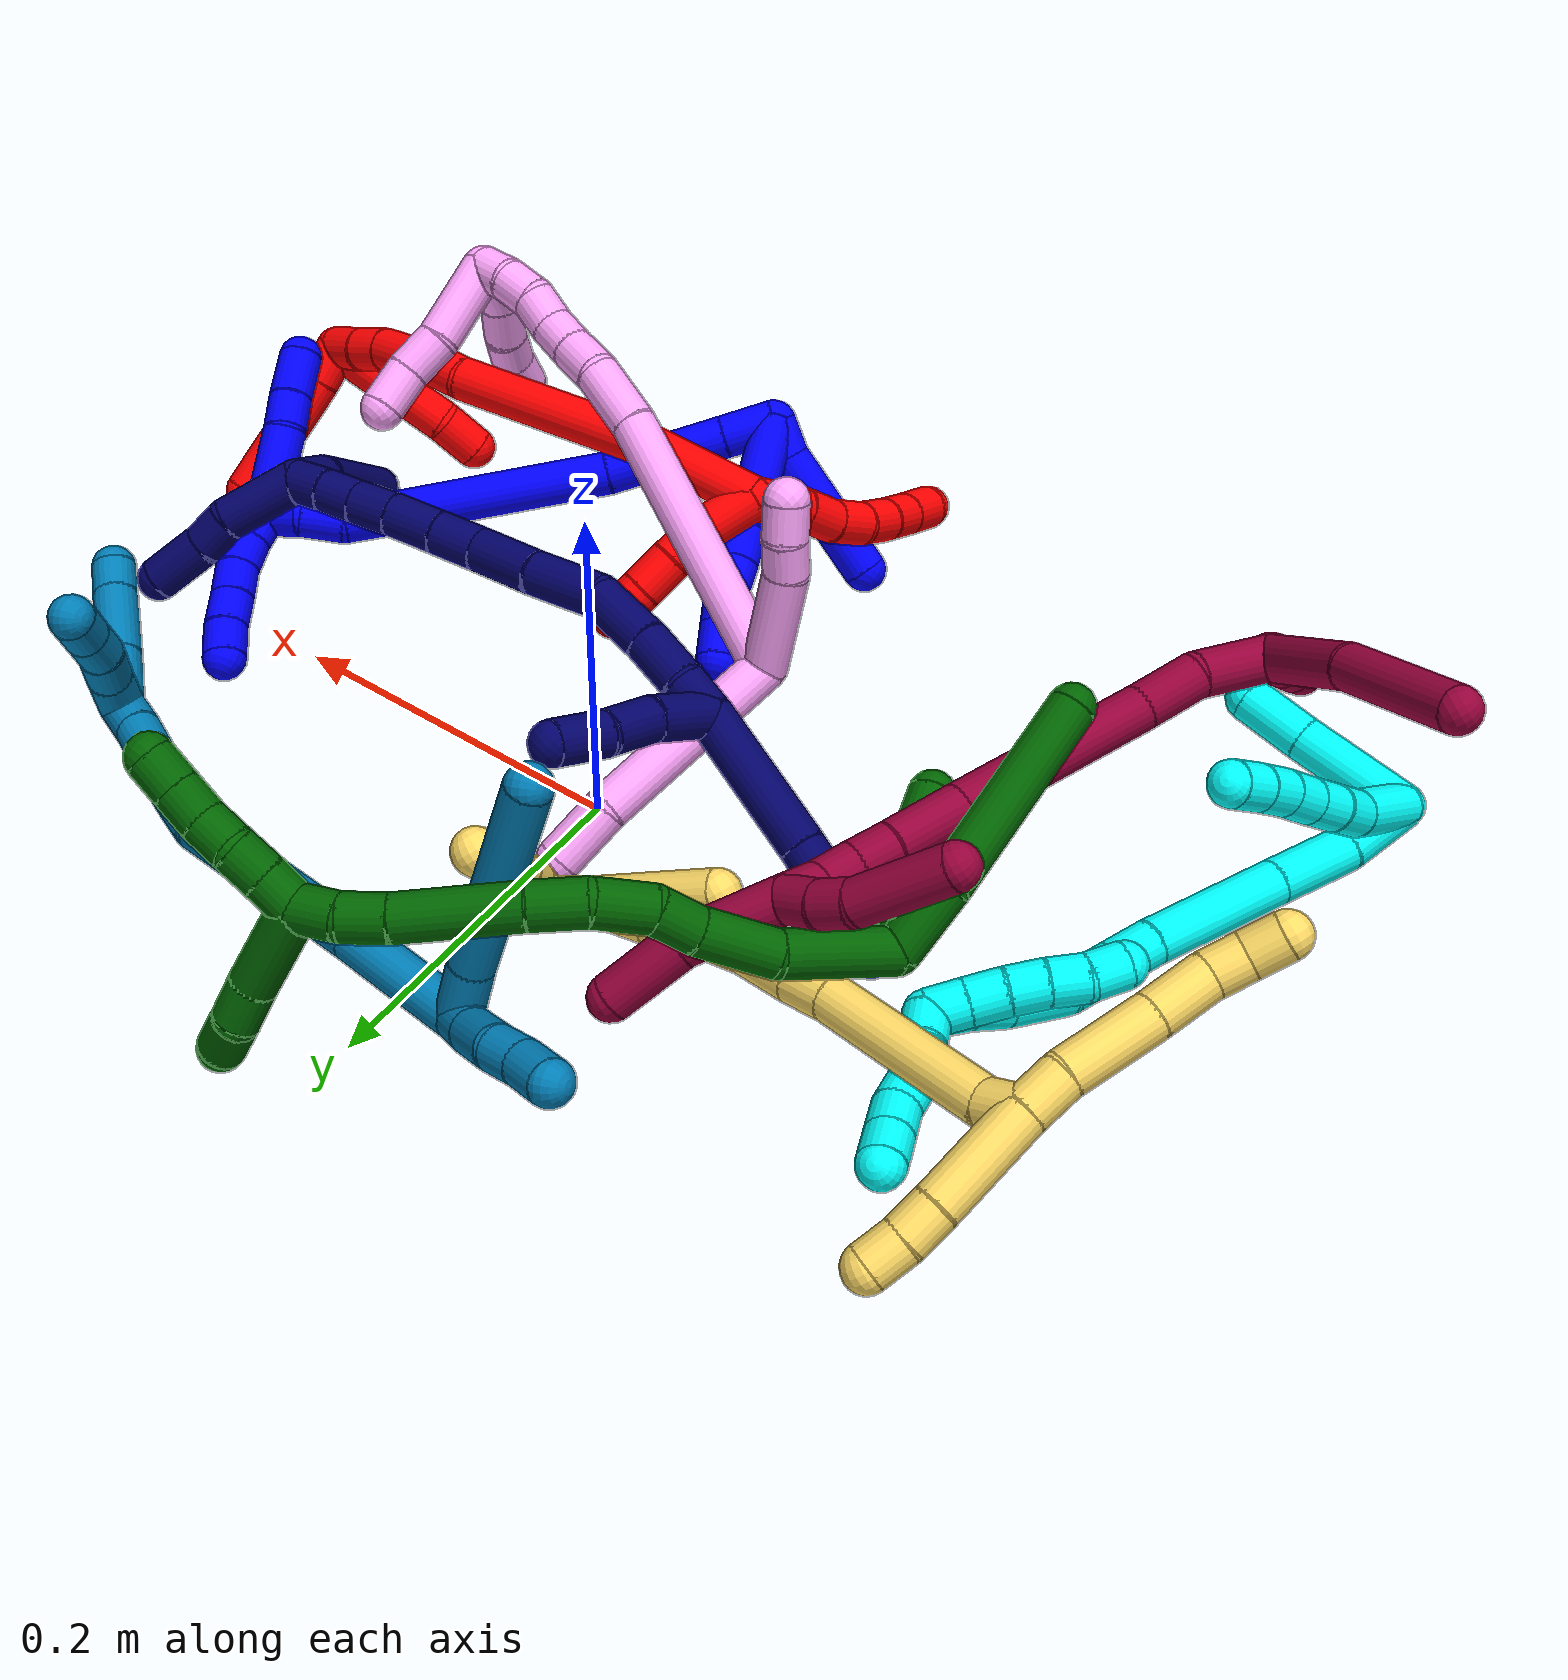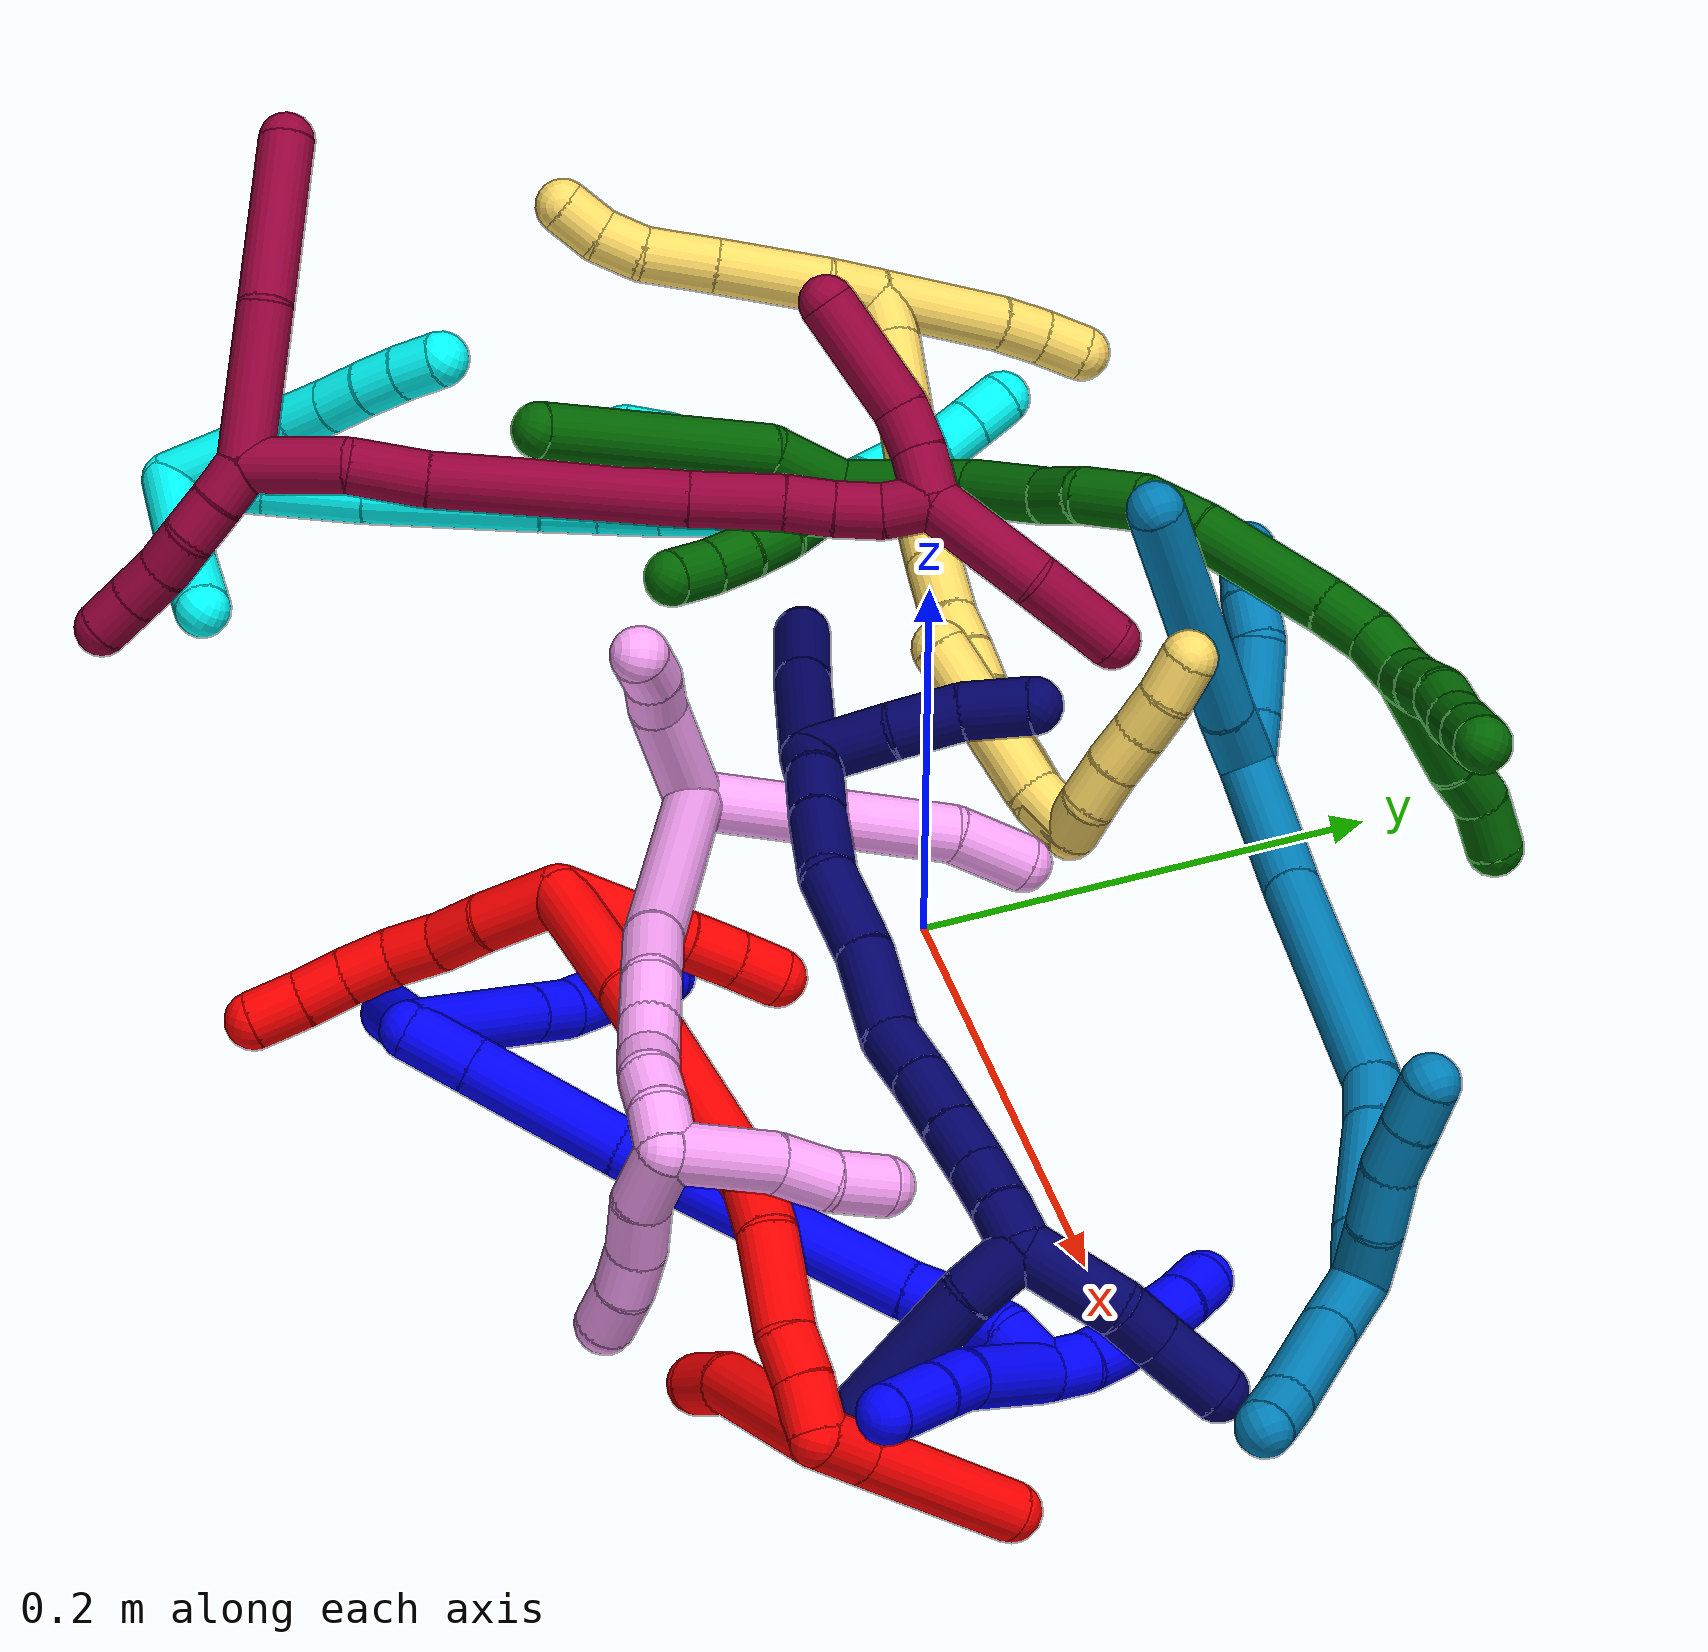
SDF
<sdf version="1.7">
 <world name="default">
  <plugin name="TubeGeneratorPlugin" filename="libtube_generator_plugin.so"/>
  <model name="photoneo_s_sensor">
   <static>1</static>
   <pose>0 0 2 1.57079 1.57079 3.14159</pose>
   <link name="link">
    <inertial><mass>0.1</mass></inertial>
    <sensor name="sensor" type="depth">
     <update_rate>30</update_rate>
     <camera>
      <horizontal_fov>1.22</horizontal_fov>
      <image><width>1920</width><height>1200</height><format>B8G8R8</format></image>
      <clip><near>0.1</near><far>4</far></clip>
      <depth_camera><output>points</output></depth_camera>
     </camera>
     <plugin name="camera_plugin" filename="libgazebo_ros_depth_camera.so">
      <baseline>0.2</baseline>
      <alwaysOn>1</alwaysOn>
      <updateRate>0.0</updateRate>
      <cameraName>camera_ir</cameraName>
      <imageTopicName>/camera/color/image_raw</imageTopicName>
      <cameraInfoTopicName>/camera/color/camera_info</cameraInfoTopicName>
      <depthImageTopicName>/camera/depth/image_raw</depthImageTopicName>
      <depthImageCameraInfoTopicName>/camera/depth/camera_info</depthImageCameraInfoTopicName>
      <pointCloudTopicName>/camera/depth/points</pointCloudTopicName>
      <frameName>fr_optical</frameName>
      <pointCloudCutoff>0.1</pointCloudCutoff>
      <pointCloudCutoffMax>2.0</pointCloudCutoffMax>
      <distortionK1>0</distortionK1>
      <distortionK2>0</distortionK2>
      <distortionK3>0</distortionK3>
      <distortionT1>0</distortionT1>
      <distortionT2>0</distortionT2>
      <CxPrime>0</CxPrime>
      <Cx>0</Cx>
      <Cy>0</Cy>
      <focalLength>0</focalLength>
      <hackBaseline>0</hackBaseline>
     </plugin>
    </sensor>
   </link>
  </model>
  <gravity>0 0 -9.8</gravity>
  <magnetic_field>6e-06 2.3e-05 -4.2e-05</magnetic_field>
  <atmosphere type="adiabatic"/>
  <physics name="default_physics" default="0" type="ode">
   <max_step_size>0.003</max_step_size>
   <real_time_factor>1</real_time_factor>
   <real_time_update_rate>1000</real_time_update_rate>
   <max_contacts>10000</max_contacts>
   <ode>
    <solver>
     <type>quick</type>
     <iters>100</iters>
     <sor>1.3</sor>
     <use_dynamic_moi_rescaling>0</use_dynamic_moi_rescaling>
    </solver>
    <constraints>
     <contact_max_correcting_vel>0</contact_max_correcting_vel>
     <contact_surface_layer>0.001</contact_surface_layer>
     <cfm>0</cfm>
     <erp>0.2</erp>
    </constraints>
   </ode>
  </physics>
  <scene><ambient>0.4 0.4 0.4 1</ambient><background>0.7 0.7 0.7 1</background><shadows>0</shadows></scene>
  <audio><device>default</device></audio>
  <spherical_coordinates>
   <surface_model>EARTH_WGS84</surface_model>
   <latitude_deg>0</latitude_deg>
   <longitude_deg>0</longitude_deg>
   <elevation>0</elevation>
   <heading_deg>0</heading_deg>
  </spherical_coordinates>
  <model name="bin">
   <static>1</static>
   <link name="bottom">
    <collision name="collision-bottom">
     <pose>0 0 -0.01 0 -0 0</pose>
     <geometry><box><size>0.8 0.6 0.02</size></box></geometry>
     <surface>
      <friction><ode><mu>100</mu><mu2>100</mu2></ode></friction>
      <contact><collide_bitmask>65535</collide_bitmask></contact>
     </surface>
    </collision>
   </link>
   <link name="west_wall">
    <collision name="collision-west_wall">
     <pose>-0.41 0 0.1 0 -0 0</pose>
     <geometry><box><size>0.02 0.6 0.2</size></box></geometry>
     <surface>
      <friction><ode><mu>100</mu><mu2>100</mu2></ode></friction>
      <contact><collide_bitmask>65535</collide_bitmask></contact>
     </surface>
    </collision>
   </link>
   <link name="east_wall">
    <collision name="collision-east_wall">
     <pose>0.41 0 0.1 0 -0 0</pose>
     <geometry><box><size>0.02 0.6 0.2</size></box></geometry>
     <surface>
      <friction><ode><mu>100</mu><mu2>100</mu2></ode></friction>
      <contact><collide_bitmask>65535</collide_bitmask></contact>
     </surface>
    </collision>
   </link>
   <link name="south_wall">
    <collision name="collision-south_wall">
     <pose>0 -0.31 0.1 0 -0 0</pose>
     <geometry><box><size>0.8 0.02 0.2</size></box></geometry>
     <surface>
      <friction><ode><mu>100</mu><mu2>100</mu2></ode></friction>
      <contact><collide_bitmask>65535</collide_bitmask></contact>
     </surface>
    </collision>
   </link>
   <link name="north_wall">
    <collision name="collision-north_wall">
     <pose>0 0.31 0.1 0 -0 0</pose>
     <geometry><box><size>0.8 0.02 0.2</size></box></geometry>
     <surface>
      <friction><ode><mu>100</mu><mu2>100</mu2></ode></friction>
      <contact><collide_bitmask>65535</collide_bitmask></contact>
     </surface>
    </collision>
   </link>
  </model>
  <model name="1">
   <static>0</static>
   <link name="1">
    <collision name="collision-cylinder-e_1_2_8">
     <pose>0.000649 -0.002811 -0.033808 3.05864 0.019136 0.453207</pose>
     <geometry><cylinder><radius>0.0125</radius><length>0.067862</length></cylinder></geometry>
     <surface>
      <friction><ode><mu>1.16</mu><mu2>1.16</mu2><slip1>0</slip1><slip2>0</slip2></ode></friction>
      <contact><ode><kp>1e+06</kp><kd>1</kd><max_vel>0</max_vel><min_depth>0.001</min_depth></ode></contact>
     </surface>
    </collision>
    <visual name="visual-cylinder-e_1_2_8">
     <pose>0.000649 -0.002811 -0.033808 3.05864 0.019136 0.453207</pose>
     <geometry><cylinder><radius>0.0125</radius><length>0.067862</length></cylinder></geometry>
     <material><ambient>0 0 1 1</ambient></material>
    </visual>
    <collision name="collision-cylinder-e_2_8_9">
     <pose>0.001548 -0.006484 -0.078203 3.06033 0.023474 0.562128</pose>
     <geometry><cylinder><radius>0.0125</radius><length>0.02125</length></cylinder></geometry>
     <surface>
      <friction><ode><mu>1.16</mu><mu2>1.16</mu2><slip1>0</slip1><slip2>0</slip2></ode></friction>
      <contact><ode><kp>1e+06</kp><kd>1</kd><max_vel>0</max_vel><min_depth>0.001</min_depth></ode></contact>
     </surface>
    </collision>
    <visual name="visual-cylinder-e_2_8_9">
     <pose>0.001548 -0.006484 -0.078203 3.06033 0.023474 0.562128</pose>
     <geometry><cylinder><radius>0.0125</radius><length>0.02125</length></cylinder></geometry>
     <material><ambient>0 0 1 1</ambient></material>
    </visual>
    <collision name="collision-cylinder-e_3_9_10">
     <pose>0.001265 -0.005507 -0.098957 -2.96261 -0.051472 0.558732</pose>
     <geometry><cylinder><radius>0.0125</radius><length>0.020691</length></cylinder></geometry>
     <surface>
      <friction><ode><mu>1.16</mu><mu2>1.16</mu2><slip1>0</slip1><slip2>0</slip2></ode></friction>
      <contact><ode><kp>1e+06</kp><kd>1</kd><max_vel>0</max_vel><min_depth>0.001</min_depth></ode></contact>
     </surface>
    </collision>
    <visual name="visual-cylinder-e_3_9_10">
     <pose>0.001265 -0.005507 -0.098957 -2.96261 -0.051472 0.558732</pose>
     <geometry><cylinder><radius>0.0125</radius><length>0.020691</length></cylinder></geometry>
     <material><ambient>0 0 1 1</ambient></material>
    </visual>
    <collision name="collision-cylinder-e_4_10_11">
     <pose>-0.000327 -0.004659 -0.119024 3.04182 -0.106131 -1.63268</pose>
     <geometry><cylinder><radius>0.0125</radius><length>0.020013</length></cylinder></geometry>
     <surface>
      <friction><ode><mu>1.16</mu><mu2>1.16</mu2><slip1>0</slip1><slip2>0</slip2></ode></friction>
      <contact><ode><kp>1e+06</kp><kd>1</kd><max_vel>0</max_vel><min_depth>0.001</min_depth></ode></contact>
     </surface>
    </collision>
    <visual name="visual-cylinder-e_4_10_11">
     <pose>-0.000327 -0.004659 -0.119024 3.04182 -0.106131 -1.63268</pose>
     <geometry><cylinder><radius>0.0125</radius><length>0.020013</length></cylinder></geometry>
     <material><ambient>0 0 1 1</ambient></material>
    </visual>
    <collision name="collision-cylinder-e_5_11_6">
     <pose>-0.002607 -0.006505 -0.138907 3.05607 -0.12116 -1.9129</pose>
     <geometry><cylinder><radius>0.0125</radius><length>0.020184</length></cylinder></geometry>
     <surface>
      <friction><ode><mu>1.16</mu><mu2>1.16</mu2><slip1>0</slip1><slip2>0</slip2></ode></friction>
      <contact><ode><kp>1e+06</kp><kd>1</kd><max_vel>0</max_vel><min_depth>0.001</min_depth></ode></contact>
     </surface>
    </collision>
    <visual name="visual-cylinder-e_5_11_6">
     <pose>-0.002607 -0.006505 -0.138907 3.05607 -0.12116 -1.9129</pose>
     <geometry><cylinder><radius>0.0125</radius><length>0.020184</length></cylinder></geometry>
     <material><ambient>0 0 1 1</ambient></material>
    </visual>
    <collision name="collision-cylinder-e_1_2_12">
     <pose>-0.003469 -0.006978 -0.007552 2.39566 -0.325369 -0.794378</pose>
     <geometry><cylinder><radius>0.0125</radius><length>0.021703</length></cylinder></geometry>
     <surface>
      <friction><ode><mu>1.16</mu><mu2>1.16</mu2><slip1>0</slip1><slip2>0</slip2></ode></friction>
      <contact><ode><kp>1e+06</kp><kd>1</kd><max_vel>0</max_vel><min_depth>0.001</min_depth></ode></contact>
     </surface>
    </collision>
    <visual name="visual-cylinder-e_1_2_12">
     <pose>-0.003469 -0.006978 -0.007552 2.39566 -0.325369 -0.794378</pose>
     <geometry><cylinder><radius>0.0125</radius><length>0.021703</length></cylinder></geometry>
     <material><ambient>0 0 1 1</ambient></material>
    </visual>
    <collision name="collision-cylinder-e_2_12_5">
     <pose>-0.026566 -0.04021 -0.036505 2.25472 -0.525204 -1.02999</pose>
     <geometry><cylinder><radius>0.0125</radius><length>0.078297</length></cylinder></geometry>
     <surface>
      <friction><ode><mu>1.16</mu><mu2>1.16</mu2><slip1>0</slip1><slip2>0</slip2></ode></friction>
      <contact><ode><kp>1e+06</kp><kd>1</kd><max_vel>0</max_vel><min_depth>0.001</min_depth></ode></contact>
     </surface>
    </collision>
    <visual name="visual-cylinder-e_2_12_5">
     <pose>-0.026566 -0.04021 -0.036505 2.25472 -0.525204 -1.02999</pose>
     <geometry><cylinder><radius>0.0125</radius><length>0.078297</length></cylinder></geometry>
     <material><ambient>0 0 1 1</ambient></material>
    </visual>
    <collision name="collision-cylinder-e_1_2_13">
     <pose>0.012671 0.002955 -0.007216 -2.75291 1.01917 -2.46428</pose>
     <geometry><cylinder><radius>0.0125</radius><length>0.029756</length></cylinder></geometry>
     <surface>
      <friction><ode><mu>1.16</mu><mu2>1.16</mu2><slip1>0</slip1><slip2>0</slip2></ode></friction>
      <contact><ode><kp>1e+06</kp><kd>1</kd><max_vel>0</max_vel><min_depth>0.001</min_depth></ode></contact>
     </surface>
    </collision>
    <visual name="visual-cylinder-e_1_2_13">
     <pose>0.012671 0.002955 -0.007216 -2.75291 1.01917 -2.46428</pose>
     <geometry><cylinder><radius>0.0125</radius><length>0.029756</length></cylinder></geometry>
     <material><ambient>0 0 1 1</ambient></material>
    </visual>
    <collision name="collision-cylinder-e_2_13_14">
     <pose>0.055026 0.012934 -0.031192 -2.74475 1.02144 -2.45252</pose>
     <geometry><cylinder><radius>0.0125</radius><length>0.069608</length></cylinder></geometry>
     <surface>
      <friction><ode><mu>1.16</mu><mu2>1.16</mu2><slip1>0</slip1><slip2>0</slip2></ode></friction>
      <contact><ode><kp>1e+06</kp><kd>1</kd><max_vel>0</max_vel><min_depth>0.001</min_depth></ode></contact>
     </surface>
    </collision>
    <visual name="visual-cylinder-e_2_13_14">
     <pose>0.055026 0.012934 -0.031192 -2.74475 1.02144 -2.45252</pose>
     <geometry><cylinder><radius>0.0125</radius><length>0.069608</length></cylinder></geometry>
     <material><ambient>0 0 1 1</ambient></material>
    </visual>
    <collision name="collision-cylinder-e_3_14_15">
     <pose>0.14105 0.040368 -0.075384 -2.50191 1.02533 -2.07784</pose>
     <geometry><cylinder><radius>0.0125</radius><length>0.131809</length></cylinder></geometry>
     <surface>
      <friction><ode><mu>1.16</mu><mu2>1.16</mu2><slip1>0</slip1><slip2>0</slip2></ode></friction>
      <contact><ode><kp>1e+06</kp><kd>1</kd><max_vel>0</max_vel><min_depth>0.001</min_depth></ode></contact>
     </surface>
    </collision>
    <visual name="visual-cylinder-e_3_14_15">
     <pose>0.14105 0.040368 -0.075384 -2.50191 1.02533 -2.07784</pose>
     <geometry><cylinder><radius>0.0125</radius><length>0.131809</length></cylinder></geometry>
     <material><ambient>0 0 1 1</ambient></material>
    </visual>
    <collision name="collision-cylinder-e_4_15_16">
     <pose>0.20594 0.065015 -0.107639 -2.42097 0.926696 -1.84938</pose>
     <geometry><cylinder><radius>0.0125</radius><length>0.021381</length></cylinder></geometry>
     <surface>
      <friction><ode><mu>1.16</mu><mu2>1.16</mu2><slip1>0</slip1><slip2>0</slip2></ode></friction>
      <contact><ode><kp>1e+06</kp><kd>1</kd><max_vel>0</max_vel><min_depth>0.001</min_depth></ode></contact>
     </surface>
    </collision>
    <visual name="visual-cylinder-e_4_15_16">
     <pose>0.20594 0.065015 -0.107639 -2.42097 0.926696 -1.84938</pose>
     <geometry><cylinder><radius>0.0125</radius><length>0.021381</length></cylinder></geometry>
     <material><ambient>0 0 1 1</ambient></material>
    </visual>
    <collision name="collision-cylinder-e_5_16_17">
     <pose>0.225106 0.075274 -0.114201 -1.85177 1.03741 -1.29834</pose>
     <geometry><cylinder><radius>0.0125</radius><length>0.024662</length></cylinder></geometry>
     <surface>
      <friction><ode><mu>1.16</mu><mu2>1.16</mu2><slip1>0</slip1><slip2>0</slip2></ode></friction>
      <contact><ode><kp>1e+06</kp><kd>1</kd><max_vel>0</max_vel><min_depth>0.001</min_depth></ode></contact>
     </surface>
    </collision>
    <visual name="visual-cylinder-e_5_16_17">
     <pose>0.225106 0.075274 -0.114201 -1.85177 1.03741 -1.29834</pose>
     <geometry><cylinder><radius>0.0125</radius><length>0.024662</length></cylinder></geometry>
     <material><ambient>0 0 1 1</ambient></material>
    </visual>
    <collision name="collision-cylinder-e_6_17_1">
     <pose>0.246887 0.083232 -0.117135 -2.12437 1.36986 -1.94376</pose>
     <geometry><cylinder><radius>0.0125</radius><length>0.022783</length></cylinder></geometry>
     <surface>
      <friction><ode><mu>1.16</mu><mu2>1.16</mu2><slip1>0</slip1><slip2>0</slip2></ode></friction>
      <contact><ode><kp>1e+06</kp><kd>1</kd><max_vel>0</max_vel><min_depth>0.001</min_depth></ode></contact>
     </surface>
    </collision>
    <visual name="visual-cylinder-e_6_17_1">
     <pose>0.246887 0.083232 -0.117135 -2.12437 1.36986 -1.94376</pose>
     <geometry><cylinder><radius>0.0125</radius><length>0.022783</length></cylinder></geometry>
     <material><ambient>0 0 1 1</ambient></material>
    </visual>
    <collision name="collision-cylinder-e_1_1_18">
     <pose>0.257374 0.090399 -0.093292 -0.206034 -0.026392 0.002729</pose>
     <geometry><cylinder><radius>0.0125</radius><length>0.051178</length></cylinder></geometry>
     <surface>
      <friction><ode><mu>1.16</mu><mu2>1.16</mu2><slip1>0</slip1><slip2>0</slip2></ode></friction>
      <contact><ode><kp>1e+06</kp><kd>1</kd><max_vel>0</max_vel><min_depth>0.001</min_depth></ode></contact>
     </surface>
    </collision>
    <visual name="visual-cylinder-e_1_1_18">
     <pose>0.257374 0.090399 -0.093292 -0.206034 -0.026392 0.002729</pose>
     <geometry><cylinder><radius>0.0125</radius><length>0.051178</length></cylinder></geometry>
     <material><ambient>0 0 1 1</ambient></material>
    </visual>
    <collision name="collision-cylinder-e_2_18_19">
     <pose>0.258116 0.096427 -0.058165 -0.078634 0.139172 -0.005484</pose>
     <geometry><cylinder><radius>0.0125</radius><length>0.020436</length></cylinder></geometry>
     <surface>
      <friction><ode><mu>1.16</mu><mu2>1.16</mu2><slip1>0</slip1><slip2>0</slip2></ode></friction>
      <contact><ode><kp>1e+06</kp><kd>1</kd><max_vel>0</max_vel><min_depth>0.001</min_depth></ode></contact>
     </surface>
    </collision>
    <visual name="visual-cylinder-e_2_18_19">
     <pose>0.258116 0.096427 -0.058165 -0.078634 0.139172 -0.005484</pose>
     <geometry><cylinder><radius>0.0125</radius><length>0.020436</length></cylinder></geometry>
     <material><ambient>0 0 1 1</ambient></material>
    </visual>
    <collision name="collision-cylinder-e_3_19_4">
     <pose>0.261277 0.097273 -0.033991 -0.003594 0.123156 -0.000222</pose>
     <geometry><cylinder><radius>0.0125</radius><length>0.028387</length></cylinder></geometry>
     <surface>
      <friction><ode><mu>1.16</mu><mu2>1.16</mu2><slip1>0</slip1><slip2>0</slip2></ode></friction>
      <contact><ode><kp>1e+06</kp><kd>1</kd><max_vel>0</max_vel><min_depth>0.001</min_depth></ode></contact>
     </surface>
    </collision>
    <visual name="visual-cylinder-e_3_19_4">
     <pose>0.261277 0.097273 -0.033991 -0.003594 0.123156 -0.000222</pose>
     <geometry><cylinder><radius>0.0125</radius><length>0.028387</length></cylinder></geometry>
     <material><ambient>0 0 1 1</ambient></material>
    </visual>
    <collision name="collision-cylinder-e_1_1_20">
     <pose>0.259022 0.08667 -0.128169 -2.98995 0.097402 -1.14085</pose>
     <geometry><cylinder><radius>0.0125</radius><length>0.02</length></cylinder></geometry>
     <surface>
      <friction><ode><mu>1.16</mu><mu2>1.16</mu2><slip1>0</slip1><slip2>0</slip2></ode></friction>
      <contact><ode><kp>1e+06</kp><kd>1</kd><max_vel>0</max_vel><min_depth>0.001</min_depth></ode></contact>
     </surface>
    </collision>
    <visual name="visual-cylinder-e_1_1_20">
     <pose>0.259022 0.08667 -0.128169 -2.98995 0.097402 -1.14085</pose>
     <geometry><cylinder><radius>0.0125</radius><length>0.02</length></cylinder></geometry>
     <material><ambient>0 0 1 1</ambient></material>
    </visual>
    <collision name="collision-cylinder-e_2_20_21">
     <pose>0.259055 0.089874 -0.147817 -2.96992 -0.094007 1.00053</pose>
     <geometry><cylinder><radius>0.0125</radius><length>0.02</length></cylinder></geometry>
     <surface>
      <friction><ode><mu>1.16</mu><mu2>1.16</mu2><slip1>0</slip1><slip2>0</slip2></ode></friction>
      <contact><ode><kp>1e+06</kp><kd>1</kd><max_vel>0</max_vel><min_depth>0.001</min_depth></ode></contact>
     </surface>
    </collision>
    <visual name="visual-cylinder-e_2_20_21">
     <pose>0.259055 0.089874 -0.147817 -2.96992 -0.094007 1.00053</pose>
     <geometry><cylinder><radius>0.0125</radius><length>0.02</length></cylinder></geometry>
     <material><ambient>0 0 1 1</ambient></material>
    </visual>
    <collision name="collision-cylinder-e_3_21_22">
     <pose>0.255561 0.092281 -0.167269 -3.06852 -0.258378 2.59308</pose>
     <geometry><cylinder><radius>0.0125</radius><length>0.02</length></cylinder></geometry>
     <surface>
      <friction><ode><mu>1.16</mu><mu2>1.16</mu2><slip1>0</slip1><slip2>0</slip2></ode></friction>
      <contact><ode><kp>1e+06</kp><kd>1</kd><max_vel>0</max_vel><min_depth>0.001</min_depth></ode></contact>
     </surface>
    </collision>
    <visual name="visual-cylinder-e_3_21_22">
     <pose>0.255561 0.092281 -0.167269 -3.06852 -0.258378 2.59308</pose>
     <geometry><cylinder><radius>0.0125</radius><length>0.02</length></cylinder></geometry>
     <material><ambient>0 0 1 1</ambient></material>
    </visual>
    <collision name="collision-cylinder-e_4_22_23">
     <pose>0.250742 0.093916 -0.186607 -3.046 -0.228379 2.35133</pose>
     <geometry><cylinder><radius>0.0125</radius><length>0.02</length></cylinder></geometry>
     <surface>
      <friction><ode><mu>1.16</mu><mu2>1.16</mu2><slip1>0</slip1><slip2>0</slip2></ode></friction>
      <contact><ode><kp>1e+06</kp><kd>1</kd><max_vel>0</max_vel><min_depth>0.001</min_depth></ode></contact>
     </surface>
    </collision>
    <visual name="visual-cylinder-e_4_22_23">
     <pose>0.250742 0.093916 -0.186607 -3.046 -0.228379 2.35133</pose>
     <geometry><cylinder><radius>0.0125</radius><length>0.02</length></cylinder></geometry>
     <material><ambient>0 0 1 1</ambient></material>
    </visual>
    <collision name="collision-cylinder-e_5_23_3">
     <pose>0.245173 0.09483 -0.205741 3.13988 -0.336857 -3.13151</pose>
     <geometry><cylinder><radius>0.0125</radius><length>0.02</length></cylinder></geometry>
     <surface>
      <friction><ode><mu>1.16</mu><mu2>1.16</mu2><slip1>0</slip1><slip2>0</slip2></ode></friction>
      <contact><ode><kp>1e+06</kp><kd>1</kd><max_vel>0</max_vel><min_depth>0.001</min_depth></ode></contact>
     </surface>
    </collision>
    <visual name="visual-cylinder-e_5_23_3">
     <pose>0.245173 0.09483 -0.205741 3.13988 -0.336857 -3.13151</pose>
     <geometry><cylinder><radius>0.0125</radius><length>0.02</length></cylinder></geometry>
     <material><ambient>0 0 1 1</ambient></material>
    </visual>
    <collision name="collision-sphere-3">
     <pose>0.241868 0.094814 -0.215179 0 -0 0</pose>
     <geometry><sphere><radius>0.0125</radius></sphere></geometry>
     <surface>
      <friction><ode><mu>1.16</mu><mu2>1.16</mu2><slip1>0</slip1><slip2>0</slip2></ode></friction>
      <contact><ode><kp>1e+06</kp><kd>1</kd><max_vel>0</max_vel><min_depth>0.001</min_depth></ode></contact>
     </surface>
    </collision>
    <visual name="visual-sphere-3">
     <pose>0.241868 0.094814 -0.215179 0 -0 0</pose>
     <geometry><sphere><radius>0.0125</radius></sphere></geometry>
     <material><ambient>0 0 1 1</ambient></material>
    </visual>
    <collision name="collision-sphere-23">
     <pose>0.248478 0.094846 -0.196303 0 -0 0</pose>
     <geometry><sphere><radius>0.0125</radius></sphere></geometry>
     <surface>
      <friction><ode><mu>1.16</mu><mu2>1.16</mu2><slip1>0</slip1><slip2>0</slip2></ode></friction>
      <contact><ode><kp>1e+06</kp><kd>1</kd><max_vel>0</max_vel><min_depth>0.001</min_depth></ode></contact>
     </surface>
    </collision>
    <visual name="visual-sphere-23">
     <pose>0.248478 0.094846 -0.196303 0 -0 0</pose>
     <geometry><sphere><radius>0.0125</radius></sphere></geometry>
     <material><ambient>0 0 1 1</ambient></material>
    </visual>
    <collision name="collision-sphere-22">
     <pose>0.253006 0.092987 -0.176911 0 -0 0</pose>
     <geometry><sphere><radius>0.0125</radius></sphere></geometry>
     <surface>
      <friction><ode><mu>1.16</mu><mu2>1.16</mu2><slip1>0</slip1><slip2>0</slip2></ode></friction>
      <contact><ode><kp>1e+06</kp><kd>1</kd><max_vel>0</max_vel><min_depth>0.001</min_depth></ode></contact>
     </surface>
    </collision>
    <visual name="visual-sphere-22">
     <pose>0.253006 0.092987 -0.176911 0 -0 0</pose>
     <geometry><sphere><radius>0.0125</radius></sphere></geometry>
     <material><ambient>0 0 1 1</ambient></material>
    </visual>
    <collision name="collision-sphere-21">
     <pose>0.258117 0.091575 -0.157626 0 -0 0</pose>
     <geometry><sphere><radius>0.0125</radius></sphere></geometry>
     <surface>
      <friction><ode><mu>1.16</mu><mu2>1.16</mu2><slip1>0</slip1><slip2>0</slip2></ode></friction>
      <contact><ode><kp>1e+06</kp><kd>1</kd><max_vel>0</max_vel><min_depth>0.001</min_depth></ode></contact>
     </surface>
    </collision>
    <visual name="visual-sphere-21">
     <pose>0.258117 0.091575 -0.157626 0 -0 0</pose>
     <geometry><sphere><radius>0.0125</radius></sphere></geometry>
     <material><ambient>0 0 1 1</ambient></material>
    </visual>
    <collision name="collision-sphere-20">
     <pose>0.259994 0.088173 -0.138007 0 -0 0</pose>
     <geometry><sphere><radius>0.0125</radius></sphere></geometry>
     <surface>
      <friction><ode><mu>1.16</mu><mu2>1.16</mu2><slip1>0</slip1><slip2>0</slip2></ode></friction>
      <contact><ode><kp>1e+06</kp><kd>1</kd><max_vel>0</max_vel><min_depth>0.001</min_depth></ode></contact>
     </surface>
    </collision>
    <visual name="visual-sphere-20">
     <pose>0.259994 0.088173 -0.138007 0 -0 0</pose>
     <geometry><sphere><radius>0.0125</radius></sphere></geometry>
     <material><ambient>0 0 1 1</ambient></material>
    </visual>
    <collision name="collision-sphere-4">
     <pose>0.263021 0.097324 -0.019906 0 -0 0</pose>
     <geometry><sphere><radius>0.0125</radius></sphere></geometry>
     <surface>
      <friction><ode><mu>1.16</mu><mu2>1.16</mu2><slip1>0</slip1><slip2>0</slip2></ode></friction>
      <contact><ode><kp>1e+06</kp><kd>1</kd><max_vel>0</max_vel><min_depth>0.001</min_depth></ode></contact>
     </surface>
    </collision>
    <visual name="visual-sphere-4">
     <pose>0.263021 0.097324 -0.019906 0 -0 0</pose>
     <geometry><sphere><radius>0.0125</radius></sphere></geometry>
     <material><ambient>0 0 1 1</ambient></material>
    </visual>
    <collision name="collision-sphere-6">
     <pose>-0.003827 -0.007361 -0.148888 0 -0 0</pose>
     <geometry><sphere><radius>0.0125</radius></sphere></geometry>
     <surface>
      <friction><ode><mu>1.16</mu><mu2>1.16</mu2><slip1>0</slip1><slip2>0</slip2></ode></friction>
      <contact><ode><kp>1e+06</kp><kd>1</kd><max_vel>0</max_vel><min_depth>0.001</min_depth></ode></contact>
     </surface>
    </collision>
    <visual name="visual-sphere-6">
     <pose>-0.003827 -0.007361 -0.148888 0 -0 0</pose>
     <geometry><sphere><radius>0.0125</radius></sphere></geometry>
     <material><ambient>0 0 1 1</ambient></material>
    </visual>
    <collision name="collision-sphere-11">
     <pose>-0.001387 -0.00565 -0.128925 0 -0 0</pose>
     <geometry><sphere><radius>0.0125</radius></sphere></geometry>
     <surface>
      <friction><ode><mu>1.16</mu><mu2>1.16</mu2><slip1>0</slip1><slip2>0</slip2></ode></friction>
      <contact><ode><kp>1e+06</kp><kd>1</kd><max_vel>0</max_vel><min_depth>0.001</min_depth></ode></contact>
     </surface>
    </collision>
    <visual name="visual-sphere-11">
     <pose>-0.001387 -0.00565 -0.128925 0 -0 0</pose>
     <geometry><sphere><radius>0.0125</radius></sphere></geometry>
     <material><ambient>0 0 1 1</ambient></material>
    </visual>
    <collision name="collision-sphere-10">
     <pose>0.000733 -0.003667 -0.109124 0 -0 0</pose>
     <geometry><sphere><radius>0.0125</radius></sphere></geometry>
     <surface>
      <friction><ode><mu>1.16</mu><mu2>1.16</mu2><slip1>0</slip1><slip2>0</slip2></ode></friction>
      <contact><ode><kp>1e+06</kp><kd>1</kd><max_vel>0</max_vel><min_depth>0.001</min_depth></ode></contact>
     </surface>
    </collision>
    <visual name="visual-sphere-10">
     <pose>0.000733 -0.003667 -0.109124 0 -0 0</pose>
     <geometry><sphere><radius>0.0125</radius></sphere></geometry>
     <material><ambient>0 0 1 1</ambient></material>
    </visual>
    <collision name="collision-sphere-9">
     <pose>0.001797 -0.007346 -0.08879 0 -0 0</pose>
     <geometry><sphere><radius>0.0125</radius></sphere></geometry>
     <surface>
      <friction><ode><mu>1.16</mu><mu2>1.16</mu2><slip1>0</slip1><slip2>0</slip2></ode></friction>
      <contact><ode><kp>1e+06</kp><kd>1</kd><max_vel>0</max_vel><min_depth>0.001</min_depth></ode></contact>
     </surface>
    </collision>
    <visual name="visual-sphere-9">
     <pose>0.001797 -0.007346 -0.08879 0 -0 0</pose>
     <geometry><sphere><radius>0.0125</radius></sphere></geometry>
     <material><ambient>0 0 1 1</ambient></material>
    </visual>
    <collision name="collision-sphere-2">
     <geometry><sphere><radius>0.0125</radius></sphere></geometry>
     <surface>
      <friction><ode><mu>1.16</mu><mu2>1.16</mu2><slip1>0</slip1><slip2>0</slip2></ode></friction>
      <contact><ode><kp>1e+06</kp><kd>1</kd><max_vel>0</max_vel><min_depth>0.001</min_depth></ode></contact>
     </surface>
    </collision>
    <visual name="visual-sphere-2">
     <geometry><sphere><radius>0.0125</radius></sphere></geometry>
     <material><ambient>0 0 1 1</ambient></material>
    </visual>
    <collision name="collision-sphere-19">
     <pose>0.259533 0.097222 -0.048077 0 -0 0</pose>
     <geometry><sphere><radius>0.0125</radius></sphere></geometry>
     <surface>
      <friction><ode><mu>1.16</mu><mu2>1.16</mu2><slip1>0</slip1><slip2>0</slip2></ode></friction>
      <contact><ode><kp>1e+06</kp><kd>1</kd><max_vel>0</max_vel><min_depth>0.001</min_depth></ode></contact>
     </surface>
    </collision>
    <visual name="visual-sphere-19">
     <pose>0.259533 0.097222 -0.048077 0 -0 0</pose>
     <geometry><sphere><radius>0.0125</radius></sphere></geometry>
     <material><ambient>0 0 1 1</ambient></material>
    </visual>
    <collision name="collision-sphere-8">
     <pose>0.001298 -0.005622 -0.067616 0 -0 0</pose>
     <geometry><sphere><radius>0.0125</radius></sphere></geometry>
     <surface>
      <friction><ode><mu>1.16</mu><mu2>1.16</mu2><slip1>0</slip1><slip2>0</slip2></ode></friction>
      <contact><ode><kp>1e+06</kp><kd>1</kd><max_vel>0</max_vel><min_depth>0.001</min_depth></ode></contact>
     </surface>
    </collision>
    <visual name="visual-sphere-8">
     <pose>0.001298 -0.005622 -0.067616 0 -0 0</pose>
     <geometry><sphere><radius>0.0125</radius></sphere></geometry>
     <material><ambient>0 0 1 1</ambient></material>
    </visual>
    <collision name="collision-sphere-12">
     <pose>-0.006937 -0.013956 -0.015103 0 -0 0</pose>
     <geometry><sphere><radius>0.0125</radius></sphere></geometry>
     <surface>
      <friction><ode><mu>1.16</mu><mu2>1.16</mu2><slip1>0</slip1><slip2>0</slip2></ode></friction>
      <contact><ode><kp>1e+06</kp><kd>1</kd><max_vel>0</max_vel><min_depth>0.001</min_depth></ode></contact>
     </surface>
    </collision>
    <visual name="visual-sphere-12">
     <pose>-0.006937 -0.013956 -0.015103 0 -0 0</pose>
     <geometry><sphere><radius>0.0125</radius></sphere></geometry>
     <material><ambient>0 0 1 1</ambient></material>
    </visual>
    <collision name="collision-sphere-5">
     <pose>-0.046195 -0.066465 -0.057907 0 -0 0</pose>
     <geometry><sphere><radius>0.0125</radius></sphere></geometry>
     <surface>
      <friction><ode><mu>1.16</mu><mu2>1.16</mu2><slip1>0</slip1><slip2>0</slip2></ode></friction>
      <contact><ode><kp>1e+06</kp><kd>1</kd><max_vel>0</max_vel><min_depth>0.001</min_depth></ode></contact>
     </surface>
    </collision>
    <visual name="visual-sphere-5">
     <pose>-0.046195 -0.066465 -0.057907 0 -0 0</pose>
     <geometry><sphere><radius>0.0125</radius></sphere></geometry>
     <material><ambient>0 0 1 1</ambient></material>
    </visual>
    <collision name="collision-sphere-13">
     <pose>0.025343 0.00591 -0.014431 0 -0 0</pose>
     <geometry><sphere><radius>0.0125</radius></sphere></geometry>
     <surface>
      <friction><ode><mu>1.16</mu><mu2>1.16</mu2><slip1>0</slip1><slip2>0</slip2></ode></friction>
      <contact><ode><kp>1e+06</kp><kd>1</kd><max_vel>0</max_vel><min_depth>0.001</min_depth></ode></contact>
     </surface>
    </collision>
    <visual name="visual-sphere-13">
     <pose>0.025343 0.00591 -0.014431 0 -0 0</pose>
     <geometry><sphere><radius>0.0125</radius></sphere></geometry>
     <material><ambient>0 0 1 1</ambient></material>
    </visual>
    <collision name="collision-sphere-14">
     <pose>0.084709 0.019958 -0.047952 0 -0 0</pose>
     <geometry><sphere><radius>0.0125</radius></sphere></geometry>
     <surface>
      <friction><ode><mu>1.16</mu><mu2>1.16</mu2><slip1>0</slip1><slip2>0</slip2></ode></friction>
      <contact><ode><kp>1e+06</kp><kd>1</kd><max_vel>0</max_vel><min_depth>0.001</min_depth></ode></contact>
     </surface>
    </collision>
    <visual name="visual-sphere-14">
     <pose>0.084709 0.019958 -0.047952 0 -0 0</pose>
     <geometry><sphere><radius>0.0125</radius></sphere></geometry>
     <material><ambient>0 0 1 1</ambient></material>
    </visual>
    <collision name="collision-sphere-15">
     <pose>0.197391 0.060779 -0.102816 0 -0 0</pose>
     <geometry><sphere><radius>0.0125</radius></sphere></geometry>
     <surface>
      <friction><ode><mu>1.16</mu><mu2>1.16</mu2><slip1>0</slip1><slip2>0</slip2></ode></friction>
      <contact><ode><kp>1e+06</kp><kd>1</kd><max_vel>0</max_vel><min_depth>0.001</min_depth></ode></contact>
     </surface>
    </collision>
    <visual name="visual-sphere-15">
     <pose>0.197391 0.060779 -0.102816 0 -0 0</pose>
     <geometry><sphere><radius>0.0125</radius></sphere></geometry>
     <material><ambient>0 0 1 1</ambient></material>
    </visual>
    <collision name="collision-sphere-16">
     <pose>0.214488 0.06925 -0.112463 0 -0 0</pose>
     <geometry><sphere><radius>0.0125</radius></sphere></geometry>
     <surface>
      <friction><ode><mu>1.16</mu><mu2>1.16</mu2><slip1>0</slip1><slip2>0</slip2></ode></friction>
      <contact><ode><kp>1e+06</kp><kd>1</kd><max_vel>0</max_vel><min_depth>0.001</min_depth></ode></contact>
     </surface>
    </collision>
    <visual name="visual-sphere-16">
     <pose>0.214488 0.06925 -0.112463 0 -0 0</pose>
     <geometry><sphere><radius>0.0125</radius></sphere></geometry>
     <material><ambient>0 0 1 1</ambient></material>
    </visual>
    <collision name="collision-sphere-17">
     <pose>0.235725 0.081298 -0.11594 0 -0 0</pose>
     <geometry><sphere><radius>0.0125</radius></sphere></geometry>
     <surface>
      <friction><ode><mu>1.16</mu><mu2>1.16</mu2><slip1>0</slip1><slip2>0</slip2></ode></friction>
      <contact><ode><kp>1e+06</kp><kd>1</kd><max_vel>0</max_vel><min_depth>0.001</min_depth></ode></contact>
     </surface>
    </collision>
    <visual name="visual-sphere-17">
     <pose>0.235725 0.081298 -0.11594 0 -0 0</pose>
     <geometry><sphere><radius>0.0125</radius></sphere></geometry>
     <material><ambient>0 0 1 1</ambient></material>
    </visual>
    <collision name="collision-sphere-1">
     <pose>0.258049 0.085166 -0.118331 0 -0 0</pose>
     <geometry><sphere><radius>0.0125</radius></sphere></geometry>
     <surface>
      <friction><ode><mu>1.16</mu><mu2>1.16</mu2><slip1>0</slip1><slip2>0</slip2></ode></friction>
      <contact><ode><kp>1e+06</kp><kd>1</kd><max_vel>0</max_vel><min_depth>0.001</min_depth></ode></contact>
     </surface>
    </collision>
    <visual name="visual-sphere-1">
     <pose>0.258049 0.085166 -0.118331 0 -0 0</pose>
     <geometry><sphere><radius>0.0125</radius></sphere></geometry>
     <material><ambient>0 0 1 1</ambient></material>
    </visual>
    <collision name="collision-sphere-18">
     <pose>0.256699 0.095633 -0.068253 0 -0 0</pose>
     <geometry><sphere><radius>0.0125</radius></sphere></geometry>
     <surface>
      <friction><ode><mu>1.16</mu><mu2>1.16</mu2><slip1>0</slip1><slip2>0</slip2></ode></friction>
      <contact><ode><kp>1e+06</kp><kd>1</kd><max_vel>0</max_vel><min_depth>0.001</min_depth></ode></contact>
     </surface>
    </collision>
    <visual name="visual-sphere-18">
     <pose>0.256699 0.095633 -0.068253 0 -0 0</pose>
     <geometry><sphere><radius>0.0125</radius></sphere></geometry>
     <material><ambient>0 0 1 1</ambient></material>
    </visual>
    <inertial>
     <pose>0.116696 0.03466 -0.07728 0 -0 0</pose>
     <mass>0.75</mass>
     <inertia>
      <ixx>-0.000107</ixx>
      <ixy>0</ixy>
      <ixz>0</ixz>
      <iyy>7.2e-05</iyy>
      <iyz>0</iyz>
      <izz>-0.000245</izz>
     </inertia>
    </inertial>
   </link>
   <pose>0.057494 -0.241997 0.078848 1.16246 0.288717 0.22449</pose>
  </model>
  <model name="2">
   <static>0</static>
   <link name="2">
    <collision name="collision-cylinder-e_1_2_8">
     <pose>0.002942 -0.010758 0.014537 0.637085 0.161246 0.053277</pose>
     <geometry><cylinder><radius>0.0125</radius><length>0.036645</length></cylinder></geometry>
     <surface>
      <friction><ode><mu>1.16</mu><mu2>1.16</mu2><slip1>0</slip1><slip2>0</slip2></ode></friction>
      <contact><ode><kp>1e+06</kp><kd>1</kd><max_vel>0</max_vel><min_depth>0.001</min_depth></ode></contact>
     </surface>
    </collision>
    <visual name="visual-cylinder-e_1_2_8">
     <pose>0.002942 -0.010758 0.014537 0.637085 0.161246 0.053277</pose>
     <geometry><cylinder><radius>0.0125</radius><length>0.036645</length></cylinder></geometry>
     <material><ambient>1 0 0 1</ambient></material>
    </visual>
    <collision name="collision-cylinder-e_2_8_9">
     <pose>0.00668 -0.029749 0.03821 0.733475 0.064681 0.024852</pose>
     <geometry><cylinder><radius>0.0125</radius><length>0.024647</length></cylinder></geometry>
     <surface>
      <friction><ode><mu>1.16</mu><mu2>1.16</mu2><slip1>0</slip1><slip2>0</slip2></ode></friction>
      <contact><ode><kp>1e+06</kp><kd>1</kd><max_vel>0</max_vel><min_depth>0.001</min_depth></ode></contact>
     </surface>
    </collision>
    <visual name="visual-cylinder-e_2_8_9">
     <pose>0.00668 -0.029749 0.03821 0.733475 0.064681 0.024852</pose>
     <geometry><cylinder><radius>0.0125</radius><length>0.024647</length></cylinder></geometry>
     <material><ambient>1 0 0 1</ambient></material>
    </visual>
    <collision name="collision-cylinder-e_3_9_10">
     <pose>0.009685 -0.043934 0.056865 0.558778 0.1942 0.055876</pose>
     <geometry><cylinder><radius>0.0125</radius><length>0.022885</length></cylinder></geometry>
     <surface>
      <friction><ode><mu>1.16</mu><mu2>1.16</mu2><slip1>0</slip1><slip2>0</slip2></ode></friction>
      <contact><ode><kp>1e+06</kp><kd>1</kd><max_vel>0</max_vel><min_depth>0.001</min_depth></ode></contact>
     </surface>
    </collision>
    <visual name="visual-cylinder-e_3_9_10">
     <pose>0.009685 -0.043934 0.056865 0.558778 0.1942 0.055876</pose>
     <geometry><cylinder><radius>0.0125</radius><length>0.022885</length></cylinder></geometry>
     <material><ambient>1 0 0 1</ambient></material>
    </visual>
    <collision name="collision-cylinder-e_4_10_11">
     <pose>0.016301 -0.055114 0.074881 0.551605 0.416051 0.119335</pose>
     <geometry><cylinder><radius>0.0125</radius><length>0.021813</length></cylinder></geometry>
     <surface>
      <friction><ode><mu>1.16</mu><mu2>1.16</mu2><slip1>0</slip1><slip2>0</slip2></ode></friction>
      <contact><ode><kp>1e+06</kp><kd>1</kd><max_vel>0</max_vel><min_depth>0.001</min_depth></ode></contact>
     </surface>
    </collision>
    <visual name="visual-cylinder-e_4_10_11">
     <pose>0.016301 -0.055114 0.074881 0.551605 0.416051 0.119335</pose>
     <geometry><cylinder><radius>0.0125</radius><length>0.021813</length></cylinder></geometry>
     <material><ambient>1 0 0 1</ambient></material>
    </visual>
    <collision name="collision-cylinder-e_5_11_12">
     <pose>0.025747 -0.065329 0.091052 0.576313 0.503224 0.152094</pose>
     <geometry><cylinder><radius>0.0125</radius><length>0.020894</length></cylinder></geometry>
     <surface>
      <friction><ode><mu>1.16</mu><mu2>1.16</mu2><slip1>0</slip1><slip2>0</slip2></ode></friction>
      <contact><ode><kp>1e+06</kp><kd>1</kd><max_vel>0</max_vel><min_depth>0.001</min_depth></ode></contact>
     </surface>
    </collision>
    <visual name="visual-cylinder-e_5_11_12">
     <pose>0.025747 -0.065329 0.091052 0.576313 0.503224 0.152094</pose>
     <geometry><cylinder><radius>0.0125</radius><length>0.020894</length></cylinder></geometry>
     <material><ambient>1 0 0 1</ambient></material>
    </visual>
    <collision name="collision-cylinder-e_6_12_6">
     <pose>0.036344 -0.075308 0.107543 0.515062 0.50183 0.134813</pose>
     <geometry><cylinder><radius>0.0125</radius><length>0.023116</length></cylinder></geometry>
     <surface>
      <friction><ode><mu>1.16</mu><mu2>1.16</mu2><slip1>0</slip1><slip2>0</slip2></ode></friction>
      <contact><ode><kp>1e+06</kp><kd>1</kd><max_vel>0</max_vel><min_depth>0.001</min_depth></ode></contact>
     </surface>
    </collision>
    <visual name="visual-cylinder-e_6_12_6">
     <pose>0.036344 -0.075308 0.107543 0.515062 0.50183 0.134813</pose>
     <geometry><cylinder><radius>0.0125</radius><length>0.023116</length></cylinder></geometry>
     <material><ambient>1 0 0 1</ambient></material>
    </visual>
    <collision name="collision-cylinder-e_1_2_13">
     <pose>-0.003698 -0.005161 -0.015906 2.82785 -0.217634 -1.20891</pose>
     <geometry><cylinder><radius>0.0125</radius><length>0.034252</length></cylinder></geometry>
     <surface>
      <friction><ode><mu>1.16</mu><mu2>1.16</mu2><slip1>0</slip1><slip2>0</slip2></ode></friction>
      <contact><ode><kp>1e+06</kp><kd>1</kd><max_vel>0</max_vel><min_depth>0.001</min_depth></ode></contact>
     </surface>
    </collision>
    <visual name="visual-cylinder-e_1_2_13">
     <pose>-0.003698 -0.005161 -0.015906 2.82785 -0.217634 -1.20891</pose>
     <geometry><cylinder><radius>0.0125</radius><length>0.034252</length></cylinder></geometry>
     <material><ambient>1 0 0 1</ambient></material>
    </visual>
    <collision name="collision-cylinder-e_2_13_14">
     <pose>-0.011637 -0.01458 -0.040966 2.7062 -0.397672 -1.47763</pose>
     <geometry><cylinder><radius>0.0125</radius><length>0.021903</length></cylinder></geometry>
     <surface>
      <friction><ode><mu>1.16</mu><mu2>1.16</mu2><slip1>0</slip1><slip2>0</slip2></ode></friction>
      <contact><ode><kp>1e+06</kp><kd>1</kd><max_vel>0</max_vel><min_depth>0.001</min_depth></ode></contact>
     </surface>
    </collision>
    <visual name="visual-cylinder-e_2_13_14">
     <pose>-0.011637 -0.01458 -0.040966 2.7062 -0.397672 -1.47763</pose>
     <geometry><cylinder><radius>0.0125</radius><length>0.021903</length></cylinder></geometry>
     <material><ambient>1 0 0 1</ambient></material>
    </visual>
    <collision name="collision-cylinder-e_3_14_15">
     <pose>-0.020065 -0.02389 -0.059542 2.64942 -0.37336 -1.28954</pose>
     <geometry><cylinder><radius>0.0125</radius><length>0.022961</length></cylinder></geometry>
     <surface>
      <friction><ode><mu>1.16</mu><mu2>1.16</mu2><slip1>0</slip1><slip2>0</slip2></ode></friction>
      <contact><ode><kp>1e+06</kp><kd>1</kd><max_vel>0</max_vel><min_depth>0.001</min_depth></ode></contact>
     </surface>
    </collision>
    <visual name="visual-cylinder-e_3_14_15">
     <pose>-0.020065 -0.02389 -0.059542 2.64942 -0.37336 -1.28954</pose>
     <geometry><cylinder><radius>0.0125</radius><length>0.022961</length></cylinder></geometry>
     <material><ambient>1 0 0 1</ambient></material>
    </visual>
    <collision name="collision-cylinder-e_4_15_5">
     <pose>-0.027811 -0.033655 -0.077574 2.64078 -0.347736 -1.2035</pose>
     <geometry><cylinder><radius>0.0125</radius><length>0.020884</length></cylinder></geometry>
     <surface>
      <friction><ode><mu>1.16</mu><mu2>1.16</mu2><slip1>0</slip1><slip2>0</slip2></ode></friction>
      <contact><ode><kp>1e+06</kp><kd>1</kd><max_vel>0</max_vel><min_depth>0.001</min_depth></ode></contact>
     </surface>
    </collision>
    <visual name="visual-cylinder-e_4_15_5">
     <pose>-0.027811 -0.033655 -0.077574 2.64078 -0.347736 -1.2035</pose>
     <geometry><cylinder><radius>0.0125</radius><length>0.020884</length></cylinder></geometry>
     <material><ambient>1 0 0 1</ambient></material>
    </visual>
    <collision name="collision-cylinder-e_1_2_16">
     <pose>0.024921 0.003089 -0.024859 -3.01795 0.782806 -2.84384</pose>
     <geometry><cylinder><radius>0.0125</radius><length>0.07067</length></cylinder></geometry>
     <surface>
      <friction><ode><mu>1.16</mu><mu2>1.16</mu2><slip1>0</slip1><slip2>0</slip2></ode></friction>
      <contact><ode><kp>1e+06</kp><kd>1</kd><max_vel>0</max_vel><min_depth>0.001</min_depth></ode></contact>
     </surface>
    </collision>
    <visual name="visual-cylinder-e_1_2_16">
     <pose>0.024921 0.003089 -0.024859 -3.01795 0.782806 -2.84384</pose>
     <geometry><cylinder><radius>0.0125</radius><length>0.07067</length></cylinder></geometry>
     <material><ambient>1 0 0 1</ambient></material>
    </visual>
    <collision name="collision-cylinder-e_2_16_17">
     <pose>0.089945 0.003503 -0.092778 3.07953 0.748903 2.98395</pose>
     <geometry><cylinder><radius>0.0125</radius><length>0.117806</length></cylinder></geometry>
     <surface>
      <friction><ode><mu>1.16</mu><mu2>1.16</mu2><slip1>0</slip1><slip2>0</slip2></ode></friction>
      <contact><ode><kp>1e+06</kp><kd>1</kd><max_vel>0</max_vel><min_depth>0.001</min_depth></ode></contact>
     </surface>
    </collision>
    <visual name="visual-cylinder-e_2_16_17">
     <pose>0.089945 0.003503 -0.092778 3.07953 0.748903 2.98395</pose>
     <geometry><cylinder><radius>0.0125</radius><length>0.117806</length></cylinder></geometry>
     <material><ambient>1 0 0 1</ambient></material>
    </visual>
    <collision name="collision-cylinder-e_3_17_18">
     <pose>0.139813 -0.001011 -0.142722 2.88072 0.940443 2.6364</pose>
     <geometry><cylinder><radius>0.0125</radius><length>0.024177</length></cylinder></geometry>
     <surface>
      <friction><ode><mu>1.16</mu><mu2>1.16</mu2><slip1>0</slip1><slip2>0</slip2></ode></friction>
      <contact><ode><kp>1e+06</kp><kd>1</kd><max_vel>0</max_vel><min_depth>0.001</min_depth></ode></contact>
     </surface>
    </collision>
    <visual name="visual-cylinder-e_3_17_18">
     <pose>0.139813 -0.001011 -0.142722 2.88072 0.940443 2.6364</pose>
     <geometry><cylinder><radius>0.0125</radius><length>0.024177</length></cylinder></geometry>
     <material><ambient>1 0 0 1</ambient></material>
    </visual>
    <collision name="collision-cylinder-e_4_18_19">
     <pose>0.166829 -0.010467 -0.160632 2.53694 0.910282 2.00684</pose>
     <geometry><cylinder><radius>0.0125</radius><length>0.043689</length></cylinder></geometry>
     <surface>
      <friction><ode><mu>1.16</mu><mu2>1.16</mu2><slip1>0</slip1><slip2>0</slip2></ode></friction>
      <contact><ode><kp>1e+06</kp><kd>1</kd><max_vel>0</max_vel><min_depth>0.001</min_depth></ode></contact>
     </surface>
    </collision>
    <visual name="visual-cylinder-e_4_18_19">
     <pose>0.166829 -0.010467 -0.160632 2.53694 0.910282 2.00684</pose>
     <geometry><cylinder><radius>0.0125</radius><length>0.043689</length></cylinder></geometry>
     <material><ambient>1 0 0 1</ambient></material>
    </visual>
    <collision name="collision-cylinder-e_5_19_20">
     <pose>0.190629 -0.022393 -0.178167 2.55708 0.698193 1.76014</pose>
     <geometry><cylinder><radius>0.0125</radius><length>0.020379</length></cylinder></geometry>
     <surface>
      <friction><ode><mu>1.16</mu><mu2>1.16</mu2><slip1>0</slip1><slip2>0</slip2></ode></friction>
      <contact><ode><kp>1e+06</kp><kd>1</kd><max_vel>0</max_vel><min_depth>0.001</min_depth></ode></contact>
     </surface>
    </collision>
    <visual name="visual-cylinder-e_5_19_20">
     <pose>0.190629 -0.022393 -0.178167 2.55708 0.698193 1.76014</pose>
     <geometry><cylinder><radius>0.0125</radius><length>0.020379</length></cylinder></geometry>
     <material><ambient>1 0 0 1</ambient></material>
    </visual>
    <collision name="collision-cylinder-e_6_20_1">
     <pose>0.205266 -0.032069 -0.1911 2.4453 0.768047 1.678</pose>
     <geometry><cylinder><radius>0.0125</radius><length>0.023279</length></cylinder></geometry>
     <surface>
      <friction><ode><mu>1.16</mu><mu2>1.16</mu2><slip1>0</slip1><slip2>0</slip2></ode></friction>
      <contact><ode><kp>1e+06</kp><kd>1</kd><max_vel>0</max_vel><min_depth>0.001</min_depth></ode></contact>
     </surface>
    </collision>
    <visual name="visual-cylinder-e_6_20_1">
     <pose>0.205266 -0.032069 -0.1911 2.4453 0.768047 1.678</pose>
     <geometry><cylinder><radius>0.0125</radius><length>0.023279</length></cylinder></geometry>
     <material><ambient>1 0 0 1</ambient></material>
    </visual>
    <collision name="collision-cylinder-e_1_1_21">
     <pose>0.207594 -0.04415 -0.204737 2.39234 -0.528883 -1.20617</pose>
     <geometry><cylinder><radius>0.0125</radius><length>0.022825</length></cylinder></geometry>
     <surface>
      <friction><ode><mu>1.16</mu><mu2>1.16</mu2><slip1>0</slip1><slip2>0</slip2></ode></friction>
      <contact><ode><kp>1e+06</kp><kd>1</kd><max_vel>0</max_vel><min_depth>0.001</min_depth></ode></contact>
     </surface>
    </collision>
    <visual name="visual-cylinder-e_1_1_21">
     <pose>0.207594 -0.04415 -0.204737 2.39234 -0.528883 -1.20617</pose>
     <geometry><cylinder><radius>0.0125</radius><length>0.022825</length></cylinder></geometry>
     <material><ambient>1 0 0 1</ambient></material>
    </visual>
    <collision name="collision-cylinder-e_2_21_4">
     <pose>0.183812 -0.072158 -0.238608 2.46748 -0.485982 -1.23134</pose>
     <geometry><cylinder><radius>0.0125</radius><length>0.077175</length></cylinder></geometry>
     <surface>
      <friction><ode><mu>1.16</mu><mu2>1.16</mu2><slip1>0</slip1><slip2>0</slip2></ode></friction>
      <contact><ode><kp>1e+06</kp><kd>1</kd><max_vel>0</max_vel><min_depth>0.001</min_depth></ode></contact>
     </surface>
    </collision>
    <visual name="visual-cylinder-e_2_21_4">
     <pose>0.183812 -0.072158 -0.238608 2.46748 -0.485982 -1.23134</pose>
     <geometry><cylinder><radius>0.0125</radius><length>0.077175</length></cylinder></geometry>
     <material><ambient>1 0 0 1</ambient></material>
    </visual>
    <collision name="collision-cylinder-e_1_1_22">
     <pose>0.191383 -0.053223 -0.171366 0.542936 -0.62344 -0.178897</pose>
     <geometry><cylinder><radius>0.0125</radius><length>0.075258</length></cylinder></geometry>
     <surface>
      <friction><ode><mu>1.16</mu><mu2>1.16</mu2><slip1>0</slip1><slip2>0</slip2></ode></friction>
      <contact><ode><kp>1e+06</kp><kd>1</kd><max_vel>0</max_vel><min_depth>0.001</min_depth></ode></contact>
     </surface>
    </collision>
    <visual name="visual-cylinder-e_1_1_22">
     <pose>0.191383 -0.053223 -0.171366 0.542936 -0.62344 -0.178897</pose>
     <geometry><cylinder><radius>0.0125</radius><length>0.075258</length></cylinder></geometry>
     <material><ambient>1 0 0 1</ambient></material>
    </visual>
    <collision name="collision-cylinder-e_2_22_3">
     <pose>0.164468 -0.077068 -0.137235 0.790889 -0.411291 -0.173711</pose>
     <geometry><cylinder><radius>0.0125</radius><length>0.024742</length></cylinder></geometry>
     <surface>
      <friction><ode><mu>1.16</mu><mu2>1.16</mu2><slip1>0</slip1><slip2>0</slip2></ode></friction>
      <contact><ode><kp>1e+06</kp><kd>1</kd><max_vel>0</max_vel><min_depth>0.001</min_depth></ode></contact>
     </surface>
    </collision>
    <visual name="visual-cylinder-e_2_22_3">
     <pose>0.164468 -0.077068 -0.137235 0.790889 -0.411291 -0.173711</pose>
     <geometry><cylinder><radius>0.0125</radius><length>0.024742</length></cylinder></geometry>
     <material><ambient>1 0 0 1</ambient></material>
    </visual>
    <collision name="collision-sphere-3">
     <pose>0.159522 -0.08513 -0.129261 0 -0 0</pose>
     <geometry><sphere><radius>0.0125</radius></sphere></geometry>
     <surface>
      <friction><ode><mu>1.16</mu><mu2>1.16</mu2><slip1>0</slip1><slip2>0</slip2></ode></friction>
      <contact><ode><kp>1e+06</kp><kd>1</kd><max_vel>0</max_vel><min_depth>0.001</min_depth></ode></contact>
     </surface>
    </collision>
    <visual name="visual-sphere-3">
     <pose>0.159522 -0.08513 -0.129261 0 -0 0</pose>
     <geometry><sphere><radius>0.0125</radius></sphere></geometry>
     <material><ambient>1 0 0 1</ambient></material>
    </visual>
    <collision name="collision-sphere-22">
     <pose>0.169414 -0.069006 -0.145209 0 -0 0</pose>
     <geometry><sphere><radius>0.0125</radius></sphere></geometry>
     <surface>
      <friction><ode><mu>1.16</mu><mu2>1.16</mu2><slip1>0</slip1><slip2>0</slip2></ode></friction>
      <contact><ode><kp>1e+06</kp><kd>1</kd><max_vel>0</max_vel><min_depth>0.001</min_depth></ode></contact>
     </surface>
    </collision>
    <visual name="visual-sphere-22">
     <pose>0.169414 -0.069006 -0.145209 0 -0 0</pose>
     <geometry><sphere><radius>0.0125</radius></sphere></geometry>
     <material><ambient>1 0 0 1</ambient></material>
    </visual>
    <collision name="collision-sphere-4">
     <pose>0.165789 -0.093456 -0.265265 0 -0 0</pose>
     <geometry><sphere><radius>0.0125</radius></sphere></geometry>
     <surface>
      <friction><ode><mu>1.16</mu><mu2>1.16</mu2><slip1>0</slip1><slip2>0</slip2></ode></friction>
      <contact><ode><kp>1e+06</kp><kd>1</kd><max_vel>0</max_vel><min_depth>0.001</min_depth></ode></contact>
     </surface>
    </collision>
    <visual name="visual-sphere-4">
     <pose>0.165789 -0.093456 -0.265265 0 -0 0</pose>
     <geometry><sphere><radius>0.0125</radius></sphere></geometry>
     <material><ambient>1 0 0 1</ambient></material>
    </visual>
    <collision name="collision-sphere-21">
     <pose>0.201835 -0.050861 -0.211952 0 -0 0</pose>
     <geometry><sphere><radius>0.0125</radius></sphere></geometry>
     <surface>
      <friction><ode><mu>1.16</mu><mu2>1.16</mu2><slip1>0</slip1><slip2>0</slip2></ode></friction>
      <contact><ode><kp>1e+06</kp><kd>1</kd><max_vel>0</max_vel><min_depth>0.001</min_depth></ode></contact>
     </surface>
    </collision>
    <visual name="visual-sphere-21">
     <pose>0.201835 -0.050861 -0.211952 0 -0 0</pose>
     <geometry><sphere><radius>0.0125</radius></sphere></geometry>
     <material><ambient>1 0 0 1</ambient></material>
    </visual>
    <collision name="collision-sphere-1">
     <pose>0.213352 -0.037439 -0.197523 0 -0 0</pose>
     <geometry><sphere><radius>0.0125</radius></sphere></geometry>
     <surface>
      <friction><ode><mu>1.16</mu><mu2>1.16</mu2><slip1>0</slip1><slip2>0</slip2></ode></friction>
      <contact><ode><kp>1e+06</kp><kd>1</kd><max_vel>0</max_vel><min_depth>0.001</min_depth></ode></contact>
     </surface>
    </collision>
    <visual name="visual-sphere-1">
     <pose>0.213352 -0.037439 -0.197523 0 -0 0</pose>
     <geometry><sphere><radius>0.0125</radius></sphere></geometry>
     <material><ambient>1 0 0 1</ambient></material>
    </visual>
    <collision name="collision-sphere-12">
     <pose>0.030785 -0.070316 0.098725 0 -0 0</pose>
     <geometry><sphere><radius>0.0125</radius></sphere></geometry>
     <surface>
      <friction><ode><mu>1.16</mu><mu2>1.16</mu2><slip1>0</slip1><slip2>0</slip2></ode></friction>
      <contact><ode><kp>1e+06</kp><kd>1</kd><max_vel>0</max_vel><min_depth>0.001</min_depth></ode></contact>
     </surface>
    </collision>
    <visual name="visual-sphere-12">
     <pose>0.030785 -0.070316 0.098725 0 -0 0</pose>
     <geometry><sphere><radius>0.0125</radius></sphere></geometry>
     <material><ambient>1 0 0 1</ambient></material>
    </visual>
    <collision name="collision-sphere-11">
     <pose>0.020709 -0.060342 0.083378 0 -0 0</pose>
     <geometry><sphere><radius>0.0125</radius></sphere></geometry>
     <surface>
      <friction><ode><mu>1.16</mu><mu2>1.16</mu2><slip1>0</slip1><slip2>0</slip2></ode></friction>
      <contact><ode><kp>1e+06</kp><kd>1</kd><max_vel>0</max_vel><min_depth>0.001</min_depth></ode></contact>
     </surface>
    </collision>
    <visual name="visual-sphere-11">
     <pose>0.020709 -0.060342 0.083378 0 -0 0</pose>
     <geometry><sphere><radius>0.0125</radius></sphere></geometry>
     <material><ambient>1 0 0 1</ambient></material>
    </visual>
    <collision name="collision-sphere-10">
     <pose>0.011893 -0.049886 0.066385 0 -0 0</pose>
     <geometry><sphere><radius>0.0125</radius></sphere></geometry>
     <surface>
      <friction><ode><mu>1.16</mu><mu2>1.16</mu2><slip1>0</slip1><slip2>0</slip2></ode></friction>
      <contact><ode><kp>1e+06</kp><kd>1</kd><max_vel>0</max_vel><min_depth>0.001</min_depth></ode></contact>
     </surface>
    </collision>
    <visual name="visual-sphere-10">
     <pose>0.011893 -0.049886 0.066385 0 -0 0</pose>
     <geometry><sphere><radius>0.0125</radius></sphere></geometry>
     <material><ambient>1 0 0 1</ambient></material>
    </visual>
    <collision name="collision-sphere-9">
     <pose>0.007476 -0.037981 0.047345 0 -0 0</pose>
     <geometry><sphere><radius>0.0125</radius></sphere></geometry>
     <surface>
      <friction><ode><mu>1.16</mu><mu2>1.16</mu2><slip1>0</slip1><slip2>0</slip2></ode></friction>
      <contact><ode><kp>1e+06</kp><kd>1</kd><max_vel>0</max_vel><min_depth>0.001</min_depth></ode></contact>
     </surface>
    </collision>
    <visual name="visual-sphere-9">
     <pose>0.007476 -0.037981 0.047345 0 -0 0</pose>
     <geometry><sphere><radius>0.0125</radius></sphere></geometry>
     <material><ambient>1 0 0 1</ambient></material>
    </visual>
    <collision name="collision-sphere-2">
     <geometry><sphere><radius>0.0125</radius></sphere></geometry>
     <surface>
      <friction><ode><mu>1.16</mu><mu2>1.16</mu2><slip1>0</slip1><slip2>0</slip2></ode></friction>
      <contact><ode><kp>1e+06</kp><kd>1</kd><max_vel>0</max_vel><min_depth>0.001</min_depth></ode></contact>
     </surface>
    </collision>
    <visual name="visual-sphere-2">
     <geometry><sphere><radius>0.0125</radius></sphere></geometry>
     <material><ambient>1 0 0 1</ambient></material>
    </visual>
    <collision name="collision-sphere-19">
     <pose>0.184079 -0.018086 -0.171658 0 -0 0</pose>
     <geometry><sphere><radius>0.0125</radius></sphere></geometry>
     <surface>
      <friction><ode><mu>1.16</mu><mu2>1.16</mu2><slip1>0</slip1><slip2>0</slip2></ode></friction>
      <contact><ode><kp>1e+06</kp><kd>1</kd><max_vel>0</max_vel><min_depth>0.001</min_depth></ode></contact>
     </surface>
    </collision>
    <visual name="visual-sphere-19">
     <pose>0.184079 -0.018086 -0.171658 0 -0 0</pose>
     <geometry><sphere><radius>0.0125</radius></sphere></geometry>
     <material><ambient>1 0 0 1</ambient></material>
    </visual>
    <collision name="collision-sphere-8">
     <pose>0.005883 -0.021516 0.029075 0 -0 0</pose>
     <geometry><sphere><radius>0.0125</radius></sphere></geometry>
     <surface>
      <friction><ode><mu>1.16</mu><mu2>1.16</mu2><slip1>0</slip1><slip2>0</slip2></ode></friction>
      <contact><ode><kp>1e+06</kp><kd>1</kd><max_vel>0</max_vel><min_depth>0.001</min_depth></ode></contact>
     </surface>
    </collision>
    <visual name="visual-sphere-8">
     <pose>0.005883 -0.021516 0.029075 0 -0 0</pose>
     <geometry><sphere><radius>0.0125</radius></sphere></geometry>
     <material><ambient>1 0 0 1</ambient></material>
    </visual>
    <collision name="collision-sphere-6">
     <pose>0.041904 -0.080299 0.116362 0 -0 0</pose>
     <geometry><sphere><radius>0.0125</radius></sphere></geometry>
     <surface>
      <friction><ode><mu>1.16</mu><mu2>1.16</mu2><slip1>0</slip1><slip2>0</slip2></ode></friction>
      <contact><ode><kp>1e+06</kp><kd>1</kd><max_vel>0</max_vel><min_depth>0.001</min_depth></ode></contact>
     </surface>
    </collision>
    <visual name="visual-sphere-6">
     <pose>0.041904 -0.080299 0.116362 0 -0 0</pose>
     <geometry><sphere><radius>0.0125</radius></sphere></geometry>
     <material><ambient>1 0 0 1</ambient></material>
    </visual>
    <collision name="collision-sphere-13">
     <pose>-0.007396 -0.010322 -0.031812 0 -0 0</pose>
     <geometry><sphere><radius>0.0125</radius></sphere></geometry>
     <surface>
      <friction><ode><mu>1.16</mu><mu2>1.16</mu2><slip1>0</slip1><slip2>0</slip2></ode></friction>
      <contact><ode><kp>1e+06</kp><kd>1</kd><max_vel>0</max_vel><min_depth>0.001</min_depth></ode></contact>
     </surface>
    </collision>
    <visual name="visual-sphere-13">
     <pose>-0.007396 -0.010322 -0.031812 0 -0 0</pose>
     <geometry><sphere><radius>0.0125</radius></sphere></geometry>
     <material><ambient>1 0 0 1</ambient></material>
    </visual>
    <collision name="collision-sphere-14">
     <pose>-0.015878 -0.018839 -0.050121 0 -0 0</pose>
     <geometry><sphere><radius>0.0125</radius></sphere></geometry>
     <surface>
      <friction><ode><mu>1.16</mu><mu2>1.16</mu2><slip1>0</slip1><slip2>0</slip2></ode></friction>
      <contact><ode><kp>1e+06</kp><kd>1</kd><max_vel>0</max_vel><min_depth>0.001</min_depth></ode></contact>
     </surface>
    </collision>
    <visual name="visual-sphere-14">
     <pose>-0.015878 -0.018839 -0.050121 0 -0 0</pose>
     <geometry><sphere><radius>0.0125</radius></sphere></geometry>
     <material><ambient>1 0 0 1</ambient></material>
    </visual>
    <collision name="collision-sphere-15">
     <pose>-0.024253 -0.028941 -0.068963 0 -0 0</pose>
     <geometry><sphere><radius>0.0125</radius></sphere></geometry>
     <surface>
      <friction><ode><mu>1.16</mu><mu2>1.16</mu2><slip1>0</slip1><slip2>0</slip2></ode></friction>
      <contact><ode><kp>1e+06</kp><kd>1</kd><max_vel>0</max_vel><min_depth>0.001</min_depth></ode></contact>
     </surface>
    </collision>
    <visual name="visual-sphere-15">
     <pose>-0.024253 -0.028941 -0.068963 0 -0 0</pose>
     <geometry><sphere><radius>0.0125</radius></sphere></geometry>
     <material><ambient>1 0 0 1</ambient></material>
    </visual>
    <collision name="collision-sphere-5">
     <pose>-0.03137 -0.038368 -0.086186 0 -0 0</pose>
     <geometry><sphere><radius>0.0125</radius></sphere></geometry>
     <surface>
      <friction><ode><mu>1.16</mu><mu2>1.16</mu2><slip1>0</slip1><slip2>0</slip2></ode></friction>
      <contact><ode><kp>1e+06</kp><kd>1</kd><max_vel>0</max_vel><min_depth>0.001</min_depth></ode></contact>
     </surface>
    </collision>
    <visual name="visual-sphere-5">
     <pose>-0.03137 -0.038368 -0.086186 0 -0 0</pose>
     <geometry><sphere><radius>0.0125</radius></sphere></geometry>
     <material><ambient>1 0 0 1</ambient></material>
    </visual>
    <collision name="collision-sphere-16">
     <pose>0.049842 0.006179 -0.049718 0 -0 0</pose>
     <geometry><sphere><radius>0.0125</radius></sphere></geometry>
     <surface>
      <friction><ode><mu>1.16</mu><mu2>1.16</mu2><slip1>0</slip1><slip2>0</slip2></ode></friction>
      <contact><ode><kp>1e+06</kp><kd>1</kd><max_vel>0</max_vel><min_depth>0.001</min_depth></ode></contact>
     </surface>
    </collision>
    <visual name="visual-sphere-16">
     <pose>0.049842 0.006179 -0.049718 0 -0 0</pose>
     <geometry><sphere><radius>0.0125</radius></sphere></geometry>
     <material><ambient>1 0 0 1</ambient></material>
    </visual>
    <collision name="collision-sphere-17">
     <pose>0.130048 0.000827 -0.135837 0 -0 0</pose>
     <geometry><sphere><radius>0.0125</radius></sphere></geometry>
     <surface>
      <friction><ode><mu>1.16</mu><mu2>1.16</mu2><slip1>0</slip1><slip2>0</slip2></ode></friction>
      <contact><ode><kp>1e+06</kp><kd>1</kd><max_vel>0</max_vel><min_depth>0.001</min_depth></ode></contact>
     </surface>
    </collision>
    <visual name="visual-sphere-17">
     <pose>0.130048 0.000827 -0.135837 0 -0 0</pose>
     <geometry><sphere><radius>0.0125</radius></sphere></geometry>
     <material><ambient>1 0 0 1</ambient></material>
    </visual>
    <collision name="collision-sphere-18">
     <pose>0.149579 -0.002848 -0.149606 0 -0 0</pose>
     <geometry><sphere><radius>0.0125</radius></sphere></geometry>
     <surface>
      <friction><ode><mu>1.16</mu><mu2>1.16</mu2><slip1>0</slip1><slip2>0</slip2></ode></friction>
      <contact><ode><kp>1e+06</kp><kd>1</kd><max_vel>0</max_vel><min_depth>0.001</min_depth></ode></contact>
     </surface>
    </collision>
    <visual name="visual-sphere-18">
     <pose>0.149579 -0.002848 -0.149606 0 -0 0</pose>
     <geometry><sphere><radius>0.0125</radius></sphere></geometry>
     <material><ambient>1 0 0 1</ambient></material>
    </visual>
    <collision name="collision-sphere-20">
     <pose>0.197179 -0.0267 -0.184676 0 -0 0</pose>
     <geometry><sphere><radius>0.0125</radius></sphere></geometry>
     <surface>
      <friction><ode><mu>1.16</mu><mu2>1.16</mu2><slip1>0</slip1><slip2>0</slip2></ode></friction>
      <contact><ode><kp>1e+06</kp><kd>1</kd><max_vel>0</max_vel><min_depth>0.001</min_depth></ode></contact>
     </surface>
    </collision>
    <visual name="visual-sphere-20">
     <pose>0.197179 -0.0267 -0.184676 0 -0 0</pose>
     <geometry><sphere><radius>0.0125</radius></sphere></geometry>
     <material><ambient>1 0 0 1</ambient></material>
    </visual>
    <inertial>
     <pose>0.093187 -0.028974 -0.088328 0 -0 0</pose>
     <mass>0.75</mass>
     <inertia>
      <ixx>-8.8e-05</ixx>
      <ixy>0</ixy>
      <ixz>0</ixz>
      <iyy>0.000176</iyy>
      <iyz>0</iyz>
      <izz>-3.8e-05</izz>
     </inertia>
    </inertial>
   </link>
   <pose>0.017384 -0.165276 0.093773 1.54315 -0.10806 -0.692475</pose>
  </model>
  <model name="3">
   <static>0</static>
   <link name="3">
    <collision name="collision-cylinder-e_1_2_8">
     <pose>-0.007446 0.007907 -0.019143 -2.74989 -0.345115 1.44163</pose>
     <geometry><cylinder><radius>0.0125</radius><length>0.044018</length></cylinder></geometry>
     <surface>
      <friction><ode><mu>1.16</mu><mu2>1.16</mu2><slip1>0</slip1><slip2>0</slip2></ode></friction>
      <contact><ode><kp>1e+06</kp><kd>1</kd><max_vel>0</max_vel><min_depth>0.001</min_depth></ode></contact>
     </surface>
    </collision>
    <visual name="visual-cylinder-e_1_2_8">
     <pose>-0.007446 0.007907 -0.019143 -2.74989 -0.345115 1.44163</pose>
     <geometry><cylinder><radius>0.0125</radius><length>0.044018</length></cylinder></geometry>
     <material><ambient>0.003922 1 0.996078 1</ambient></material>
    </visual>
    <collision name="collision-cylinder-e_2_8_9">
     <pose>-0.018914 0.017465 -0.049012 -2.98883 -0.354906 2.33492</pose>
     <geometry><cylinder><radius>0.0125</radius><length>0.023148</length></cylinder></geometry>
     <surface>
      <friction><ode><mu>1.16</mu><mu2>1.16</mu2><slip1>0</slip1><slip2>0</slip2></ode></friction>
      <contact><ode><kp>1e+06</kp><kd>1</kd><max_vel>0</max_vel><min_depth>0.001</min_depth></ode></contact>
     </surface>
    </collision>
    <visual name="visual-cylinder-e_2_8_9">
     <pose>-0.018914 0.017465 -0.049012 -2.98883 -0.354906 2.33492</pose>
     <geometry><cylinder><radius>0.0125</radius><length>0.023148</length></cylinder></geometry>
     <material><ambient>0.003922 1 0.996078 1</ambient></material>
    </visual>
    <collision name="collision-cylinder-e_3_9_10">
     <pose>-0.028024 0.020545 -0.069052 -2.98946 -0.495143 2.55588</pose>
     <geometry><cylinder><radius>0.0125</radius><length>0.021419</length></cylinder></geometry>
     <surface>
      <friction><ode><mu>1.16</mu><mu2>1.16</mu2><slip1>0</slip1><slip2>0</slip2></ode></friction>
      <contact><ode><kp>1e+06</kp><kd>1</kd><max_vel>0</max_vel><min_depth>0.001</min_depth></ode></contact>
     </surface>
    </collision>
    <visual name="visual-cylinder-e_3_9_10">
     <pose>-0.028024 0.020545 -0.069052 -2.98946 -0.495143 2.55588</pose>
     <geometry><cylinder><radius>0.0125</radius><length>0.021419</length></cylinder></geometry>
     <material><ambient>0.003922 1 0.996078 1</ambient></material>
    </visual>
    <collision name="collision-cylinder-e_4_10_11">
     <pose>-0.037881 0.023172 -0.087733 -3.01426 -0.467569 2.61843</pose>
     <geometry><cylinder><radius>0.0125</radius><length>0.021157</length></cylinder></geometry>
     <surface>
      <friction><ode><mu>1.16</mu><mu2>1.16</mu2><slip1>0</slip1><slip2>0</slip2></ode></friction>
      <contact><ode><kp>1e+06</kp><kd>1</kd><max_vel>0</max_vel><min_depth>0.001</min_depth></ode></contact>
     </surface>
    </collision>
    <visual name="visual-cylinder-e_4_10_11">
     <pose>-0.037881 0.023172 -0.087733 -3.01426 -0.467569 2.61843</pose>
     <geometry><cylinder><radius>0.0125</radius><length>0.021157</length></cylinder></geometry>
     <material><ambient>0.003922 1 0.996078 1</ambient></material>
    </visual>
    <collision name="collision-cylinder-e_5_11_12">
     <pose>-0.047202 0.026242 -0.105905 -2.93223 -0.468348 2.31185</pose>
     <geometry><cylinder><radius>0.0125</radius><length>0.020176</length></cylinder></geometry>
     <surface>
      <friction><ode><mu>1.16</mu><mu2>1.16</mu2><slip1>0</slip1><slip2>0</slip2></ode></friction>
      <contact><ode><kp>1e+06</kp><kd>1</kd><max_vel>0</max_vel><min_depth>0.001</min_depth></ode></contact>
     </surface>
    </collision>
    <visual name="visual-cylinder-e_5_11_12">
     <pose>-0.047202 0.026242 -0.105905 -2.93223 -0.468348 2.31185</pose>
     <geometry><cylinder><radius>0.0125</radius><length>0.020176</length></cylinder></geometry>
     <material><ambient>0.003922 1 0.996078 1</ambient></material>
    </visual>
    <collision name="collision-cylinder-e_6_12_6">
     <pose>-0.056587 0.030389 -0.123213 -2.87998 -0.501934 2.19338</pose>
     <geometry><cylinder><radius>0.0125</radius><length>0.020083</length></cylinder></geometry>
     <surface>
      <friction><ode><mu>1.16</mu><mu2>1.16</mu2><slip1>0</slip1><slip2>0</slip2></ode></friction>
      <contact><ode><kp>1e+06</kp><kd>1</kd><max_vel>0</max_vel><min_depth>0.001</min_depth></ode></contact>
     </surface>
    </collision>
    <visual name="visual-cylinder-e_6_12_6">
     <pose>-0.056587 0.030389 -0.123213 -2.87998 -0.501934 2.19338</pose>
     <geometry><cylinder><radius>0.0125</radius><length>0.020083</length></cylinder></geometry>
     <material><ambient>0.003922 1 0.996078 1</ambient></material>
    </visual>
    <collision name="collision-cylinder-e_1_2_13">
     <pose>-0.030538 -0.007855 0.001901 1.33341 -1.31207 -1.08926</pose>
     <geometry><cylinder><radius>0.0125</radius><length>0.063179</length></cylinder></geometry>
     <surface>
      <friction><ode><mu>1.16</mu><mu2>1.16</mu2><slip1>0</slip1><slip2>0</slip2></ode></friction>
      <contact><ode><kp>1e+06</kp><kd>1</kd><max_vel>0</max_vel><min_depth>0.001</min_depth></ode></contact>
     </surface>
    </collision>
    <visual name="visual-cylinder-e_1_2_13">
     <pose>-0.030538 -0.007855 0.001901 1.33341 -1.31207 -1.08926</pose>
     <geometry><cylinder><radius>0.0125</radius><length>0.063179</length></cylinder></geometry>
     <material><ambient>0.003922 1 0.996078 1</ambient></material>
    </visual>
    <collision name="collision-cylinder-e_2_13_5">
     <pose>-0.078774 -0.020771 0.003429 1.64421 -1.29157 -1.36286</pose>
     <geometry><cylinder><radius>0.0125</radius><length>0.036821</length></cylinder></geometry>
     <surface>
      <friction><ode><mu>1.16</mu><mu2>1.16</mu2><slip1>0</slip1><slip2>0</slip2></ode></friction>
      <contact><ode><kp>1e+06</kp><kd>1</kd><max_vel>0</max_vel><min_depth>0.001</min_depth></ode></contact>
     </surface>
    </collision>
    <visual name="visual-cylinder-e_2_13_5">
     <pose>-0.078774 -0.020771 0.003429 1.64421 -1.29157 -1.36286</pose>
     <geometry><cylinder><radius>0.0125</radius><length>0.036821</length></cylinder></geometry>
     <material><ambient>0.003922 1 0.996078 1</ambient></material>
    </visual>
    <collision name="collision-cylinder-e_1_2_14">
     <pose>-0.007887 0.016584 -0.009643 -2.0975 -0.390067 0.661543</pose>
     <geometry><cylinder><radius>0.0125</radius><length>0.041484</length></cylinder></geometry>
     <surface>
      <friction><ode><mu>1.16</mu><mu2>1.16</mu2><slip1>0</slip1><slip2>0</slip2></ode></friction>
      <contact><ode><kp>1e+06</kp><kd>1</kd><max_vel>0</max_vel><min_depth>0.001</min_depth></ode></contact>
     </surface>
    </collision>
    <visual name="visual-cylinder-e_1_2_14">
     <pose>-0.007887 0.016584 -0.009643 -2.0975 -0.390067 0.661543</pose>
     <geometry><cylinder><radius>0.0125</radius><length>0.041484</length></cylinder></geometry>
     <material><ambient>0.003922 1 0.996078 1</ambient></material>
    </visual>
    <collision name="collision-cylinder-e_2_14_15">
     <pose>-0.027469 0.048788 -0.031186 -2.22181 -0.53716 1.01437</pose>
     <geometry><cylinder><radius>0.0125</radius><length>0.04571</length></cylinder></geometry>
     <surface>
      <friction><ode><mu>1.16</mu><mu2>1.16</mu2><slip1>0</slip1><slip2>0</slip2></ode></friction>
      <contact><ode><kp>1e+06</kp><kd>1</kd><max_vel>0</max_vel><min_depth>0.001</min_depth></ode></contact>
     </surface>
    </collision>
    <visual name="visual-cylinder-e_2_14_15">
     <pose>-0.027469 0.048788 -0.031186 -2.22181 -0.53716 1.01437</pose>
     <geometry><cylinder><radius>0.0125</radius><length>0.04571</length></cylinder></geometry>
     <material><ambient>0.003922 1 0.996078 1</ambient></material>
    </visual>
    <collision name="collision-cylinder-e_3_15_16">
     <pose>-0.058386 0.091176 -0.064958 -2.25586 -0.50748 1.00074</pose>
     <geometry><cylinder><radius>0.0125</radius><length>0.079106</length></cylinder></geometry>
     <surface>
      <friction><ode><mu>1.16</mu><mu2>1.16</mu2><slip1>0</slip1><slip2>0</slip2></ode></friction>
      <contact><ode><kp>1e+06</kp><kd>1</kd><max_vel>0</max_vel><min_depth>0.001</min_depth></ode></contact>
     </surface>
    </collision>
    <visual name="visual-cylinder-e_3_15_16">
     <pose>-0.058386 0.091176 -0.064958 -2.25586 -0.50748 1.00074</pose>
     <geometry><cylinder><radius>0.0125</radius><length>0.079106</length></cylinder></geometry>
     <material><ambient>0.003922 1 0.996078 1</ambient></material>
    </visual>
    <collision name="collision-cylinder-e_4_16_17">
     <pose>-0.083248 0.127017 -0.093663 -2.21635 -0.460973 0.87957</pose>
     <geometry><cylinder><radius>0.0125</radius><length>0.025362</length></cylinder></geometry>
     <surface>
      <friction><ode><mu>1.16</mu><mu2>1.16</mu2><slip1>0</slip1><slip2>0</slip2></ode></friction>
      <contact><ode><kp>1e+06</kp><kd>1</kd><max_vel>0</max_vel><min_depth>0.001</min_depth></ode></contact>
     </surface>
    </collision>
    <visual name="visual-cylinder-e_4_16_17">
     <pose>-0.083248 0.127017 -0.093663 -2.21635 -0.460973 0.87957</pose>
     <geometry><cylinder><radius>0.0125</radius><length>0.025362</length></cylinder></geometry>
     <material><ambient>0.003922 1 0.996078 1</ambient></material>
    </visual>
    <collision name="collision-cylinder-e_5_17_18">
     <pose>-0.095227 0.146252 -0.108192 -2.21896 -0.461369 0.882779</pose>
     <geometry><cylinder><radius>0.0125</radius><length>0.028474</length></cylinder></geometry>
     <surface>
      <friction><ode><mu>1.16</mu><mu2>1.16</mu2><slip1>0</slip1><slip2>0</slip2></ode></friction>
      <contact><ode><kp>1e+06</kp><kd>1</kd><max_vel>0</max_vel><min_depth>0.001</min_depth></ode></contact>
     </surface>
    </collision>
    <visual name="visual-cylinder-e_5_17_18">
     <pose>-0.095227 0.146252 -0.108192 -2.21896 -0.461369 0.882779</pose>
     <geometry><cylinder><radius>0.0125</radius><length>0.028474</length></cylinder></geometry>
     <material><ambient>0.003922 1 0.996078 1</ambient></material>
    </visual>
    <collision name="collision-cylinder-e_6_18_19">
     <pose>-0.112155 0.165208 -0.127504 -2.49361 -0.628578 1.53824</pose>
     <geometry><cylinder><radius>0.0125</radius><length>0.036021</length></cylinder></geometry>
     <surface>
      <friction><ode><mu>1.16</mu><mu2>1.16</mu2><slip1>0</slip1><slip2>0</slip2></ode></friction>
      <contact><ode><kp>1e+06</kp><kd>1</kd><max_vel>0</max_vel><min_depth>0.001</min_depth></ode></contact>
     </surface>
    </collision>
    <visual name="visual-cylinder-e_6_18_19">
     <pose>-0.112155 0.165208 -0.127504 -2.49361 -0.628578 1.53824</pose>
     <geometry><cylinder><radius>0.0125</radius><length>0.036021</length></cylinder></geometry>
     <material><ambient>0.003922 1 0.996078 1</ambient></material>
    </visual>
    <collision name="collision-cylinder-e_7_19_20">
     <pose>-0.128968 0.177851 -0.147191 -2.69654 -0.60791 1.89176</pose>
     <geometry><cylinder><radius>0.0125</radius><length>0.021791</length></cylinder></geometry>
     <surface>
      <friction><ode><mu>1.16</mu><mu2>1.16</mu2><slip1>0</slip1><slip2>0</slip2></ode></friction>
      <contact><ode><kp>1e+06</kp><kd>1</kd><max_vel>0</max_vel><min_depth>0.001</min_depth></ode></contact>
     </surface>
    </collision>
    <visual name="visual-cylinder-e_7_19_20">
     <pose>-0.128968 0.177851 -0.147191 -2.69654 -0.60791 1.89176</pose>
     <geometry><cylinder><radius>0.0125</radius><length>0.021791</length></cylinder></geometry>
     <material><ambient>0.003922 1 0.996078 1</ambient></material>
    </visual>
    <collision name="collision-cylinder-e_8_20_1">
     <pose>-0.142062 0.187106 -0.161983 -2.46423 -0.672779 1.56347</pose>
     <geometry><cylinder><radius>0.0125</radius><length>0.022053</length></cylinder></geometry>
     <surface>
      <friction><ode><mu>1.16</mu><mu2>1.16</mu2><slip1>0</slip1><slip2>0</slip2></ode></friction>
      <contact><ode><kp>1e+06</kp><kd>1</kd><max_vel>0</max_vel><min_depth>0.001</min_depth></ode></contact>
     </surface>
    </collision>
    <visual name="visual-cylinder-e_8_20_1">
     <pose>-0.142062 0.187106 -0.161983 -2.46423 -0.672779 1.56347</pose>
     <geometry><cylinder><radius>0.0125</radius><length>0.022053</length></cylinder></geometry>
     <material><ambient>0.003922 1 0.996078 1</ambient></material>
    </visual>
    <collision name="collision-cylinder-e_1_1_21">
     <pose>-0.145774 0.199552 -0.175062 -2.30525 0.321492 -0.699736</pose>
     <geometry><cylinder><radius>0.0125</radius><length>0.02</length></cylinder></geometry>
     <surface>
      <friction><ode><mu>1.16</mu><mu2>1.16</mu2><slip1>0</slip1><slip2>0</slip2></ode></friction>
      <contact><ode><kp>1e+06</kp><kd>1</kd><max_vel>0</max_vel><min_depth>0.001</min_depth></ode></contact>
     </surface>
    </collision>
    <visual name="visual-cylinder-e_1_1_21">
     <pose>-0.145774 0.199552 -0.175062 -2.30525 0.321492 -0.699736</pose>
     <geometry><cylinder><radius>0.0125</radius><length>0.02</length></cylinder></geometry>
     <material><ambient>0.003922 1 0.996078 1</ambient></material>
    </visual>
    <collision name="collision-cylinder-e_2_21_22">
     <pose>-0.13974 0.214745 -0.18645 -2.1237 0.291497 -0.514491</pose>
     <geometry><cylinder><radius>0.0125</radius><length>0.02</length></cylinder></geometry>
     <surface>
      <friction><ode><mu>1.16</mu><mu2>1.16</mu2><slip1>0</slip1><slip2>0</slip2></ode></friction>
      <contact><ode><kp>1e+06</kp><kd>1</kd><max_vel>0</max_vel><min_depth>0.001</min_depth></ode></contact>
     </surface>
    </collision>
    <visual name="visual-cylinder-e_2_21_22">
     <pose>-0.13974 0.214745 -0.18645 -2.1237 0.291497 -0.514491</pose>
     <geometry><cylinder><radius>0.0125</radius><length>0.02</length></cylinder></geometry>
     <material><ambient>0.003922 1 0.996078 1</ambient></material>
    </visual>
    <collision name="collision-cylinder-e_3_22_23">
     <pose>-0.136428 0.230388 -0.198089 -2.29365 0.043769 -0.096914</pose>
     <geometry><cylinder><radius>0.0125</radius><length>0.02</length></cylinder></geometry>
     <surface>
      <friction><ode><mu>1.16</mu><mu2>1.16</mu2><slip1>0</slip1><slip2>0</slip2></ode></friction>
      <contact><ode><kp>1e+06</kp><kd>1</kd><max_vel>0</max_vel><min_depth>0.001</min_depth></ode></contact>
     </surface>
    </collision>
    <visual name="visual-cylinder-e_3_22_23">
     <pose>-0.136428 0.230388 -0.198089 -2.29365 0.043769 -0.096914</pose>
     <geometry><cylinder><radius>0.0125</radius><length>0.02</length></cylinder></geometry>
     <material><ambient>0.003922 1 0.996078 1</ambient></material>
    </visual>
    <collision name="collision-cylinder-e_4_23_24">
     <pose>-0.133211 0.244086 -0.212031 -2.43926 0.281664 -0.738467</pose>
     <geometry><cylinder><radius>0.0125</radius><length>0.02</length></cylinder></geometry>
     <surface>
      <friction><ode><mu>1.16</mu><mu2>1.16</mu2><slip1>0</slip1><slip2>0</slip2></ode></friction>
      <contact><ode><kp>1e+06</kp><kd>1</kd><max_vel>0</max_vel><min_depth>0.001</min_depth></ode></contact>
     </surface>
    </collision>
    <visual name="visual-cylinder-e_4_23_24">
     <pose>-0.133211 0.244086 -0.212031 -2.43926 0.281664 -0.738467</pose>
     <geometry><cylinder><radius>0.0125</radius><length>0.02</length></cylinder></geometry>
     <material><ambient>0.003922 1 0.996078 1</ambient></material>
    </visual>
    <collision name="collision-cylinder-e_5_24_4">
     <pose>-0.127623 0.256444 -0.226729 -2.4457 0.284713 -0.752657</pose>
     <geometry><cylinder><radius>0.0125</radius><length>0.02</length></cylinder></geometry>
     <surface>
      <friction><ode><mu>1.16</mu><mu2>1.16</mu2><slip1>0</slip1><slip2>0</slip2></ode></friction>
      <contact><ode><kp>1e+06</kp><kd>1</kd><max_vel>0</max_vel><min_depth>0.001</min_depth></ode></contact>
     </surface>
    </collision>
    <visual name="visual-cylinder-e_5_24_4">
     <pose>-0.127623 0.256444 -0.226729 -2.4457 0.284713 -0.752657</pose>
     <geometry><cylinder><radius>0.0125</radius><length>0.02</length></cylinder></geometry>
     <material><ambient>0.003922 1 0.996078 1</ambient></material>
    </visual>
    <collision name="collision-cylinder-e_1_1_25">
     <pose>-0.14176 0.186295 -0.165556 1.10209 0.799918 0.508355</pose>
     <geometry><cylinder><radius>0.0125</radius><length>0.02</length></cylinder></geometry>
     <surface>
      <friction><ode><mu>1.16</mu><mu2>1.16</mu2><slip1>0</slip1><slip2>0</slip2></ode></friction>
      <contact><ode><kp>1e+06</kp><kd>1</kd><max_vel>0</max_vel><min_depth>0.001</min_depth></ode></contact>
     </surface>
    </collision>
    <visual name="visual-cylinder-e_1_1_25">
     <pose>-0.14176 0.186295 -0.165556 1.10209 0.799918 0.508355</pose>
     <geometry><cylinder><radius>0.0125</radius><length>0.02</length></cylinder></geometry>
     <material><ambient>0.003922 1 0.996078 1</ambient></material>
    </visual>
    <collision name="collision-cylinder-e_2_25_26">
     <pose>-0.127112 0.173932 -0.15989 1.18191 0.844293 0.585395</pose>
     <geometry><cylinder><radius>0.0125</radius><length>0.02</length></cylinder></geometry>
     <surface>
      <friction><ode><mu>1.16</mu><mu2>1.16</mu2><slip1>0</slip1><slip2>0</slip2></ode></friction>
      <contact><ode><kp>1e+06</kp><kd>1</kd><max_vel>0</max_vel><min_depth>0.001</min_depth></ode></contact>
     </surface>
    </collision>
    <visual name="visual-cylinder-e_2_25_26">
     <pose>-0.127112 0.173932 -0.15989 1.18191 0.844293 0.585395</pose>
     <geometry><cylinder><radius>0.0125</radius><length>0.02</length></cylinder></geometry>
     <material><ambient>0.003922 1 0.996078 1</ambient></material>
    </visual>
    <collision name="collision-cylinder-e_3_26_27">
     <pose>-0.112072 0.162185 -0.153995 1.02823 0.858073 0.505659</pose>
     <geometry><cylinder><radius>0.0125</radius><length>0.02</length></cylinder></geometry>
     <surface>
      <friction><ode><mu>1.16</mu><mu2>1.16</mu2><slip1>0</slip1><slip2>0</slip2></ode></friction>
      <contact><ode><kp>1e+06</kp><kd>1</kd><max_vel>0</max_vel><min_depth>0.001</min_depth></ode></contact>
     </surface>
    </collision>
    <visual name="visual-cylinder-e_3_26_27">
     <pose>-0.112072 0.162185 -0.153995 1.02823 0.858073 0.505659</pose>
     <geometry><cylinder><radius>0.0125</radius><length>0.02</length></cylinder></geometry>
     <material><ambient>0.003922 1 0.996078 1</ambient></material>
    </visual>
    <collision name="collision-cylinder-e_4_27_28">
     <pose>-0.096639 0.151694 -0.146852 0.914559 0.905457 0.469865</pose>
     <geometry><cylinder><radius>0.0125</radius><length>0.02</length></cylinder></geometry>
     <surface>
      <friction><ode><mu>1.16</mu><mu2>1.16</mu2><slip1>0</slip1><slip2>0</slip2></ode></friction>
      <contact><ode><kp>1e+06</kp><kd>1</kd><max_vel>0</max_vel><min_depth>0.001</min_depth></ode></contact>
     </surface>
    </collision>
    <visual name="visual-cylinder-e_4_27_28">
     <pose>-0.096639 0.151694 -0.146852 0.914559 0.905457 0.469865</pose>
     <geometry><cylinder><radius>0.0125</radius><length>0.02</length></cylinder></geometry>
     <material><ambient>0.003922 1 0.996078 1</ambient></material>
    </visual>
    <collision name="collision-cylinder-e_5_28_3">
     <pose>-0.082627 0.140552 -0.138273 0.914787 0.661719 0.334964</pose>
     <geometry><cylinder><radius>0.0125</radius><length>0.02</length></cylinder></geometry>
     <surface>
      <friction><ode><mu>1.16</mu><mu2>1.16</mu2><slip1>0</slip1><slip2>0</slip2></ode></friction>
      <contact><ode><kp>1e+06</kp><kd>1</kd><max_vel>0</max_vel><min_depth>0.001</min_depth></ode></contact>
     </surface>
    </collision>
    <visual name="visual-cylinder-e_5_28_3">
     <pose>-0.082627 0.140552 -0.138273 0.914787 0.661719 0.334964</pose>
     <geometry><cylinder><radius>0.0125</radius><length>0.02</length></cylinder></geometry>
     <material><ambient>0.003922 1 0.996078 1</ambient></material>
    </visual>
    <collision name="collision-sphere-3">
     <pose>-0.076482 0.1343 -0.133461 0 -0 0</pose>
     <geometry><sphere><radius>0.0125</radius></sphere></geometry>
     <surface>
      <friction><ode><mu>1.16</mu><mu2>1.16</mu2><slip1>0</slip1><slip2>0</slip2></ode></friction>
      <contact><ode><kp>1e+06</kp><kd>1</kd><max_vel>0</max_vel><min_depth>0.001</min_depth></ode></contact>
     </surface>
    </collision>
    <visual name="visual-sphere-3">
     <pose>-0.076482 0.1343 -0.133461 0 -0 0</pose>
     <geometry><sphere><radius>0.0125</radius></sphere></geometry>
     <material><ambient>0.003922 1 0.996078 1</ambient></material>
    </visual>
    <collision name="collision-sphere-28">
     <pose>-0.088772 0.146803 -0.143085 0 -0 0</pose>
     <geometry><sphere><radius>0.0125</radius></sphere></geometry>
     <surface>
      <friction><ode><mu>1.16</mu><mu2>1.16</mu2><slip1>0</slip1><slip2>0</slip2></ode></friction>
      <contact><ode><kp>1e+06</kp><kd>1</kd><max_vel>0</max_vel><min_depth>0.001</min_depth></ode></contact>
     </surface>
    </collision>
    <visual name="visual-sphere-28">
     <pose>-0.088772 0.146803 -0.143085 0 -0 0</pose>
     <geometry><sphere><radius>0.0125</radius></sphere></geometry>
     <material><ambient>0.003922 1 0.996078 1</ambient></material>
    </visual>
    <collision name="collision-sphere-27">
     <pose>-0.104506 0.156585 -0.150618 0 -0 0</pose>
     <geometry><sphere><radius>0.0125</radius></sphere></geometry>
     <surface>
      <friction><ode><mu>1.16</mu><mu2>1.16</mu2><slip1>0</slip1><slip2>0</slip2></ode></friction>
      <contact><ode><kp>1e+06</kp><kd>1</kd><max_vel>0</max_vel><min_depth>0.001</min_depth></ode></contact>
     </surface>
    </collision>
    <visual name="visual-sphere-27">
     <pose>-0.104506 0.156585 -0.150618 0 -0 0</pose>
     <geometry><sphere><radius>0.0125</radius></sphere></geometry>
     <material><ambient>0.003922 1 0.996078 1</ambient></material>
    </visual>
    <collision name="collision-sphere-26">
     <pose>-0.119637 0.167785 -0.157371 0 -0 0</pose>
     <geometry><sphere><radius>0.0125</radius></sphere></geometry>
     <surface>
      <friction><ode><mu>1.16</mu><mu2>1.16</mu2><slip1>0</slip1><slip2>0</slip2></ode></friction>
      <contact><ode><kp>1e+06</kp><kd>1</kd><max_vel>0</max_vel><min_depth>0.001</min_depth></ode></contact>
     </surface>
    </collision>
    <visual name="visual-sphere-26">
     <pose>-0.119637 0.167785 -0.157371 0 -0 0</pose>
     <geometry><sphere><radius>0.0125</radius></sphere></geometry>
     <material><ambient>0.003922 1 0.996078 1</ambient></material>
    </visual>
    <collision name="collision-sphere-25">
     <pose>-0.134587 0.180078 -0.162408 0 -0 0</pose>
     <geometry><sphere><radius>0.0125</radius></sphere></geometry>
     <surface>
      <friction><ode><mu>1.16</mu><mu2>1.16</mu2><slip1>0</slip1><slip2>0</slip2></ode></friction>
      <contact><ode><kp>1e+06</kp><kd>1</kd><max_vel>0</max_vel><min_depth>0.001</min_depth></ode></contact>
     </surface>
    </collision>
    <visual name="visual-sphere-25">
     <pose>-0.134587 0.180078 -0.162408 0 -0 0</pose>
     <geometry><sphere><radius>0.0125</radius></sphere></geometry>
     <material><ambient>0.003922 1 0.996078 1</ambient></material>
    </visual>
    <collision name="collision-sphere-4">
     <pose>-0.124814 0.262596 -0.234095 0 -0 0</pose>
     <geometry><sphere><radius>0.0125</radius></sphere></geometry>
     <surface>
      <friction><ode><mu>1.16</mu><mu2>1.16</mu2><slip1>0</slip1><slip2>0</slip2></ode></friction>
      <contact><ode><kp>1e+06</kp><kd>1</kd><max_vel>0</max_vel><min_depth>0.001</min_depth></ode></contact>
     </surface>
    </collision>
    <visual name="visual-sphere-4">
     <pose>-0.124814 0.262596 -0.234095 0 -0 0</pose>
     <geometry><sphere><radius>0.0125</radius></sphere></geometry>
     <material><ambient>0.003922 1 0.996078 1</ambient></material>
    </visual>
    <collision name="collision-sphere-24">
     <pose>-0.130432 0.250291 -0.219363 0 -0 0</pose>
     <geometry><sphere><radius>0.0125</radius></sphere></geometry>
     <surface>
      <friction><ode><mu>1.16</mu><mu2>1.16</mu2><slip1>0</slip1><slip2>0</slip2></ode></friction>
      <contact><ode><kp>1e+06</kp><kd>1</kd><max_vel>0</max_vel><min_depth>0.001</min_depth></ode></contact>
     </surface>
    </collision>
    <visual name="visual-sphere-24">
     <pose>-0.130432 0.250291 -0.219363 0 -0 0</pose>
     <geometry><sphere><radius>0.0125</radius></sphere></geometry>
     <material><ambient>0.003922 1 0.996078 1</ambient></material>
    </visual>
    <collision name="collision-sphere-23">
     <pose>-0.135991 0.23788 -0.204698 0 -0 0</pose>
     <geometry><sphere><radius>0.0125</radius></sphere></geometry>
     <surface>
      <friction><ode><mu>1.16</mu><mu2>1.16</mu2><slip1>0</slip1><slip2>0</slip2></ode></friction>
      <contact><ode><kp>1e+06</kp><kd>1</kd><max_vel>0</max_vel><min_depth>0.001</min_depth></ode></contact>
     </surface>
    </collision>
    <visual name="visual-sphere-23">
     <pose>-0.135991 0.23788 -0.204698 0 -0 0</pose>
     <geometry><sphere><radius>0.0125</radius></sphere></geometry>
     <material><ambient>0.003922 1 0.996078 1</ambient></material>
    </visual>
    <collision name="collision-sphere-22">
     <pose>-0.136866 0.222896 -0.19148 0 -0 0</pose>
     <geometry><sphere><radius>0.0125</radius></sphere></geometry>
     <surface>
      <friction><ode><mu>1.16</mu><mu2>1.16</mu2><slip1>0</slip1><slip2>0</slip2></ode></friction>
      <contact><ode><kp>1e+06</kp><kd>1</kd><max_vel>0</max_vel><min_depth>0.001</min_depth></ode></contact>
     </surface>
    </collision>
    <visual name="visual-sphere-22">
     <pose>-0.136866 0.222896 -0.19148 0 -0 0</pose>
     <geometry><sphere><radius>0.0125</radius></sphere></geometry>
     <material><ambient>0.003922 1 0.996078 1</ambient></material>
    </visual>
    <collision name="collision-sphere-21">
     <pose>-0.142614 0.206594 -0.18142 0 -0 0</pose>
     <geometry><sphere><radius>0.0125</radius></sphere></geometry>
     <surface>
      <friction><ode><mu>1.16</mu><mu2>1.16</mu2><slip1>0</slip1><slip2>0</slip2></ode></friction>
      <contact><ode><kp>1e+06</kp><kd>1</kd><max_vel>0</max_vel><min_depth>0.001</min_depth></ode></contact>
     </surface>
    </collision>
    <visual name="visual-sphere-21">
     <pose>-0.142614 0.206594 -0.18142 0 -0 0</pose>
     <geometry><sphere><radius>0.0125</radius></sphere></geometry>
     <material><ambient>0.003922 1 0.996078 1</ambient></material>
    </visual>
    <collision name="collision-sphere-1">
     <pose>-0.148933 0.192511 -0.168703 0 -0 0</pose>
     <geometry><sphere><radius>0.0125</radius></sphere></geometry>
     <surface>
      <friction><ode><mu>1.16</mu><mu2>1.16</mu2><slip1>0</slip1><slip2>0</slip2></ode></friction>
      <contact><ode><kp>1e+06</kp><kd>1</kd><max_vel>0</max_vel><min_depth>0.001</min_depth></ode></contact>
     </surface>
    </collision>
    <visual name="visual-sphere-1">
     <pose>-0.148933 0.192511 -0.168703 0 -0 0</pose>
     <geometry><sphere><radius>0.0125</radius></sphere></geometry>
     <material><ambient>0.003922 1 0.996078 1</ambient></material>
    </visual>
    <collision name="collision-sphere-12">
     <pose>-0.051756 0.028113 -0.11471 0 -0 0</pose>
     <geometry><sphere><radius>0.0125</radius></sphere></geometry>
     <surface>
      <friction><ode><mu>1.16</mu><mu2>1.16</mu2><slip1>0</slip1><slip2>0</slip2></ode></friction>
      <contact><ode><kp>1e+06</kp><kd>1</kd><max_vel>0</max_vel><min_depth>0.001</min_depth></ode></contact>
     </surface>
    </collision>
    <visual name="visual-sphere-12">
     <pose>-0.051756 0.028113 -0.11471 0 -0 0</pose>
     <geometry><sphere><radius>0.0125</radius></sphere></geometry>
     <material><ambient>0.003922 1 0.996078 1</ambient></material>
    </visual>
    <collision name="collision-sphere-11">
     <pose>-0.042649 0.024371 -0.0971 0 -0 0</pose>
     <geometry><sphere><radius>0.0125</radius></sphere></geometry>
     <surface>
      <friction><ode><mu>1.16</mu><mu2>1.16</mu2><slip1>0</slip1><slip2>0</slip2></ode></friction>
      <contact><ode><kp>1e+06</kp><kd>1</kd><max_vel>0</max_vel><min_depth>0.001</min_depth></ode></contact>
     </surface>
    </collision>
    <visual name="visual-sphere-11">
     <pose>-0.042649 0.024371 -0.0971 0 -0 0</pose>
     <geometry><sphere><radius>0.0125</radius></sphere></geometry>
     <material><ambient>0.003922 1 0.996078 1</ambient></material>
    </visual>
    <collision name="collision-sphere-10">
     <pose>-0.033113 0.021973 -0.078366 0 -0 0</pose>
     <geometry><sphere><radius>0.0125</radius></sphere></geometry>
     <surface>
      <friction><ode><mu>1.16</mu><mu2>1.16</mu2><slip1>0</slip1><slip2>0</slip2></ode></friction>
      <contact><ode><kp>1e+06</kp><kd>1</kd><max_vel>0</max_vel><min_depth>0.001</min_depth></ode></contact>
     </surface>
    </collision>
    <visual name="visual-sphere-10">
     <pose>-0.033113 0.021973 -0.078366 0 -0 0</pose>
     <geometry><sphere><radius>0.0125</radius></sphere></geometry>
     <material><ambient>0.003922 1 0.996078 1</ambient></material>
    </visual>
    <collision name="collision-sphere-9">
     <pose>-0.022935 0.019117 -0.059738 0 -0 0</pose>
     <geometry><sphere><radius>0.0125</radius></sphere></geometry>
     <surface>
      <friction><ode><mu>1.16</mu><mu2>1.16</mu2><slip1>0</slip1><slip2>0</slip2></ode></friction>
      <contact><ode><kp>1e+06</kp><kd>1</kd><max_vel>0</max_vel><min_depth>0.001</min_depth></ode></contact>
     </surface>
    </collision>
    <visual name="visual-sphere-9">
     <pose>-0.022935 0.019117 -0.059738 0 -0 0</pose>
     <geometry><sphere><radius>0.0125</radius></sphere></geometry>
     <material><ambient>0.003922 1 0.996078 1</ambient></material>
    </visual>
    <collision name="collision-sphere-2">
     <geometry><sphere><radius>0.0125</radius></sphere></geometry>
     <surface>
      <friction><ode><mu>1.16</mu><mu2>1.16</mu2><slip1>0</slip1><slip2>0</slip2></ode></friction>
      <contact><ode><kp>1e+06</kp><kd>1</kd><max_vel>0</max_vel><min_depth>0.001</min_depth></ode></contact>
     </surface>
    </collision>
    <visual name="visual-sphere-2">
     <geometry><sphere><radius>0.0125</radius></sphere></geometry>
     <material><ambient>0.003922 1 0.996078 1</ambient></material>
    </visual>
    <collision name="collision-sphere-19">
     <pose>-0.122745 0.174001 -0.139119 0 -0 0</pose>
     <geometry><sphere><radius>0.0125</radius></sphere></geometry>
     <surface>
      <friction><ode><mu>1.16</mu><mu2>1.16</mu2><slip1>0</slip1><slip2>0</slip2></ode></friction>
      <contact><ode><kp>1e+06</kp><kd>1</kd><max_vel>0</max_vel><min_depth>0.001</min_depth></ode></contact>
     </surface>
    </collision>
    <visual name="visual-sphere-19">
     <pose>-0.122745 0.174001 -0.139119 0 -0 0</pose>
     <geometry><sphere><radius>0.0125</radius></sphere></geometry>
     <material><ambient>0.003922 1 0.996078 1</ambient></material>
    </visual>
    <collision name="collision-sphere-8">
     <pose>-0.014892 0.015814 -0.038286 0 -0 0</pose>
     <geometry><sphere><radius>0.0125</radius></sphere></geometry>
     <surface>
      <friction><ode><mu>1.16</mu><mu2>1.16</mu2><slip1>0</slip1><slip2>0</slip2></ode></friction>
      <contact><ode><kp>1e+06</kp><kd>1</kd><max_vel>0</max_vel><min_depth>0.001</min_depth></ode></contact>
     </surface>
    </collision>
    <visual name="visual-sphere-8">
     <pose>-0.014892 0.015814 -0.038286 0 -0 0</pose>
     <geometry><sphere><radius>0.0125</radius></sphere></geometry>
     <material><ambient>0.003922 1 0.996078 1</ambient></material>
    </visual>
    <collision name="collision-sphere-6">
     <pose>-0.061418 0.032666 -0.131716 0 -0 0</pose>
     <geometry><sphere><radius>0.0125</radius></sphere></geometry>
     <surface>
      <friction><ode><mu>1.16</mu><mu2>1.16</mu2><slip1>0</slip1><slip2>0</slip2></ode></friction>
      <contact><ode><kp>1e+06</kp><kd>1</kd><max_vel>0</max_vel><min_depth>0.001</min_depth></ode></contact>
     </surface>
    </collision>
    <visual name="visual-sphere-6">
     <pose>-0.061418 0.032666 -0.131716 0 -0 0</pose>
     <geometry><sphere><radius>0.0125</radius></sphere></geometry>
     <material><ambient>0.003922 1 0.996078 1</ambient></material>
    </visual>
    <collision name="collision-sphere-13">
     <pose>-0.061077 -0.015711 0.003801 0 -0 0</pose>
     <geometry><sphere><radius>0.0125</radius></sphere></geometry>
     <surface>
      <friction><ode><mu>1.16</mu><mu2>1.16</mu2><slip1>0</slip1><slip2>0</slip2></ode></friction>
      <contact><ode><kp>1e+06</kp><kd>1</kd><max_vel>0</max_vel><min_depth>0.001</min_depth></ode></contact>
     </surface>
    </collision>
    <visual name="visual-sphere-13">
     <pose>-0.061077 -0.015711 0.003801 0 -0 0</pose>
     <geometry><sphere><radius>0.0125</radius></sphere></geometry>
     <material><ambient>0.003922 1 0.996078 1</ambient></material>
    </visual>
    <collision name="collision-sphere-5">
     <pose>-0.096471 -0.025832 0.003057 0 -0 0</pose>
     <geometry><sphere><radius>0.0125</radius></sphere></geometry>
     <surface>
      <friction><ode><mu>1.16</mu><mu2>1.16</mu2><slip1>0</slip1><slip2>0</slip2></ode></friction>
      <contact><ode><kp>1e+06</kp><kd>1</kd><max_vel>0</max_vel><min_depth>0.001</min_depth></ode></contact>
     </surface>
    </collision>
    <visual name="visual-sphere-5">
     <pose>-0.096471 -0.025832 0.003057 0 -0 0</pose>
     <geometry><sphere><radius>0.0125</radius></sphere></geometry>
     <material><ambient>0.003922 1 0.996078 1</ambient></material>
    </visual>
    <collision name="collision-sphere-14">
     <pose>-0.015774 0.033168 -0.019287 0 -0 0</pose>
     <geometry><sphere><radius>0.0125</radius></sphere></geometry>
     <surface>
      <friction><ode><mu>1.16</mu><mu2>1.16</mu2><slip1>0</slip1><slip2>0</slip2></ode></friction>
      <contact><ode><kp>1e+06</kp><kd>1</kd><max_vel>0</max_vel><min_depth>0.001</min_depth></ode></contact>
     </surface>
    </collision>
    <visual name="visual-sphere-14">
     <pose>-0.015774 0.033168 -0.019287 0 -0 0</pose>
     <geometry><sphere><radius>0.0125</radius></sphere></geometry>
     <material><ambient>0.003922 1 0.996078 1</ambient></material>
    </visual>
    <collision name="collision-sphere-15">
     <pose>-0.039164 0.064408 -0.043086 0 -0 0</pose>
     <geometry><sphere><radius>0.0125</radius></sphere></geometry>
     <surface>
      <friction><ode><mu>1.16</mu><mu2>1.16</mu2><slip1>0</slip1><slip2>0</slip2></ode></friction>
      <contact><ode><kp>1e+06</kp><kd>1</kd><max_vel>0</max_vel><min_depth>0.001</min_depth></ode></contact>
     </surface>
    </collision>
    <visual name="visual-sphere-15">
     <pose>-0.039164 0.064408 -0.043086 0 -0 0</pose>
     <geometry><sphere><radius>0.0125</radius></sphere></geometry>
     <material><ambient>0.003922 1 0.996078 1</ambient></material>
    </visual>
    <collision name="collision-sphere-16">
     <pose>-0.077607 0.117945 -0.08683 0 -0 0</pose>
     <geometry><sphere><radius>0.0125</radius></sphere></geometry>
     <surface>
      <friction><ode><mu>1.16</mu><mu2>1.16</mu2><slip1>0</slip1><slip2>0</slip2></ode></friction>
      <contact><ode><kp>1e+06</kp><kd>1</kd><max_vel>0</max_vel><min_depth>0.001</min_depth></ode></contact>
     </surface>
    </collision>
    <visual name="visual-sphere-16">
     <pose>-0.077607 0.117945 -0.08683 0 -0 0</pose>
     <geometry><sphere><radius>0.0125</radius></sphere></geometry>
     <material><ambient>0.003922 1 0.996078 1</ambient></material>
    </visual>
    <collision name="collision-sphere-17">
     <pose>-0.088889 0.136089 -0.100496 0 -0 0</pose>
     <geometry><sphere><radius>0.0125</radius></sphere></geometry>
     <surface>
      <friction><ode><mu>1.16</mu><mu2>1.16</mu2><slip1>0</slip1><slip2>0</slip2></ode></friction>
      <contact><ode><kp>1e+06</kp><kd>1</kd><max_vel>0</max_vel><min_depth>0.001</min_depth></ode></contact>
     </surface>
    </collision>
    <visual name="visual-sphere-17">
     <pose>-0.088889 0.136089 -0.100496 0 -0 0</pose>
     <geometry><sphere><radius>0.0125</radius></sphere></geometry>
     <material><ambient>0.003922 1 0.996078 1</ambient></material>
    </visual>
    <collision name="collision-sphere-18">
     <pose>-0.101565 0.156415 -0.115889 0 -0 0</pose>
     <geometry><sphere><radius>0.0125</radius></sphere></geometry>
     <surface>
      <friction><ode><mu>1.16</mu><mu2>1.16</mu2><slip1>0</slip1><slip2>0</slip2></ode></friction>
      <contact><ode><kp>1e+06</kp><kd>1</kd><max_vel>0</max_vel><min_depth>0.001</min_depth></ode></contact>
     </surface>
    </collision>
    <visual name="visual-sphere-18">
     <pose>-0.101565 0.156415 -0.115889 0 -0 0</pose>
     <geometry><sphere><radius>0.0125</radius></sphere></geometry>
     <material><ambient>0.003922 1 0.996078 1</ambient></material>
    </visual>
    <collision name="collision-sphere-20">
     <pose>-0.135191 0.181701 -0.155263 0 -0 0</pose>
     <geometry><sphere><radius>0.0125</radius></sphere></geometry>
     <surface>
      <friction><ode><mu>1.16</mu><mu2>1.16</mu2><slip1>0</slip1><slip2>0</slip2></ode></friction>
      <contact><ode><kp>1e+06</kp><kd>1</kd><max_vel>0</max_vel><min_depth>0.001</min_depth></ode></contact>
     </surface>
    </collision>
    <visual name="visual-sphere-20">
     <pose>-0.135191 0.181701 -0.155263 0 -0 0</pose>
     <geometry><sphere><radius>0.0125</radius></sphere></geometry>
     <material><ambient>0.003922 1 0.996078 1</ambient></material>
    </visual>
    <inertial>
     <pose>-0.073271 0.096304 -0.091638 0 -0 0</pose>
     <mass>0.75</mass>
     <inertia><ixx>8.6e-05</ixx><ixy>0</ixy><ixz>0</ixz><iyy>0.000112</iyy><iyz>0</iyz><izz>-1e-05</izz></inertia>
    </inertial>
   </link>
   <pose>-0.350595 -0.234029 0.019591 -2.46391 -0.003076 -3.03148</pose>
  </model>
  <model name="4">
   <static>0</static>
   <link name="4">
    <collision name="collision-cylinder-e_1_2_8">
     <pose>0.001575 -0.003906 0.05709 0.068304 0.027525 0.00094</pose>
     <geometry><cylinder><radius>0.0125</radius><length>0.114491</length></cylinder></geometry>
     <surface>
      <friction><ode><mu>1.16</mu><mu2>1.16</mu2><slip1>0</slip1><slip2>0</slip2></ode></friction>
      <contact><ode><kp>1e+06</kp><kd>1</kd><max_vel>0</max_vel><min_depth>0.001</min_depth></ode></contact>
     </surface>
    </collision>
    <visual name="visual-cylinder-e_1_2_8">
     <pose>0.001575 -0.003906 0.05709 0.068304 0.027525 0.00094</pose>
     <geometry><cylinder><radius>0.0125</radius><length>0.114491</length></cylinder></geometry>
     <material><ambient>1 0.65098 0.996078 1</ambient></material>
    </visual>
    <collision name="collision-cylinder-e_2_8_6">
     <pose>0.007248 -0.005704 0.131327 -0.122273 0.232853 -0.014318</pose>
     <geometry><cylinder><radius>0.0125</radius><length>0.035509</length></cylinder></geometry>
     <surface>
      <friction><ode><mu>1.16</mu><mu2>1.16</mu2><slip1>0</slip1><slip2>0</slip2></ode></friction>
      <contact><ode><kp>1e+06</kp><kd>1</kd><max_vel>0</max_vel><min_depth>0.001</min_depth></ode></contact>
     </surface>
    </collision>
    <visual name="visual-cylinder-e_2_8_6">
     <pose>0.007248 -0.005704 0.131327 -0.122273 0.232853 -0.014318</pose>
     <geometry><cylinder><radius>0.0125</radius><length>0.035509</length></cylinder></geometry>
     <material><ambient>1 0.65098 0.996078 1</ambient></material>
    </visual>
    <collision name="collision-cylinder-e_1_2_9">
     <pose>-0.014471 -0.020177 -0.016267 2.24931 -0.509227 -0.996654</pose>
     <geometry><cylinder><radius>0.0125</radius><length>0.059367</length></cylinder></geometry>
     <surface>
      <friction><ode><mu>1.16</mu><mu2>1.16</mu2><slip1>0</slip1><slip2>0</slip2></ode></friction>
      <contact><ode><kp>1e+06</kp><kd>1</kd><max_vel>0</max_vel><min_depth>0.001</min_depth></ode></contact>
     </surface>
    </collision>
    <visual name="visual-cylinder-e_1_2_9">
     <pose>-0.014471 -0.020177 -0.016267 2.24931 -0.509227 -0.996654</pose>
     <geometry><cylinder><radius>0.0125</radius><length>0.059367</length></cylinder></geometry>
     <material><ambient>1 0.65098 0.996078 1</ambient></material>
    </visual>
    <collision name="collision-cylinder-e_2_9_10">
     <pose>-0.032756 -0.04866 -0.036722 2.03785 -0.389118 -0.619503</pose>
     <geometry><cylinder><radius>0.0125</radius><length>0.020109</length></cylinder></geometry>
     <surface>
      <friction><ode><mu>1.16</mu><mu2>1.16</mu2><slip1>0</slip1><slip2>0</slip2></ode></friction>
      <contact><ode><kp>1e+06</kp><kd>1</kd><max_vel>0</max_vel><min_depth>0.001</min_depth></ode></contact>
     </surface>
    </collision>
    <visual name="visual-cylinder-e_2_9_10">
     <pose>-0.032756 -0.04866 -0.036722 2.03785 -0.389118 -0.619503</pose>
     <geometry><cylinder><radius>0.0125</radius><length>0.020109</length></cylinder></geometry>
     <material><ambient>1 0.65098 0.996078 1</ambient></material>
    </visual>
    <collision name="collision-cylinder-e_3_10_5">
     <pose>-0.03925 -0.064974 -0.046743 2.20028 -0.264136 -0.510778</pose>
     <geometry><cylinder><radius>0.0125</radius><length>0.020524</length></cylinder></geometry>
     <surface>
      <friction><ode><mu>1.16</mu><mu2>1.16</mu2><slip1>0</slip1><slip2>0</slip2></ode></friction>
      <contact><ode><kp>1e+06</kp><kd>1</kd><max_vel>0</max_vel><min_depth>0.001</min_depth></ode></contact>
     </surface>
    </collision>
    <visual name="visual-cylinder-e_3_10_5">
     <pose>-0.03925 -0.064974 -0.046743 2.20028 -0.264136 -0.510778</pose>
     <geometry><cylinder><radius>0.0125</radius><length>0.020524</length></cylinder></geometry>
     <material><ambient>1 0.65098 0.996078 1</ambient></material>
    </visual>
    <collision name="collision-cylinder-e_1_2_11">
     <pose>0.041832 -0.05983 -0.028301 2.01263 0.563644 0.857713</pose>
     <geometry><cylinder><radius>0.0125</radius><length>0.156594</length></cylinder></geometry>
     <surface>
      <friction><ode><mu>1.16</mu><mu2>1.16</mu2><slip1>0</slip1><slip2>0</slip2></ode></friction>
      <contact><ode><kp>1e+06</kp><kd>1</kd><max_vel>0</max_vel><min_depth>0.001</min_depth></ode></contact>
     </surface>
    </collision>
    <visual name="visual-cylinder-e_1_2_11">
     <pose>0.041832 -0.05983 -0.028301 2.01263 0.563644 0.857713</pose>
     <geometry><cylinder><radius>0.0125</radius><length>0.156594</length></cylinder></geometry>
     <material><ambient>1 0.65098 0.996078 1</ambient></material>
    </visual>
    <collision name="collision-cylinder-e_2_11_12">
     <pose>0.094992 -0.133749 -0.061439 1.90157 0.650171 0.882157</pose>
     <geometry><cylinder><radius>0.0125</radius><length>0.03743</length></cylinder></geometry>
     <surface>
      <friction><ode><mu>1.16</mu><mu2>1.16</mu2><slip1>0</slip1><slip2>0</slip2></ode></friction>
      <contact><ode><kp>1e+06</kp><kd>1</kd><max_vel>0</max_vel><min_depth>0.001</min_depth></ode></contact>
     </surface>
    </collision>
    <visual name="visual-cylinder-e_2_11_12">
     <pose>0.094992 -0.133749 -0.061439 1.90157 0.650171 0.882157</pose>
     <geometry><cylinder><radius>0.0125</radius><length>0.03743</length></cylinder></geometry>
     <material><ambient>1 0.65098 0.996078 1</ambient></material>
    </visual>
    <collision name="collision-cylinder-e_3_12_13">
     <pose>0.116181 -0.154563 -0.06852 1.89261 0.947481 1.23661</pose>
     <geometry><cylinder><radius>0.0125</radius><length>0.024289</length></cylinder></geometry>
     <surface>
      <friction><ode><mu>1.16</mu><mu2>1.16</mu2><slip1>0</slip1><slip2>0</slip2></ode></friction>
      <contact><ode><kp>1e+06</kp><kd>1</kd><max_vel>0</max_vel><min_depth>0.001</min_depth></ode></contact>
     </surface>
    </collision>
    <visual name="visual-cylinder-e_3_12_13">
     <pose>0.116181 -0.154563 -0.06852 1.89261 0.947481 1.23661</pose>
     <geometry><cylinder><radius>0.0125</radius><length>0.024289</length></cylinder></geometry>
     <material><ambient>1 0.65098 0.996078 1</ambient></material>
    </visual>
    <collision name="collision-cylinder-e_4_13_14">
     <pose>0.133965 -0.167853 -0.072923 1.88885 0.853455 1.12203</pose>
     <geometry><cylinder><radius>0.0125</radius><length>0.021029</length></cylinder></geometry>
     <surface>
      <friction><ode><mu>1.16</mu><mu2>1.16</mu2><slip1>0</slip1><slip2>0</slip2></ode></friction>
      <contact><ode><kp>1e+06</kp><kd>1</kd><max_vel>0</max_vel><min_depth>0.001</min_depth></ode></contact>
     </surface>
    </collision>
    <visual name="visual-cylinder-e_4_13_14">
     <pose>0.133965 -0.167853 -0.072923 1.88885 0.853455 1.12203</pose>
     <geometry><cylinder><radius>0.0125</radius><length>0.021029</length></cylinder></geometry>
     <material><ambient>1 0.65098 0.996078 1</ambient></material>
    </visual>
    <collision name="collision-cylinder-e_5_14_15">
     <pose>0.147187 -0.182677 -0.077588 1.86515 0.550681 0.727796</pose>
     <geometry><cylinder><radius>0.0125</radius><length>0.020252</length></cylinder></geometry>
     <surface>
      <friction><ode><mu>1.16</mu><mu2>1.16</mu2><slip1>0</slip1><slip2>0</slip2></ode></friction>
      <contact><ode><kp>1e+06</kp><kd>1</kd><max_vel>0</max_vel><min_depth>0.001</min_depth></ode></contact>
     </surface>
    </collision>
    <visual name="visual-cylinder-e_5_14_15">
     <pose>0.147187 -0.182677 -0.077588 1.86515 0.550681 0.727796</pose>
     <geometry><cylinder><radius>0.0125</radius><length>0.020252</length></cylinder></geometry>
     <material><ambient>1 0.65098 0.996078 1</ambient></material>
    </visual>
    <collision name="collision-cylinder-e_6_15_16">
     <pose>0.159695 -0.197946 -0.080234 1.59114 0.799232 0.813919</pose>
     <geometry><cylinder><radius>0.0125</radius><length>0.020115</length></cylinder></geometry>
     <surface>
      <friction><ode><mu>1.16</mu><mu2>1.16</mu2><slip1>0</slip1><slip2>0</slip2></ode></friction>
      <contact><ode><kp>1e+06</kp><kd>1</kd><max_vel>0</max_vel><min_depth>0.001</min_depth></ode></contact>
     </surface>
    </collision>
    <visual name="visual-cylinder-e_6_15_16">
     <pose>0.159695 -0.197946 -0.080234 1.59114 0.799232 0.813919</pose>
     <geometry><cylinder><radius>0.0125</radius><length>0.020115</length></cylinder></geometry>
     <material><ambient>1 0.65098 0.996078 1</ambient></material>
    </visual>
    <collision name="collision-cylinder-e_7_16_1">
     <pose>0.175722 -0.209962 -0.080017 1.49898 1.05343 0.992093</pose>
     <geometry><cylinder><radius>0.0125</radius><length>0.020292</length></cylinder></geometry>
     <surface>
      <friction><ode><mu>1.16</mu><mu2>1.16</mu2><slip1>0</slip1><slip2>0</slip2></ode></friction>
      <contact><ode><kp>1e+06</kp><kd>1</kd><max_vel>0</max_vel><min_depth>0.001</min_depth></ode></contact>
     </surface>
    </collision>
    <visual name="visual-cylinder-e_7_16_1">
     <pose>0.175722 -0.209962 -0.080017 1.49898 1.05343 0.992093</pose>
     <geometry><cylinder><radius>0.0125</radius><length>0.020292</length></cylinder></geometry>
     <material><ambient>1 0.65098 0.996078 1</ambient></material>
    </visual>
    <collision name="collision-cylinder-e_1_1_17">
     <pose>0.183601 -0.209273 -0.055533 -0.23179 -0.037861 0.004408</pose>
     <geometry><cylinder><radius>0.0125</radius><length>0.049608</length></cylinder></geometry>
     <surface>
      <friction><ode><mu>1.16</mu><mu2>1.16</mu2><slip1>0</slip1><slip2>0</slip2></ode></friction>
      <contact><ode><kp>1e+06</kp><kd>1</kd><max_vel>0</max_vel><min_depth>0.001</min_depth></ode></contact>
     </surface>
    </collision>
    <visual name="visual-cylinder-e_1_1_17">
     <pose>0.183601 -0.209273 -0.055533 -0.23179 -0.037861 0.004408</pose>
     <geometry><cylinder><radius>0.0125</radius><length>0.049608</length></cylinder></geometry>
     <material><ambient>1 0.65098 0.996078 1</ambient></material>
    </visual>
    <collision name="collision-cylinder-e_2_17_18">
     <pose>0.184916 -0.202434 -0.019254 -0.093916 0.182505 -0.0086</pose>
     <geometry><cylinder><radius>0.0125</radius><length>0.024832</length></cylinder></geometry>
     <surface>
      <friction><ode><mu>1.16</mu><mu2>1.16</mu2><slip1>0</slip1><slip2>0</slip2></ode></friction>
      <contact><ode><kp>1e+06</kp><kd>1</kd><max_vel>0</max_vel><min_depth>0.001</min_depth></ode></contact>
     </surface>
    </collision>
    <visual name="visual-cylinder-e_2_17_18">
     <pose>0.184916 -0.202434 -0.019254 -0.093916 0.182505 -0.0086</pose>
     <geometry><cylinder><radius>0.0125</radius><length>0.024832</length></cylinder></geometry>
     <material><ambient>1 0.65098 0.996078 1</ambient></material>
    </visual>
    <collision name="collision-cylinder-e_3_18_4">
     <pose>0.186727 -0.198911 0.005451 -0.187316 -0.034603 0.003251</pose>
     <geometry><cylinder><radius>0.0125</radius><length>0.02556</length></cylinder></geometry>
     <surface>
      <friction><ode><mu>1.16</mu><mu2>1.16</mu2><slip1>0</slip1><slip2>0</slip2></ode></friction>
      <contact><ode><kp>1e+06</kp><kd>1</kd><max_vel>0</max_vel><min_depth>0.001</min_depth></ode></contact>
     </surface>
    </collision>
    <visual name="visual-cylinder-e_3_18_4">
     <pose>0.186727 -0.198911 0.005451 -0.187316 -0.034603 0.003251</pose>
     <geometry><cylinder><radius>0.0125</radius><length>0.02556</length></cylinder></geometry>
     <material><ambient>1 0.65098 0.996078 1</ambient></material>
    </visual>
    <collision name="collision-cylinder-e_1_1_19">
     <pose>0.192824 -0.202577 -0.080003 -1.59872 0.589104 -0.604803</pose>
     <geometry><cylinder><radius>0.0125</radius><length>0.029817</length></cylinder></geometry>
     <surface>
      <friction><ode><mu>1.16</mu><mu2>1.16</mu2><slip1>0</slip1><slip2>0</slip2></ode></friction>
      <contact><ode><kp>1e+06</kp><kd>1</kd><max_vel>0</max_vel><min_depth>0.001</min_depth></ode></contact>
     </surface>
    </collision>
    <visual name="visual-cylinder-e_1_1_19">
     <pose>0.192824 -0.202577 -0.080003 -1.59872 0.589104 -0.604803</pose>
     <geometry><cylinder><radius>0.0125</radius><length>0.029817</length></cylinder></geometry>
     <material><ambient>1 0.65098 0.996078 1</ambient></material>
    </visual>
    <collision name="collision-cylinder-e_2_19_20">
     <pose>0.20894 -0.180035 -0.077349 -1.28345 0.637086 -0.483206</pose>
     <geometry><cylinder><radius>0.0125</radius><length>0.026336</length></cylinder></geometry>
     <surface>
      <friction><ode><mu>1.16</mu><mu2>1.16</mu2><slip1>0</slip1><slip2>0</slip2></ode></friction>
      <contact><ode><kp>1e+06</kp><kd>1</kd><max_vel>0</max_vel><min_depth>0.001</min_depth></ode></contact>
     </surface>
    </collision>
    <visual name="visual-cylinder-e_2_19_20">
     <pose>0.20894 -0.180035 -0.077349 -1.28345 0.637086 -0.483206</pose>
     <geometry><cylinder><radius>0.0125</radius><length>0.026336</length></cylinder></geometry>
     <material><ambient>1 0.65098 0.996078 1</ambient></material>
    </visual>
    <collision name="collision-cylinder-e_3_20_21">
     <pose>0.223763 -0.161698 -0.073645 -1.48499 0.704903 -0.651042</pose>
     <geometry><cylinder><radius>0.0125</radius><length>0.021577</length></cylinder></geometry>
     <surface>
      <friction><ode><mu>1.16</mu><mu2>1.16</mu2><slip1>0</slip1><slip2>0</slip2></ode></friction>
      <contact><ode><kp>1e+06</kp><kd>1</kd><max_vel>0</max_vel><min_depth>0.001</min_depth></ode></contact>
     </surface>
    </collision>
    <visual name="visual-cylinder-e_3_20_21">
     <pose>0.223763 -0.161698 -0.073645 -1.48499 0.704903 -0.651042</pose>
     <geometry><cylinder><radius>0.0125</radius><length>0.021577</length></cylinder></geometry>
     <material><ambient>1 0.65098 0.996078 1</ambient></material>
    </visual>
    <collision name="collision-cylinder-e_4_21_3">
     <pose>0.236642 -0.144063 -0.073229 -1.60125 0.557138 -0.57345</pose>
     <geometry><cylinder><radius>0.0125</radius><length>0.022271</length></cylinder></geometry>
     <surface>
      <friction><ode><mu>1.16</mu><mu2>1.16</mu2><slip1>0</slip1><slip2>0</slip2></ode></friction>
      <contact><ode><kp>1e+06</kp><kd>1</kd><max_vel>0</max_vel><min_depth>0.001</min_depth></ode></contact>
     </surface>
    </collision>
    <visual name="visual-cylinder-e_4_21_3">
     <pose>0.236642 -0.144063 -0.073229 -1.60125 0.557138 -0.57345</pose>
     <geometry><cylinder><radius>0.0125</radius><length>0.022271</length></cylinder></geometry>
     <material><ambient>1 0.65098 0.996078 1</ambient></material>
    </visual>
    <collision name="collision-sphere-3">
     <pose>0.24253 -0.134616 -0.073516 0 -0 0</pose>
     <geometry><sphere><radius>0.0125</radius></sphere></geometry>
     <surface>
      <friction><ode><mu>1.16</mu><mu2>1.16</mu2><slip1>0</slip1><slip2>0</slip2></ode></friction>
      <contact><ode><kp>1e+06</kp><kd>1</kd><max_vel>0</max_vel><min_depth>0.001</min_depth></ode></contact>
     </surface>
    </collision>
    <visual name="visual-sphere-3">
     <pose>0.24253 -0.134616 -0.073516 0 -0 0</pose>
     <geometry><sphere><radius>0.0125</radius></sphere></geometry>
     <material><ambient>1 0.65098 0.996078 1</ambient></material>
    </visual>
    <collision name="collision-sphere-21">
     <pose>0.230754 -0.15351 -0.072941 0 -0 0</pose>
     <geometry><sphere><radius>0.0125</radius></sphere></geometry>
     <surface>
      <friction><ode><mu>1.16</mu><mu2>1.16</mu2><slip1>0</slip1><slip2>0</slip2></ode></friction>
      <contact><ode><kp>1e+06</kp><kd>1</kd><max_vel>0</max_vel><min_depth>0.001</min_depth></ode></contact>
     </surface>
    </collision>
    <visual name="visual-sphere-21">
     <pose>0.230754 -0.15351 -0.072941 0 -0 0</pose>
     <geometry><sphere><radius>0.0125</radius></sphere></geometry>
     <material><ambient>1 0.65098 0.996078 1</ambient></material>
    </visual>
    <collision name="collision-sphere-20">
     <pose>0.216773 -0.169885 -0.074349 0 -0 0</pose>
     <geometry><sphere><radius>0.0125</radius></sphere></geometry>
     <surface>
      <friction><ode><mu>1.16</mu><mu2>1.16</mu2><slip1>0</slip1><slip2>0</slip2></ode></friction>
      <contact><ode><kp>1e+06</kp><kd>1</kd><max_vel>0</max_vel><min_depth>0.001</min_depth></ode></contact>
     </surface>
    </collision>
    <visual name="visual-sphere-20">
     <pose>0.216773 -0.169885 -0.074349 0 -0 0</pose>
     <geometry><sphere><radius>0.0125</radius></sphere></geometry>
     <material><ambient>1 0.65098 0.996078 1</ambient></material>
    </visual>
    <collision name="collision-sphere-19">
     <pose>0.201107 -0.190186 -0.080349 0 -0 0</pose>
     <geometry><sphere><radius>0.0125</radius></sphere></geometry>
     <surface>
      <friction><ode><mu>1.16</mu><mu2>1.16</mu2><slip1>0</slip1><slip2>0</slip2></ode></friction>
      <contact><ode><kp>1e+06</kp><kd>1</kd><max_vel>0</max_vel><min_depth>0.001</min_depth></ode></contact>
     </surface>
    </collision>
    <visual name="visual-sphere-19">
     <pose>0.201107 -0.190186 -0.080349 0 -0 0</pose>
     <geometry><sphere><radius>0.0125</radius></sphere></geometry>
     <material><ambient>1 0.65098 0.996078 1</ambient></material>
    </visual>
    <collision name="collision-sphere-5">
     <pose>-0.041929 -0.072982 -0.052574 0 -0 0</pose>
     <geometry><sphere><radius>0.0125</radius></sphere></geometry>
     <surface>
      <friction><ode><mu>1.16</mu><mu2>1.16</mu2><slip1>0</slip1><slip2>0</slip2></ode></friction>
      <contact><ode><kp>1e+06</kp><kd>1</kd><max_vel>0</max_vel><min_depth>0.001</min_depth></ode></contact>
     </surface>
    </collision>
    <visual name="visual-sphere-5">
     <pose>-0.041929 -0.072982 -0.052574 0 -0 0</pose>
     <geometry><sphere><radius>0.0125</radius></sphere></geometry>
     <material><ambient>1 0.65098 0.996078 1</ambient></material>
    </visual>
    <collision name="collision-sphere-10">
     <pose>-0.03657 -0.056967 -0.040911 0 -0 0</pose>
     <geometry><sphere><radius>0.0125</radius></sphere></geometry>
     <surface>
      <friction><ode><mu>1.16</mu><mu2>1.16</mu2><slip1>0</slip1><slip2>0</slip2></ode></friction>
      <contact><ode><kp>1e+06</kp><kd>1</kd><max_vel>0</max_vel><min_depth>0.001</min_depth></ode></contact>
     </surface>
    </collision>
    <visual name="visual-sphere-10">
     <pose>-0.03657 -0.056967 -0.040911 0 -0 0</pose>
     <geometry><sphere><radius>0.0125</radius></sphere></geometry>
     <material><ambient>1 0.65098 0.996078 1</ambient></material>
    </visual>
    <collision name="collision-sphere-6">
     <pose>0.011345 -0.003597 0.148473 0 -0 0</pose>
     <geometry><sphere><radius>0.0125</radius></sphere></geometry>
     <surface>
      <friction><ode><mu>1.16</mu><mu2>1.16</mu2><slip1>0</slip1><slip2>0</slip2></ode></friction>
      <contact><ode><kp>1e+06</kp><kd>1</kd><max_vel>0</max_vel><min_depth>0.001</min_depth></ode></contact>
     </surface>
    </collision>
    <visual name="visual-sphere-6">
     <pose>0.011345 -0.003597 0.148473 0 -0 0</pose>
     <geometry><sphere><radius>0.0125</radius></sphere></geometry>
     <material><ambient>1 0.65098 0.996078 1</ambient></material>
    </visual>
    <collision name="collision-sphere-9">
     <pose>-0.028942 -0.040354 -0.032533 0 -0 0</pose>
     <geometry><sphere><radius>0.0125</radius></sphere></geometry>
     <surface>
      <friction><ode><mu>1.16</mu><mu2>1.16</mu2><slip1>0</slip1><slip2>0</slip2></ode></friction>
      <contact><ode><kp>1e+06</kp><kd>1</kd><max_vel>0</max_vel><min_depth>0.001</min_depth></ode></contact>
     </surface>
    </collision>
    <visual name="visual-sphere-9">
     <pose>-0.028942 -0.040354 -0.032533 0 -0 0</pose>
     <geometry><sphere><radius>0.0125</radius></sphere></geometry>
     <material><ambient>1 0.65098 0.996078 1</ambient></material>
    </visual>
    <collision name="collision-sphere-2">
     <geometry><sphere><radius>0.0125</radius></sphere></geometry>
     <surface>
      <friction><ode><mu>1.16</mu><mu2>1.16</mu2><slip1>0</slip1><slip2>0</slip2></ode></friction>
      <contact><ode><kp>1e+06</kp><kd>1</kd><max_vel>0</max_vel><min_depth>0.001</min_depth></ode></contact>
     </surface>
    </collision>
    <visual name="visual-sphere-2">
     <geometry><sphere><radius>0.0125</radius></sphere></geometry>
     <material><ambient>1 0.65098 0.996078 1</ambient></material>
    </visual>
    <collision name="collision-sphere-8">
     <pose>0.003151 -0.007811 0.114181 0 -0 0</pose>
     <geometry><sphere><radius>0.0125</radius></sphere></geometry>
     <surface>
      <friction><ode><mu>1.16</mu><mu2>1.16</mu2><slip1>0</slip1><slip2>0</slip2></ode></friction>
      <contact><ode><kp>1e+06</kp><kd>1</kd><max_vel>0</max_vel><min_depth>0.001</min_depth></ode></contact>
     </surface>
    </collision>
    <visual name="visual-sphere-8">
     <pose>0.003151 -0.007811 0.114181 0 -0 0</pose>
     <geometry><sphere><radius>0.0125</radius></sphere></geometry>
     <material><ambient>1 0.65098 0.996078 1</ambient></material>
    </visual>
    <collision name="collision-sphere-11">
     <pose>0.083663 -0.119659 -0.056601 0 -0 0</pose>
     <geometry><sphere><radius>0.0125</radius></sphere></geometry>
     <surface>
      <friction><ode><mu>1.16</mu><mu2>1.16</mu2><slip1>0</slip1><slip2>0</slip2></ode></friction>
      <contact><ode><kp>1e+06</kp><kd>1</kd><max_vel>0</max_vel><min_depth>0.001</min_depth></ode></contact>
     </surface>
    </collision>
    <visual name="visual-sphere-11">
     <pose>0.083663 -0.119659 -0.056601 0 -0 0</pose>
     <geometry><sphere><radius>0.0125</radius></sphere></geometry>
     <material><ambient>1 0.65098 0.996078 1</ambient></material>
    </visual>
    <collision name="collision-sphere-12">
     <pose>0.106321 -0.147838 -0.066277 0 -0 0</pose>
     <geometry><sphere><radius>0.0125</radius></sphere></geometry>
     <surface>
      <friction><ode><mu>1.16</mu><mu2>1.16</mu2><slip1>0</slip1><slip2>0</slip2></ode></friction>
      <contact><ode><kp>1e+06</kp><kd>1</kd><max_vel>0</max_vel><min_depth>0.001</min_depth></ode></contact>
     </surface>
    </collision>
    <visual name="visual-sphere-12">
     <pose>0.106321 -0.147838 -0.066277 0 -0 0</pose>
     <geometry><sphere><radius>0.0125</radius></sphere></geometry>
     <material><ambient>1 0.65098 0.996078 1</ambient></material>
    </visual>
    <collision name="collision-sphere-13">
     <pose>0.126042 -0.161288 -0.070762 0 -0 0</pose>
     <geometry><sphere><radius>0.0125</radius></sphere></geometry>
     <surface>
      <friction><ode><mu>1.16</mu><mu2>1.16</mu2><slip1>0</slip1><slip2>0</slip2></ode></friction>
      <contact><ode><kp>1e+06</kp><kd>1</kd><max_vel>0</max_vel><min_depth>0.001</min_depth></ode></contact>
     </surface>
    </collision>
    <visual name="visual-sphere-13">
     <pose>0.126042 -0.161288 -0.070762 0 -0 0</pose>
     <geometry><sphere><radius>0.0125</radius></sphere></geometry>
     <material><ambient>1 0.65098 0.996078 1</ambient></material>
    </visual>
    <collision name="collision-sphere-14">
     <pose>0.141888 -0.174419 -0.075085 0 -0 0</pose>
     <geometry><sphere><radius>0.0125</radius></sphere></geometry>
     <surface>
      <friction><ode><mu>1.16</mu><mu2>1.16</mu2><slip1>0</slip1><slip2>0</slip2></ode></friction>
      <contact><ode><kp>1e+06</kp><kd>1</kd><max_vel>0</max_vel><min_depth>0.001</min_depth></ode></contact>
     </surface>
    </collision>
    <visual name="visual-sphere-14">
     <pose>0.141888 -0.174419 -0.075085 0 -0 0</pose>
     <geometry><sphere><radius>0.0125</radius></sphere></geometry>
     <material><ambient>1 0.65098 0.996078 1</ambient></material>
    </visual>
    <collision name="collision-sphere-15">
     <pose>0.152485 -0.190934 -0.080092 0 -0 0</pose>
     <geometry><sphere><radius>0.0125</radius></sphere></geometry>
     <surface>
      <friction><ode><mu>1.16</mu><mu2>1.16</mu2><slip1>0</slip1><slip2>0</slip2></ode></friction>
      <contact><ode><kp>1e+06</kp><kd>1</kd><max_vel>0</max_vel><min_depth>0.001</min_depth></ode></contact>
     </surface>
    </collision>
    <visual name="visual-sphere-15">
     <pose>0.152485 -0.190934 -0.080092 0 -0 0</pose>
     <geometry><sphere><radius>0.0125</radius></sphere></geometry>
     <material><ambient>1 0.65098 0.996078 1</ambient></material>
    </visual>
    <collision name="collision-sphere-16">
     <pose>0.166904 -0.204957 -0.080377 0 -0 0</pose>
     <geometry><sphere><radius>0.0125</radius></sphere></geometry>
     <surface>
      <friction><ode><mu>1.16</mu><mu2>1.16</mu2><slip1>0</slip1><slip2>0</slip2></ode></friction>
      <contact><ode><kp>1e+06</kp><kd>1</kd><max_vel>0</max_vel><min_depth>0.001</min_depth></ode></contact>
     </surface>
    </collision>
    <visual name="visual-sphere-16">
     <pose>0.166904 -0.204957 -0.080377 0 -0 0</pose>
     <geometry><sphere><radius>0.0125</radius></sphere></geometry>
     <material><ambient>1 0.65098 0.996078 1</ambient></material>
    </visual>
    <collision name="collision-sphere-1">
     <pose>0.18454 -0.214967 -0.079657 0 -0 0</pose>
     <geometry><sphere><radius>0.0125</radius></sphere></geometry>
     <surface>
      <friction><ode><mu>1.16</mu><mu2>1.16</mu2><slip1>0</slip1><slip2>0</slip2></ode></friction>
      <contact><ode><kp>1e+06</kp><kd>1</kd><max_vel>0</max_vel><min_depth>0.001</min_depth></ode></contact>
     </surface>
    </collision>
    <visual name="visual-sphere-1">
     <pose>0.18454 -0.214967 -0.079657 0 -0 0</pose>
     <geometry><sphere><radius>0.0125</radius></sphere></geometry>
     <material><ambient>1 0.65098 0.996078 1</ambient></material>
    </visual>
    <collision name="collision-sphere-18">
     <pose>0.187169 -0.201289 -0.007098 0 -0 0</pose>
     <geometry><sphere><radius>0.0125</radius></sphere></geometry>
     <surface>
      <friction><ode><mu>1.16</mu><mu2>1.16</mu2><slip1>0</slip1><slip2>0</slip2></ode></friction>
      <contact><ode><kp>1e+06</kp><kd>1</kd><max_vel>0</max_vel><min_depth>0.001</min_depth></ode></contact>
     </surface>
    </collision>
    <visual name="visual-sphere-18">
     <pose>0.187169 -0.201289 -0.007098 0 -0 0</pose>
     <geometry><sphere><radius>0.0125</radius></sphere></geometry>
     <material><ambient>1 0.65098 0.996078 1</ambient></material>
    </visual>
    <collision name="collision-sphere-17">
     <pose>0.182663 -0.203579 -0.03141 0 -0 0</pose>
     <geometry><sphere><radius>0.0125</radius></sphere></geometry>
     <surface>
      <friction><ode><mu>1.16</mu><mu2>1.16</mu2><slip1>0</slip1><slip2>0</slip2></ode></friction>
      <contact><ode><kp>1e+06</kp><kd>1</kd><max_vel>0</max_vel><min_depth>0.001</min_depth></ode></contact>
     </surface>
    </collision>
    <visual name="visual-sphere-17">
     <pose>0.182663 -0.203579 -0.03141 0 -0 0</pose>
     <geometry><sphere><radius>0.0125</radius></sphere></geometry>
     <material><ambient>1 0.65098 0.996078 1</ambient></material>
    </visual>
    <collision name="collision-sphere-4">
     <pose>0.186285 -0.196532 0.018 0 -0 0</pose>
     <geometry><sphere><radius>0.0125</radius></sphere></geometry>
     <surface>
      <friction><ode><mu>1.16</mu><mu2>1.16</mu2><slip1>0</slip1><slip2>0</slip2></ode></friction>
      <contact><ode><kp>1e+06</kp><kd>1</kd><max_vel>0</max_vel><min_depth>0.001</min_depth></ode></contact>
     </surface>
    </collision>
    <visual name="visual-sphere-4">
     <pose>0.186285 -0.196532 0.018 0 -0 0</pose>
     <geometry><sphere><radius>0.0125</radius></sphere></geometry>
     <material><ambient>1 0.65098 0.996078 1</ambient></material>
    </visual>
    <inertial>
     <pose>0.084588 -0.100976 -0.022584 0 -0 0</pose>
     <mass>0.75</mass>
     <inertia>
      <ixx>0.000569</ixx>
      <ixy>0</ixy>
      <ixz>0</ixz>
      <iyy>0.000368</iyy>
      <iyz>0</iyz>
      <izz>9.8e-05</izz>
     </inertia>
    </inertial>
   </link>
   <pose>-0.04603 -0.086984 0.062567 -1.96266 0.58119 -0.380144</pose>
  </model>
  <model name="5">
   <static>0</static>
   <link name="5">
    <collision name="collision-cylinder-e_1_2_8">
     <pose>-0.012209 0.00033 -0.002598 -3.01516 -1.35946 2.98527</pose>
     <geometry><cylinder><radius>0.0125</radius><length>0.024974</length></cylinder></geometry>
     <surface>
      <friction><ode><mu>1.16</mu><mu2>1.16</mu2><slip1>0</slip1><slip2>0</slip2></ode></friction>
      <contact><ode><kp>1e+06</kp><kd>1</kd><max_vel>0</max_vel><min_depth>0.001</min_depth></ode></contact>
     </surface>
    </collision>
    <visual name="visual-cylinder-e_1_2_8">
     <pose>-0.012209 0.00033 -0.002598 -3.01516 -1.35946 2.98527</pose>
     <geometry><cylinder><radius>0.0125</radius><length>0.024974</length></cylinder></geometry>
     <material><ambient>1 0.858824 0.4 1</ambient></material>
    </visual>
    <collision name="collision-cylinder-e_2_8_9">
     <pose>-0.049559 0.002619 -0.006186 -2.03845 -1.48374 1.95918</pose>
     <geometry><cylinder><radius>0.0125</radius><length>0.050472</length></cylinder></geometry>
     <surface>
      <friction><ode><mu>1.16</mu><mu2>1.16</mu2><slip1>0</slip1><slip2>0</slip2></ode></friction>
      <contact><ode><kp>1e+06</kp><kd>1</kd><max_vel>0</max_vel><min_depth>0.001</min_depth></ode></contact>
     </surface>
    </collision>
    <visual name="visual-cylinder-e_2_8_9">
     <pose>-0.049559 0.002619 -0.006186 -2.03845 -1.48374 1.95918</pose>
     <geometry><cylinder><radius>0.0125</radius><length>0.050472</length></cylinder></geometry>
     <material><ambient>1 0.858824 0.4 1</ambient></material>
    </visual>
    <collision name="collision-cylinder-e_3_9_10">
     <pose>-0.091208 0.006046 -0.008442 -2.28245 -1.45384 2.19032</pose>
     <geometry><cylinder><radius>0.0125</radius><length>0.033244</length></cylinder></geometry>
     <surface>
      <friction><ode><mu>1.16</mu><mu2>1.16</mu2><slip1>0</slip1><slip2>0</slip2></ode></friction>
      <contact><ode><kp>1e+06</kp><kd>1</kd><max_vel>0</max_vel><min_depth>0.001</min_depth></ode></contact>
     </surface>
    </collision>
    <visual name="visual-cylinder-e_3_9_10">
     <pose>-0.091208 0.006046 -0.008442 -2.28245 -1.45384 2.19032</pose>
     <geometry><cylinder><radius>0.0125</radius><length>0.033244</length></cylinder></geometry>
     <material><ambient>1 0.858824 0.4 1</ambient></material>
    </visual>
    <collision name="collision-cylinder-e_4_10_11">
     <pose>-0.117881 0.005908 -0.00928 1.31024 -1.40856 -1.15666</pose>
     <geometry><cylinder><radius>0.0125</radius><length>0.020598</length></cylinder></geometry>
     <surface>
      <friction><ode><mu>1.16</mu><mu2>1.16</mu2><slip1>0</slip1><slip2>0</slip2></ode></friction>
      <contact><ode><kp>1e+06</kp><kd>1</kd><max_vel>0</max_vel><min_depth>0.001</min_depth></ode></contact>
     </surface>
    </collision>
    <visual name="visual-cylinder-e_4_10_11">
     <pose>-0.117881 0.005908 -0.00928 1.31024 -1.40856 -1.15666</pose>
     <geometry><cylinder><radius>0.0125</radius><length>0.020598</length></cylinder></geometry>
     <material><ambient>1 0.858824 0.4 1</ambient></material>
    </visual>
    <collision name="collision-cylinder-e_5_11_6">
     <pose>-0.137516 0.000113 -0.00883 1.5656 -1.15447 -1.14972</pose>
     <geometry><cylinder><radius>0.0125</radius><length>0.020711</length></cylinder></geometry>
     <surface>
      <friction><ode><mu>1.16</mu><mu2>1.16</mu2><slip1>0</slip1><slip2>0</slip2></ode></friction>
      <contact><ode><kp>1e+06</kp><kd>1</kd><max_vel>0</max_vel><min_depth>0.001</min_depth></ode></contact>
     </surface>
    </collision>
    <visual name="visual-cylinder-e_5_11_6">
     <pose>-0.137516 0.000113 -0.00883 1.5656 -1.15447 -1.14972</pose>
     <geometry><cylinder><radius>0.0125</radius><length>0.020711</length></cylinder></geometry>
     <material><ambient>1 0.858824 0.4 1</ambient></material>
    </visual>
    <collision name="collision-cylinder-e_1_2_12">
     <pose>0.028085 -0.000543 0.00813 0.066688 1.28842 0.050098</pose>
     <geometry><cylinder><radius>0.0125</radius><length>0.058486</length></cylinder></geometry>
     <surface>
      <friction><ode><mu>1.16</mu><mu2>1.16</mu2><slip1>0</slip1><slip2>0</slip2></ode></friction>
      <contact><ode><kp>1e+06</kp><kd>1</kd><max_vel>0</max_vel><min_depth>0.001</min_depth></ode></contact>
     </surface>
    </collision>
    <visual name="visual-cylinder-e_1_2_12">
     <pose>0.028085 -0.000543 0.00813 0.066688 1.28842 0.050098</pose>
     <geometry><cylinder><radius>0.0125</radius><length>0.058486</length></cylinder></geometry>
     <material><ambient>1 0.858824 0.4 1</ambient></material>
    </visual>
    <collision name="collision-cylinder-e_2_12_13">
     <pose>0.066275 -0.000352 0.018997 -0.261906 1.29739 -0.199047</pose>
     <geometry><cylinder><radius>0.0125</radius><length>0.02099</length></cylinder></geometry>
     <surface>
      <friction><ode><mu>1.16</mu><mu2>1.16</mu2><slip1>0</slip1><slip2>0</slip2></ode></friction>
      <contact><ode><kp>1e+06</kp><kd>1</kd><max_vel>0</max_vel><min_depth>0.001</min_depth></ode></contact>
     </surface>
    </collision>
    <visual name="visual-cylinder-e_2_12_13">
     <pose>0.066275 -0.000352 0.018997 -0.261906 1.29739 -0.199047</pose>
     <geometry><cylinder><radius>0.0125</radius><length>0.02099</length></cylinder></geometry>
     <material><ambient>1 0.858824 0.4 1</ambient></material>
    </visual>
    <collision name="collision-cylinder-e_3_13_5">
     <pose>0.086463 0.001657 0.023157 -0.730876 1.38353 -0.613832</pose>
     <geometry><cylinder><radius>0.0125</radius><length>0.020524</length></cylinder></geometry>
     <surface>
      <friction><ode><mu>1.16</mu><mu2>1.16</mu2><slip1>0</slip1><slip2>0</slip2></ode></friction>
      <contact><ode><kp>1e+06</kp><kd>1</kd><max_vel>0</max_vel><min_depth>0.001</min_depth></ode></contact>
     </surface>
    </collision>
    <visual name="visual-cylinder-e_3_13_5">
     <pose>0.086463 0.001657 0.023157 -0.730876 1.38353 -0.613832</pose>
     <geometry><cylinder><radius>0.0125</radius><length>0.020524</length></cylinder></geometry>
     <material><ambient>1 0.858824 0.4 1</ambient></material>
    </visual>
    <collision name="collision-cylinder-e_1_2_14">
     <pose>0.005206 0.008768 -0.004851 -2.07614 0.479161 -0.785568</pose>
     <geometry><cylinder><radius>0.0125</radius><length>0.022584</length></cylinder></geometry>
     <surface>
      <friction><ode><mu>1.16</mu><mu2>1.16</mu2><slip1>0</slip1><slip2>0</slip2></ode></friction>
      <contact><ode><kp>1e+06</kp><kd>1</kd><max_vel>0</max_vel><min_depth>0.001</min_depth></ode></contact>
     </surface>
    </collision>
    <visual name="visual-cylinder-e_1_2_14">
     <pose>0.005206 0.008768 -0.004851 -2.07614 0.479161 -0.785568</pose>
     <geometry><cylinder><radius>0.0125</radius><length>0.022584</length></cylinder></geometry>
     <material><ambient>1 0.858824 0.4 1</ambient></material>
    </visual>
    <collision name="collision-cylinder-e_2_14_15">
     <pose>0.024498 0.051206 -0.04473 -2.37596 0.282178 -0.678184</pose>
     <geometry><cylinder><radius>0.0125</radius><length>0.101175</length></cylinder></geometry>
     <surface>
      <friction><ode><mu>1.16</mu><mu2>1.16</mu2><slip1>0</slip1><slip2>0</slip2></ode></friction>
      <contact><ode><kp>1e+06</kp><kd>1</kd><max_vel>0</max_vel><min_depth>0.001</min_depth></ode></contact>
     </surface>
    </collision>
    <visual name="visual-cylinder-e_2_14_15">
     <pose>0.024498 0.051206 -0.04473 -2.37596 0.282178 -0.678184</pose>
     <geometry><cylinder><radius>0.0125</radius><length>0.101175</length></cylinder></geometry>
     <material><ambient>1 0.858824 0.4 1</ambient></material>
    </visual>
    <collision name="collision-cylinder-e_3_15_16">
     <pose>0.042943 0.093366 -0.087382 -2.30249 0.364907 -0.784448</pose>
     <geometry><cylinder><radius>0.0125</radius><length>0.024428</length></cylinder></geometry>
     <surface>
      <friction><ode><mu>1.16</mu><mu2>1.16</mu2><slip1>0</slip1><slip2>0</slip2></ode></friction>
      <contact><ode><kp>1e+06</kp><kd>1</kd><max_vel>0</max_vel><min_depth>0.001</min_depth></ode></contact>
     </surface>
    </collision>
    <visual name="visual-cylinder-e_3_15_16">
     <pose>0.042943 0.093366 -0.087382 -2.30249 0.364907 -0.784448</pose>
     <geometry><cylinder><radius>0.0125</radius><length>0.024428</length></cylinder></geometry>
     <material><ambient>1 0.858824 0.4 1</ambient></material>
    </visual>
    <collision name="collision-cylinder-e_4_16_17">
     <pose>0.052709 0.111455 -0.106134 -2.42985 0.35258 -0.893833</pose>
     <geometry><cylinder><radius>0.0125</radius><length>0.03132</length></cylinder></geometry>
     <surface>
      <friction><ode><mu>1.16</mu><mu2>1.16</mu2><slip1>0</slip1><slip2>0</slip2></ode></friction>
      <contact><ode><kp>1e+06</kp><kd>1</kd><max_vel>0</max_vel><min_depth>0.001</min_depth></ode></contact>
     </surface>
    </collision>
    <visual name="visual-cylinder-e_4_16_17">
     <pose>0.052709 0.111455 -0.106134 -2.42985 0.35258 -0.893833</pose>
     <geometry><cylinder><radius>0.0125</radius><length>0.03132</length></cylinder></geometry>
     <material><ambient>1 0.858824 0.4 1</ambient></material>
    </visual>
    <collision name="collision-cylinder-e_5_17_18">
     <pose>0.062964 0.126951 -0.123743 -2.4033 0.505315 -1.17692</pose>
     <geometry><cylinder><radius>0.0125</radius><length>0.020027</length></cylinder></geometry>
     <surface>
      <friction><ode><mu>1.16</mu><mu2>1.16</mu2><slip1>0</slip1><slip2>0</slip2></ode></friction>
      <contact><ode><kp>1e+06</kp><kd>1</kd><max_vel>0</max_vel><min_depth>0.001</min_depth></ode></contact>
     </surface>
    </collision>
    <visual name="visual-cylinder-e_5_17_18">
     <pose>0.062964 0.126951 -0.123743 -2.4033 0.505315 -1.17692</pose>
     <geometry><cylinder><radius>0.0125</radius><length>0.020027</length></cylinder></geometry>
     <material><ambient>1 0.858824 0.4 1</ambient></material>
    </visual>
    <collision name="collision-cylinder-e_6_18_19">
     <pose>0.072625 0.139446 -0.136164 -2.30382 0.496806 -1.03565</pose>
     <geometry><cylinder><radius>0.0125</radius><length>0.020199</length></cylinder></geometry>
     <surface>
      <friction><ode><mu>1.16</mu><mu2>1.16</mu2><slip1>0</slip1><slip2>0</slip2></ode></friction>
      <contact><ode><kp>1e+06</kp><kd>1</kd><max_vel>0</max_vel><min_depth>0.001</min_depth></ode></contact>
     </surface>
    </collision>
    <visual name="visual-cylinder-e_6_18_19">
     <pose>0.072625 0.139446 -0.136164 -2.30382 0.496806 -1.03565</pose>
     <geometry><cylinder><radius>0.0125</radius><length>0.020199</length></cylinder></geometry>
     <material><ambient>1 0.858824 0.4 1</ambient></material>
    </visual>
    <collision name="collision-cylinder-e_7_19_20">
     <pose>0.082782 0.153123 -0.146865 -2.16273 0.559563 -0.989339</pose>
     <geometry><cylinder><radius>0.0125</radius><length>0.020131</length></cylinder></geometry>
     <surface>
      <friction><ode><mu>1.16</mu><mu2>1.16</mu2><slip1>0</slip1><slip2>0</slip2></ode></friction>
      <contact><ode><kp>1e+06</kp><kd>1</kd><max_vel>0</max_vel><min_depth>0.001</min_depth></ode></contact>
     </surface>
    </collision>
    <visual name="visual-cylinder-e_7_19_20">
     <pose>0.082782 0.153123 -0.146865 -2.16273 0.559563 -0.989339</pose>
     <geometry><cylinder><radius>0.0125</radius><length>0.020131</length></cylinder></geometry>
     <material><ambient>1 0.858824 0.4 1</ambient></material>
    </visual>
    <collision name="collision-cylinder-e_8_20_21">
     <pose>0.093705 0.165149 -0.158378 -2.50946 0.587986 -1.49378</pose>
     <geometry><cylinder><radius>0.0125</radius><length>0.020121</length></cylinder></geometry>
     <surface>
      <friction><ode><mu>1.16</mu><mu2>1.16</mu2><slip1>0</slip1><slip2>0</slip2></ode></friction>
      <contact><ode><kp>1e+06</kp><kd>1</kd><max_vel>0</max_vel><min_depth>0.001</min_depth></ode></contact>
     </surface>
    </collision>
    <visual name="visual-cylinder-e_8_20_21">
     <pose>0.093705 0.165149 -0.158378 -2.50946 0.587986 -1.49378</pose>
     <geometry><cylinder><radius>0.0125</radius><length>0.020121</length></cylinder></geometry>
     <material><ambient>1 0.858824 0.4 1</ambient></material>
    </visual>
    <collision name="collision-cylinder-e_9_21_22">
     <pose>0.105148 0.175912 -0.170781 -2.3416 0.625918 -1.30654</pose>
     <geometry><cylinder><radius>0.0125</radius><length>0.020013</length></cylinder></geometry>
     <surface>
      <friction><ode><mu>1.16</mu><mu2>1.16</mu2><slip1>0</slip1><slip2>0</slip2></ode></friction>
      <contact><ode><kp>1e+06</kp><kd>1</kd><max_vel>0</max_vel><min_depth>0.001</min_depth></ode></contact>
     </surface>
    </collision>
    <visual name="visual-cylinder-e_9_21_22">
     <pose>0.105148 0.175912 -0.170781 -2.3416 0.625918 -1.30654</pose>
     <geometry><cylinder><radius>0.0125</radius><length>0.020013</length></cylinder></geometry>
     <material><ambient>1 0.858824 0.4 1</ambient></material>
    </visual>
    <collision name="collision-cylinder-e_10_22_1">
     <pose>0.118716 0.185979 -0.181183 -2.41194 0.879673 -1.77805</pose>
     <geometry><cylinder><radius>0.0125</radius><length>0.020002</length></cylinder></geometry>
     <surface>
      <friction><ode><mu>1.16</mu><mu2>1.16</mu2><slip1>0</slip1><slip2>0</slip2></ode></friction>
      <contact><ode><kp>1e+06</kp><kd>1</kd><max_vel>0</max_vel><min_depth>0.001</min_depth></ode></contact>
     </surface>
    </collision>
    <visual name="visual-cylinder-e_10_22_1">
     <pose>0.118716 0.185979 -0.181183 -2.41194 0.879673 -1.77805</pose>
     <geometry><cylinder><radius>0.0125</radius><length>0.020002</length></cylinder></geometry>
     <material><ambient>1 0.858824 0.4 1</ambient></material>
    </visual>
    <collision name="collision-cylinder-e_1_1_23">
     <pose>0.127972 0.182524 -0.192119 2.24716 0.155607 0.322272</pose>
     <geometry><cylinder><radius>0.0125</radius><length>0.02</length></cylinder></geometry>
     <surface>
      <friction><ode><mu>1.16</mu><mu2>1.16</mu2><slip1>0</slip1><slip2>0</slip2></ode></friction>
      <contact><ode><kp>1e+06</kp><kd>1</kd><max_vel>0</max_vel><min_depth>0.001</min_depth></ode></contact>
     </surface>
    </collision>
    <visual name="visual-cylinder-e_1_1_23">
     <pose>0.127972 0.182524 -0.192119 2.24716 0.155607 0.322272</pose>
     <geometry><cylinder><radius>0.0125</radius><length>0.02</length></cylinder></geometry>
     <material><ambient>1 0.858824 0.4 1</ambient></material>
    </visual>
    <collision name="collision-cylinder-e_2_23_24">
     <pose>0.132158 0.165804 -0.201734 1.93451 0.266779 0.384504</pose>
     <geometry><cylinder><radius>0.0125</radius><length>0.02</length></cylinder></geometry>
     <surface>
      <friction><ode><mu>1.16</mu><mu2>1.16</mu2><slip1>0</slip1><slip2>0</slip2></ode></friction>
      <contact><ode><kp>1e+06</kp><kd>1</kd><max_vel>0</max_vel><min_depth>0.001</min_depth></ode></contact>
     </surface>
    </collision>
    <visual name="visual-cylinder-e_2_23_24">
     <pose>0.132158 0.165804 -0.201734 1.93451 0.266779 0.384504</pose>
     <geometry><cylinder><radius>0.0125</radius><length>0.02</length></cylinder></geometry>
     <material><ambient>1 0.858824 0.4 1</ambient></material>
    </visual>
    <collision name="collision-cylinder-e_3_24_25">
     <pose>0.138209 0.147953 -0.208369 1.9186 0.34852 0.491993</pose>
     <geometry><cylinder><radius>0.0125</radius><length>0.02</length></cylinder></geometry>
     <surface>
      <friction><ode><mu>1.16</mu><mu2>1.16</mu2><slip1>0</slip1><slip2>0</slip2></ode></friction>
      <contact><ode><kp>1e+06</kp><kd>1</kd><max_vel>0</max_vel><min_depth>0.001</min_depth></ode></contact>
     </surface>
    </collision>
    <visual name="visual-cylinder-e_3_24_25">
     <pose>0.138209 0.147953 -0.208369 1.9186 0.34852 0.491993</pose>
     <geometry><cylinder><radius>0.0125</radius><length>0.02</length></cylinder></geometry>
     <material><ambient>1 0.858824 0.4 1</ambient></material>
    </visual>
    <collision name="collision-cylinder-e_4_25_26">
     <pose>0.144598 0.130314 -0.21527 1.96842 0.301915 0.449997</pose>
     <geometry><cylinder><radius>0.0125</radius><length>0.02</length></cylinder></geometry>
     <surface>
      <friction><ode><mu>1.16</mu><mu2>1.16</mu2><slip1>0</slip1><slip2>0</slip2></ode></friction>
      <contact><ode><kp>1e+06</kp><kd>1</kd><max_vel>0</max_vel><min_depth>0.001</min_depth></ode></contact>
     </surface>
    </collision>
    <visual name="visual-cylinder-e_4_25_26">
     <pose>0.144598 0.130314 -0.21527 1.96842 0.301915 0.449997</pose>
     <geometry><cylinder><radius>0.0125</radius><length>0.02</length></cylinder></geometry>
     <material><ambient>1 0.858824 0.4 1</ambient></material>
    </visual>
    <collision name="collision-cylinder-e_5_26_4">
     <pose>0.149875 0.112057 -0.221271 1.80981 0.232453 0.295076</pose>
     <geometry><cylinder><radius>0.0125</radius><length>0.02</length></cylinder></geometry>
     <surface>
      <friction><ode><mu>1.16</mu><mu2>1.16</mu2><slip1>0</slip1><slip2>0</slip2></ode></friction>
      <contact><ode><kp>1e+06</kp><kd>1</kd><max_vel>0</max_vel><min_depth>0.001</min_depth></ode></contact>
     </surface>
    </collision>
    <visual name="visual-cylinder-e_5_26_4">
     <pose>0.149875 0.112057 -0.221271 1.80981 0.232453 0.295076</pose>
     <geometry><cylinder><radius>0.0125</radius><length>0.02</length></cylinder></geometry>
     <material><ambient>1 0.858824 0.4 1</ambient></material>
    </visual>
    <collision name="collision-cylinder-e_1_1_27">
     <pose>0.116914 0.184455 -0.180297 0.797234 -0.867054 -0.38508</pose>
     <geometry><cylinder><radius>0.0125</radius><length>0.024942</length></cylinder></geometry>
     <surface>
      <friction><ode><mu>1.16</mu><mu2>1.16</mu2><slip1>0</slip1><slip2>0</slip2></ode></friction>
      <contact><ode><kp>1e+06</kp><kd>1</kd><max_vel>0</max_vel><min_depth>0.001</min_depth></ode></contact>
     </surface>
    </collision>
    <visual name="visual-cylinder-e_1_1_27">
     <pose>0.116914 0.184455 -0.180297 0.797234 -0.867054 -0.38508</pose>
     <geometry><cylinder><radius>0.0125</radius><length>0.024942</length></cylinder></geometry>
     <material><ambient>1 0.858824 0.4 1</ambient></material>
    </visual>
    <collision name="collision-cylinder-e_2_27_3">
     <pose>0.081232 0.155191 -0.161561 1.06217 -0.771815 -0.468512</pose>
     <geometry><cylinder><radius>0.0125</radius><length>0.075058</length></cylinder></geometry>
     <surface>
      <friction><ode><mu>1.16</mu><mu2>1.16</mu2><slip1>0</slip1><slip2>0</slip2></ode></friction>
      <contact><ode><kp>1e+06</kp><kd>1</kd><max_vel>0</max_vel><min_depth>0.001</min_depth></ode></contact>
     </surface>
    </collision>
    <visual name="visual-cylinder-e_2_27_3">
     <pose>0.081232 0.155191 -0.161561 1.06217 -0.771815 -0.468512</pose>
     <geometry><cylinder><radius>0.0125</radius><length>0.075058</length></cylinder></geometry>
     <material><ambient>1 0.858824 0.4 1</ambient></material>
    </visual>
    <collision name="collision-sphere-3">
     <pose>0.055057 0.131701 -0.148464 0 -0 0</pose>
     <geometry><sphere><radius>0.0125</radius></sphere></geometry>
     <surface>
      <friction><ode><mu>1.16</mu><mu2>1.16</mu2><slip1>0</slip1><slip2>0</slip2></ode></friction>
      <contact><ode><kp>1e+06</kp><kd>1</kd><max_vel>0</max_vel><min_depth>0.001</min_depth></ode></contact>
     </surface>
    </collision>
    <visual name="visual-sphere-3">
     <pose>0.055057 0.131701 -0.148464 0 -0 0</pose>
     <geometry><sphere><radius>0.0125</radius></sphere></geometry>
     <material><ambient>1 0.858824 0.4 1</ambient></material>
    </visual>
    <collision name="collision-sphere-27">
     <pose>0.107406 0.178682 -0.174658 0 -0 0</pose>
     <geometry><sphere><radius>0.0125</radius></sphere></geometry>
     <surface>
      <friction><ode><mu>1.16</mu><mu2>1.16</mu2><slip1>0</slip1><slip2>0</slip2></ode></friction>
      <contact><ode><kp>1e+06</kp><kd>1</kd><max_vel>0</max_vel><min_depth>0.001</min_depth></ode></contact>
     </surface>
    </collision>
    <visual name="visual-sphere-27">
     <pose>0.107406 0.178682 -0.174658 0 -0 0</pose>
     <geometry><sphere><radius>0.0125</radius></sphere></geometry>
     <material><ambient>1 0.858824 0.4 1</ambient></material>
    </visual>
    <collision name="collision-sphere-4">
     <pose>0.152179 0.102603 -0.223575 0 -0 0</pose>
     <geometry><sphere><radius>0.0125</radius></sphere></geometry>
     <surface>
      <friction><ode><mu>1.16</mu><mu2>1.16</mu2><slip1>0</slip1><slip2>0</slip2></ode></friction>
      <contact><ode><kp>1e+06</kp><kd>1</kd><max_vel>0</max_vel><min_depth>0.001</min_depth></ode></contact>
     </surface>
    </collision>
    <visual name="visual-sphere-4">
     <pose>0.152179 0.102603 -0.223575 0 -0 0</pose>
     <geometry><sphere><radius>0.0125</radius></sphere></geometry>
     <material><ambient>1 0.858824 0.4 1</ambient></material>
    </visual>
    <collision name="collision-sphere-26">
     <pose>0.147571 0.121511 -0.218967 0 -0 0</pose>
     <geometry><sphere><radius>0.0125</radius></sphere></geometry>
     <surface>
      <friction><ode><mu>1.16</mu><mu2>1.16</mu2><slip1>0</slip1><slip2>0</slip2></ode></friction>
      <contact><ode><kp>1e+06</kp><kd>1</kd><max_vel>0</max_vel><min_depth>0.001</min_depth></ode></contact>
     </surface>
    </collision>
    <visual name="visual-sphere-26">
     <pose>0.147571 0.121511 -0.218967 0 -0 0</pose>
     <geometry><sphere><radius>0.0125</radius></sphere></geometry>
     <material><ambient>1 0.858824 0.4 1</ambient></material>
    </visual>
    <collision name="collision-sphere-25">
     <pose>0.141624 0.139117 -0.211573 0 -0 0</pose>
     <geometry><sphere><radius>0.0125</radius></sphere></geometry>
     <surface>
      <friction><ode><mu>1.16</mu><mu2>1.16</mu2><slip1>0</slip1><slip2>0</slip2></ode></friction>
      <contact><ode><kp>1e+06</kp><kd>1</kd><max_vel>0</max_vel><min_depth>0.001</min_depth></ode></contact>
     </surface>
    </collision>
    <visual name="visual-sphere-25">
     <pose>0.141624 0.139117 -0.211573 0 -0 0</pose>
     <geometry><sphere><radius>0.0125</radius></sphere></geometry>
     <material><ambient>1 0.858824 0.4 1</ambient></material>
    </visual>
    <collision name="collision-sphere-24">
     <pose>0.134794 0.156789 -0.205166 0 -0 0</pose>
     <geometry><sphere><radius>0.0125</radius></sphere></geometry>
     <surface>
      <friction><ode><mu>1.16</mu><mu2>1.16</mu2><slip1>0</slip1><slip2>0</slip2></ode></friction>
      <contact><ode><kp>1e+06</kp><kd>1</kd><max_vel>0</max_vel><min_depth>0.001</min_depth></ode></contact>
     </surface>
    </collision>
    <visual name="visual-sphere-24">
     <pose>0.134794 0.156789 -0.205166 0 -0 0</pose>
     <geometry><sphere><radius>0.0125</radius></sphere></geometry>
     <material><ambient>1 0.858824 0.4 1</ambient></material>
    </visual>
    <collision name="collision-sphere-23">
     <pose>0.129522 0.17482 -0.198303 0 -0 0</pose>
     <geometry><sphere><radius>0.0125</radius></sphere></geometry>
     <surface>
      <friction><ode><mu>1.16</mu><mu2>1.16</mu2><slip1>0</slip1><slip2>0</slip2></ode></friction>
      <contact><ode><kp>1e+06</kp><kd>1</kd><max_vel>0</max_vel><min_depth>0.001</min_depth></ode></contact>
     </surface>
    </collision>
    <visual name="visual-sphere-23">
     <pose>0.129522 0.17482 -0.198303 0 -0 0</pose>
     <geometry><sphere><radius>0.0125</radius></sphere></geometry>
     <material><ambient>1 0.858824 0.4 1</ambient></material>
    </visual>
    <collision name="collision-sphere-1">
     <pose>0.126422 0.190228 -0.185935 0 -0 0</pose>
     <geometry><sphere><radius>0.0125</radius></sphere></geometry>
     <surface>
      <friction><ode><mu>1.16</mu><mu2>1.16</mu2><slip1>0</slip1><slip2>0</slip2></ode></friction>
      <contact><ode><kp>1e+06</kp><kd>1</kd><max_vel>0</max_vel><min_depth>0.001</min_depth></ode></contact>
     </surface>
    </collision>
    <visual name="visual-sphere-1">
     <pose>0.126422 0.190228 -0.185935 0 -0 0</pose>
     <geometry><sphere><radius>0.0125</radius></sphere></geometry>
     <material><ambient>1 0.858824 0.4 1</ambient></material>
    </visual>
    <collision name="collision-sphere-22">
     <pose>0.11101 0.181729 -0.176431 0 -0 0</pose>
     <geometry><sphere><radius>0.0125</radius></sphere></geometry>
     <surface>
      <friction><ode><mu>1.16</mu><mu2>1.16</mu2><slip1>0</slip1><slip2>0</slip2></ode></friction>
      <contact><ode><kp>1e+06</kp><kd>1</kd><max_vel>0</max_vel><min_depth>0.001</min_depth></ode></contact>
     </surface>
    </collision>
    <visual name="visual-sphere-22">
     <pose>0.11101 0.181729 -0.176431 0 -0 0</pose>
     <geometry><sphere><radius>0.0125</radius></sphere></geometry>
     <material><ambient>1 0.858824 0.4 1</ambient></material>
    </visual>
    <collision name="collision-sphere-21">
     <pose>0.099286 0.170095 -0.165131 0 -0 0</pose>
     <geometry><sphere><radius>0.0125</radius></sphere></geometry>
     <surface>
      <friction><ode><mu>1.16</mu><mu2>1.16</mu2><slip1>0</slip1><slip2>0</slip2></ode></friction>
      <contact><ode><kp>1e+06</kp><kd>1</kd><max_vel>0</max_vel><min_depth>0.001</min_depth></ode></contact>
     </surface>
    </collision>
    <visual name="visual-sphere-21">
     <pose>0.099286 0.170095 -0.165131 0 -0 0</pose>
     <geometry><sphere><radius>0.0125</radius></sphere></geometry>
     <material><ambient>1 0.858824 0.4 1</ambient></material>
    </visual>
    <collision name="collision-sphere-6">
     <pose>-0.146987 -0.004075 -0.008808 0 -0 0</pose>
     <geometry><sphere><radius>0.0125</radius></sphere></geometry>
     <surface>
      <friction><ode><mu>1.16</mu><mu2>1.16</mu2><slip1>0</slip1><slip2>0</slip2></ode></friction>
      <contact><ode><kp>1e+06</kp><kd>1</kd><max_vel>0</max_vel><min_depth>0.001</min_depth></ode></contact>
     </surface>
    </collision>
    <visual name="visual-sphere-6">
     <pose>-0.146987 -0.004075 -0.008808 0 -0 0</pose>
     <geometry><sphere><radius>0.0125</radius></sphere></geometry>
     <material><ambient>1 0.858824 0.4 1</ambient></material>
    </visual>
    <collision name="collision-sphere-11">
     <pose>-0.128044 0.004301 -0.008851 0 -0 0</pose>
     <geometry><sphere><radius>0.0125</radius></sphere></geometry>
     <surface>
      <friction><ode><mu>1.16</mu><mu2>1.16</mu2><slip1>0</slip1><slip2>0</slip2></ode></friction>
      <contact><ode><kp>1e+06</kp><kd>1</kd><max_vel>0</max_vel><min_depth>0.001</min_depth></ode></contact>
     </surface>
    </collision>
    <visual name="visual-sphere-11">
     <pose>-0.128044 0.004301 -0.008851 0 -0 0</pose>
     <geometry><sphere><radius>0.0125</radius></sphere></geometry>
     <material><ambient>1 0.858824 0.4 1</ambient></material>
    </visual>
    <collision name="collision-sphere-10">
     <pose>-0.107717 0.007515 -0.009709 0 -0 0</pose>
     <geometry><sphere><radius>0.0125</radius></sphere></geometry>
     <surface>
      <friction><ode><mu>1.16</mu><mu2>1.16</mu2><slip1>0</slip1><slip2>0</slip2></ode></friction>
      <contact><ode><kp>1e+06</kp><kd>1</kd><max_vel>0</max_vel><min_depth>0.001</min_depth></ode></contact>
     </surface>
    </collision>
    <visual name="visual-sphere-10">
     <pose>-0.107717 0.007515 -0.009709 0 -0 0</pose>
     <geometry><sphere><radius>0.0125</radius></sphere></geometry>
     <material><ambient>1 0.858824 0.4 1</ambient></material>
    </visual>
    <collision name="collision-sphere-9">
     <pose>-0.0747 0.004578 -0.007175 0 -0 0</pose>
     <geometry><sphere><radius>0.0125</radius></sphere></geometry>
     <surface>
      <friction><ode><mu>1.16</mu><mu2>1.16</mu2><slip1>0</slip1><slip2>0</slip2></ode></friction>
      <contact><ode><kp>1e+06</kp><kd>1</kd><max_vel>0</max_vel><min_depth>0.001</min_depth></ode></contact>
     </surface>
    </collision>
    <visual name="visual-sphere-9">
     <pose>-0.0747 0.004578 -0.007175 0 -0 0</pose>
     <geometry><sphere><radius>0.0125</radius></sphere></geometry>
     <material><ambient>1 0.858824 0.4 1</ambient></material>
    </visual>
    <collision name="collision-sphere-2">
     <geometry><sphere><radius>0.0125</radius></sphere></geometry>
     <surface>
      <friction><ode><mu>1.16</mu><mu2>1.16</mu2><slip1>0</slip1><slip2>0</slip2></ode></friction>
      <contact><ode><kp>1e+06</kp><kd>1</kd><max_vel>0</max_vel><min_depth>0.001</min_depth></ode></contact>
     </surface>
    </collision>
    <visual name="visual-sphere-2">
     <geometry><sphere><radius>0.0125</radius></sphere></geometry>
     <material><ambient>1 0.858824 0.4 1</ambient></material>
    </visual>
    <collision name="collision-sphere-19">
     <pose>0.077439 0.146044 -0.142105 0 -0 0</pose>
     <geometry><sphere><radius>0.0125</radius></sphere></geometry>
     <surface>
      <friction><ode><mu>1.16</mu><mu2>1.16</mu2><slip1>0</slip1><slip2>0</slip2></ode></friction>
      <contact><ode><kp>1e+06</kp><kd>1</kd><max_vel>0</max_vel><min_depth>0.001</min_depth></ode></contact>
     </surface>
    </collision>
    <visual name="visual-sphere-19">
     <pose>0.077439 0.146044 -0.142105 0 -0 0</pose>
     <geometry><sphere><radius>0.0125</radius></sphere></geometry>
     <material><ambient>1 0.858824 0.4 1</ambient></material>
    </visual>
    <collision name="collision-sphere-8">
     <pose>-0.024419 0.000661 -0.005197 0 -0 0</pose>
     <geometry><sphere><radius>0.0125</radius></sphere></geometry>
     <surface>
      <friction><ode><mu>1.16</mu><mu2>1.16</mu2><slip1>0</slip1><slip2>0</slip2></ode></friction>
      <contact><ode><kp>1e+06</kp><kd>1</kd><max_vel>0</max_vel><min_depth>0.001</min_depth></ode></contact>
     </surface>
    </collision>
    <visual name="visual-sphere-8">
     <pose>-0.024419 0.000661 -0.005197 0 -0 0</pose>
     <geometry><sphere><radius>0.0125</radius></sphere></geometry>
     <material><ambient>1 0.858824 0.4 1</ambient></material>
    </visual>
    <collision name="collision-sphere-12">
     <pose>0.056169 -0.001086 0.01626 0 -0 0</pose>
     <geometry><sphere><radius>0.0125</radius></sphere></geometry>
     <surface>
      <friction><ode><mu>1.16</mu><mu2>1.16</mu2><slip1>0</slip1><slip2>0</slip2></ode></friction>
      <contact><ode><kp>1e+06</kp><kd>1</kd><max_vel>0</max_vel><min_depth>0.001</min_depth></ode></contact>
     </surface>
    </collision>
    <visual name="visual-sphere-12">
     <pose>0.056169 -0.001086 0.01626 0 -0 0</pose>
     <geometry><sphere><radius>0.0125</radius></sphere></geometry>
     <material><ambient>1 0.858824 0.4 1</ambient></material>
    </visual>
    <collision name="collision-sphere-13">
     <pose>0.07638 0.000381 0.021734 0 -0 0</pose>
     <geometry><sphere><radius>0.0125</radius></sphere></geometry>
     <surface>
      <friction><ode><mu>1.16</mu><mu2>1.16</mu2><slip1>0</slip1><slip2>0</slip2></ode></friction>
      <contact><ode><kp>1e+06</kp><kd>1</kd><max_vel>0</max_vel><min_depth>0.001</min_depth></ode></contact>
     </surface>
    </collision>
    <visual name="visual-sphere-13">
     <pose>0.07638 0.000381 0.021734 0 -0 0</pose>
     <geometry><sphere><radius>0.0125</radius></sphere></geometry>
     <material><ambient>1 0.858824 0.4 1</ambient></material>
    </visual>
    <collision name="collision-sphere-5">
     <pose>0.096545 0.002932 0.024579 0 -0 0</pose>
     <geometry><sphere><radius>0.0125</radius></sphere></geometry>
     <surface>
      <friction><ode><mu>1.16</mu><mu2>1.16</mu2><slip1>0</slip1><slip2>0</slip2></ode></friction>
      <contact><ode><kp>1e+06</kp><kd>1</kd><max_vel>0</max_vel><min_depth>0.001</min_depth></ode></contact>
     </surface>
    </collision>
    <visual name="visual-sphere-5">
     <pose>0.096545 0.002932 0.024579 0 -0 0</pose>
     <geometry><sphere><radius>0.0125</radius></sphere></geometry>
     <material><ambient>1 0.858824 0.4 1</ambient></material>
    </visual>
    <collision name="collision-sphere-14">
     <pose>0.010412 0.017536 -0.009702 0 -0 0</pose>
     <geometry><sphere><radius>0.0125</radius></sphere></geometry>
     <surface>
      <friction><ode><mu>1.16</mu><mu2>1.16</mu2><slip1>0</slip1><slip2>0</slip2></ode></friction>
      <contact><ode><kp>1e+06</kp><kd>1</kd><max_vel>0</max_vel><min_depth>0.001</min_depth></ode></contact>
     </surface>
    </collision>
    <visual name="visual-sphere-14">
     <pose>0.010412 0.017536 -0.009702 0 -0 0</pose>
     <geometry><sphere><radius>0.0125</radius></sphere></geometry>
     <material><ambient>1 0.858824 0.4 1</ambient></material>
    </visual>
    <collision name="collision-sphere-15">
     <pose>0.038584 0.084877 -0.079759 0 -0 0</pose>
     <geometry><sphere><radius>0.0125</radius></sphere></geometry>
     <surface>
      <friction><ode><mu>1.16</mu><mu2>1.16</mu2><slip1>0</slip1><slip2>0</slip2></ode></friction>
      <contact><ode><kp>1e+06</kp><kd>1</kd><max_vel>0</max_vel><min_depth>0.001</min_depth></ode></contact>
     </surface>
    </collision>
    <visual name="visual-sphere-15">
     <pose>0.038584 0.084877 -0.079759 0 -0 0</pose>
     <geometry><sphere><radius>0.0125</radius></sphere></geometry>
     <material><ambient>1 0.858824 0.4 1</ambient></material>
    </visual>
    <collision name="collision-sphere-16">
     <pose>0.047301 0.101855 -0.095005 0 -0 0</pose>
     <geometry><sphere><radius>0.0125</radius></sphere></geometry>
     <surface>
      <friction><ode><mu>1.16</mu><mu2>1.16</mu2><slip1>0</slip1><slip2>0</slip2></ode></friction>
      <contact><ode><kp>1e+06</kp><kd>1</kd><max_vel>0</max_vel><min_depth>0.001</min_depth></ode></contact>
     </surface>
    </collision>
    <visual name="visual-sphere-16">
     <pose>0.047301 0.101855 -0.095005 0 -0 0</pose>
     <geometry><sphere><radius>0.0125</radius></sphere></geometry>
     <material><ambient>1 0.858824 0.4 1</ambient></material>
    </visual>
    <collision name="collision-sphere-17">
     <pose>0.058117 0.121054 -0.117262 0 -0 0</pose>
     <geometry><sphere><radius>0.0125</radius></sphere></geometry>
     <surface>
      <friction><ode><mu>1.16</mu><mu2>1.16</mu2><slip1>0</slip1><slip2>0</slip2></ode></friction>
      <contact><ode><kp>1e+06</kp><kd>1</kd><max_vel>0</max_vel><min_depth>0.001</min_depth></ode></contact>
     </surface>
    </collision>
    <visual name="visual-sphere-17">
     <pose>0.058117 0.121054 -0.117262 0 -0 0</pose>
     <geometry><sphere><radius>0.0125</radius></sphere></geometry>
     <material><ambient>1 0.858824 0.4 1</ambient></material>
    </visual>
    <collision name="collision-sphere-18">
     <pose>0.067812 0.132848 -0.130223 0 -0 0</pose>
     <geometry><sphere><radius>0.0125</radius></sphere></geometry>
     <surface>
      <friction><ode><mu>1.16</mu><mu2>1.16</mu2><slip1>0</slip1><slip2>0</slip2></ode></friction>
      <contact><ode><kp>1e+06</kp><kd>1</kd><max_vel>0</max_vel><min_depth>0.001</min_depth></ode></contact>
     </surface>
    </collision>
    <visual name="visual-sphere-18">
     <pose>0.067812 0.132848 -0.130223 0 -0 0</pose>
     <geometry><sphere><radius>0.0125</radius></sphere></geometry>
     <material><ambient>1 0.858824 0.4 1</ambient></material>
    </visual>
    <collision name="collision-sphere-20">
     <pose>0.088125 0.160202 -0.151625 0 -0 0</pose>
     <geometry><sphere><radius>0.0125</radius></sphere></geometry>
     <surface>
      <friction><ode><mu>1.16</mu><mu2>1.16</mu2><slip1>0</slip1><slip2>0</slip2></ode></friction>
      <contact><ode><kp>1e+06</kp><kd>1</kd><max_vel>0</max_vel><min_depth>0.001</min_depth></ode></contact>
     </surface>
    </collision>
    <visual name="visual-sphere-20">
     <pose>0.088125 0.160202 -0.151625 0 -0 0</pose>
     <geometry><sphere><radius>0.0125</radius></sphere></geometry>
     <material><ambient>1 0.858824 0.4 1</ambient></material>
    </visual>
    <inertial>
     <pose>0.04349 0.082184 -0.087451 0 -0 0</pose>
     <mass>0.75</mass>
     <inertia>
      <ixx>3.8e-05</ixx>
      <ixy>0</ixy>
      <ixz>0</ixz>
      <iyy>-4.1e-05</iyy>
      <iyz>0</iyz>
      <izz>-5.9e-05</izz>
     </inertia>
    </inertial>
   </link>
   <pose>-0.31311 0.087135 0.069154 -2.25196 0.220436 1.11269</pose>
  </model>
  <model name="6">
   <static>0</static>
   <link name="6">
    <collision name="collision-cylinder-e_1_2_8">
     <pose>-0.000963 -0.000729 0.019898 0.036641 -0.048314 -0.000885</pose>
     <geometry><cylinder><radius>0.0125</radius><length>0.03987</length></cylinder></geometry>
     <surface>
      <friction><ode><mu>1.16</mu><mu2>1.16</mu2><slip1>0</slip1><slip2>0</slip2></ode></friction>
      <contact><ode><kp>1e+06</kp><kd>1</kd><max_vel>0</max_vel><min_depth>0.001</min_depth></ode></contact>
     </surface>
    </collision>
    <visual name="visual-cylinder-e_1_2_8">
     <pose>-0.000963 -0.000729 0.019898 0.036641 -0.048314 -0.000885</pose>
     <geometry><cylinder><radius>0.0125</radius><length>0.03987</length></cylinder></geometry>
     <material><ambient>0 0.392157 0.003922 1</ambient></material>
    </visual>
    <collision name="collision-cylinder-e_2_8_6">
     <pose>0.012541 -0.008715 0.092429 0.137007 0.265841 0.018347</pose>
     <geometry><cylinder><radius>0.0125</radius><length>0.11013</length></cylinder></geometry>
     <surface>
      <friction><ode><mu>1.16</mu><mu2>1.16</mu2><slip1>0</slip1><slip2>0</slip2></ode></friction>
      <contact><ode><kp>1e+06</kp><kd>1</kd><max_vel>0</max_vel><min_depth>0.001</min_depth></ode></contact>
     </surface>
    </collision>
    <visual name="visual-cylinder-e_2_8_6">
     <pose>0.012541 -0.008715 0.092429 0.137007 0.265841 0.018347</pose>
     <geometry><cylinder><radius>0.0125</radius><length>0.11013</length></cylinder></geometry>
     <material><ambient>0 0.392157 0.003922 1</ambient></material>
    </visual>
    <collision name="collision-cylinder-e_1_2_9">
     <pose>0.008035 0.001074 0.005856 -0.181392 0.933081 -0.09154</pose>
     <geometry><cylinder><radius>0.0125</radius><length>0.02</length></cylinder></geometry>
     <surface>
      <friction><ode><mu>1.16</mu><mu2>1.16</mu2><slip1>0</slip1><slip2>0</slip2></ode></friction>
      <contact><ode><kp>1e+06</kp><kd>1</kd><max_vel>0</max_vel><min_depth>0.001</min_depth></ode></contact>
     </surface>
    </collision>
    <visual name="visual-cylinder-e_1_2_9">
     <pose>0.008035 0.001074 0.005856 -0.181392 0.933081 -0.09154</pose>
     <geometry><cylinder><radius>0.0125</radius><length>0.02</length></cylinder></geometry>
     <material><ambient>0 0.392157 0.003922 1</ambient></material>
    </visual>
    <collision name="collision-cylinder-e_2_9_10">
     <pose>0.023418 0.003381 0.018381 -0.182862 0.825476 -0.080254</pose>
     <geometry><cylinder><radius>0.0125</radius><length>0.02</length></cylinder></geometry>
     <surface>
      <friction><ode><mu>1.16</mu><mu2>1.16</mu2><slip1>0</slip1><slip2>0</slip2></ode></friction>
      <contact><ode><kp>1e+06</kp><kd>1</kd><max_vel>0</max_vel><min_depth>0.001</min_depth></ode></contact>
     </surface>
    </collision>
    <visual name="visual-cylinder-e_2_9_10">
     <pose>0.023418 0.003381 0.018381 -0.182862 0.825476 -0.080254</pose>
     <geometry><cylinder><radius>0.0125</radius><length>0.02</length></cylinder></geometry>
     <material><ambient>0 0.392157 0.003922 1</ambient></material>
    </visual>
    <collision name="collision-cylinder-e_3_10_11">
     <pose>0.037655 0.004184 0.032286 0.059474 0.759904 0.023757</pose>
     <geometry><cylinder><radius>0.0125</radius><length>0.02</length></cylinder></geometry>
     <surface>
      <friction><ode><mu>1.16</mu><mu2>1.16</mu2><slip1>0</slip1><slip2>0</slip2></ode></friction>
      <contact><ode><kp>1e+06</kp><kd>1</kd><max_vel>0</max_vel><min_depth>0.001</min_depth></ode></contact>
     </surface>
    </collision>
    <visual name="visual-cylinder-e_3_10_11">
     <pose>0.037655 0.004184 0.032286 0.059474 0.759904 0.023757</pose>
     <geometry><cylinder><radius>0.0125</radius><length>0.02</length></cylinder></geometry>
     <material><ambient>0 0.392157 0.003922 1</ambient></material>
    </visual>
    <collision name="collision-cylinder-e_4_11_12">
     <pose>0.050934 0.002516 0.047114 0.161461 0.693268 0.058433</pose>
     <geometry><cylinder><radius>0.0125</radius><length>0.02</length></cylinder></geometry>
     <surface>
      <friction><ode><mu>1.16</mu><mu2>1.16</mu2><slip1>0</slip1><slip2>0</slip2></ode></friction>
      <contact><ode><kp>1e+06</kp><kd>1</kd><max_vel>0</max_vel><min_depth>0.001</min_depth></ode></contact>
     </surface>
    </collision>
    <visual name="visual-cylinder-e_4_11_12">
     <pose>0.050934 0.002516 0.047114 0.161461 0.693268 0.058433</pose>
     <geometry><cylinder><radius>0.0125</radius><length>0.02</length></cylinder></geometry>
     <material><ambient>0 0.392157 0.003922 1</ambient></material>
    </visual>
    <collision name="collision-cylinder-e_5_12_5">
     <pose>0.062818 0.001144 0.063061 0.016225 0.581536 0.004855</pose>
     <geometry><cylinder><radius>0.0125</radius><length>0.02</length></cylinder></geometry>
     <surface>
      <friction><ode><mu>1.16</mu><mu2>1.16</mu2><slip1>0</slip1><slip2>0</slip2></ode></friction>
      <contact><ode><kp>1e+06</kp><kd>1</kd><max_vel>0</max_vel><min_depth>0.001</min_depth></ode></contact>
     </surface>
    </collision>
    <visual name="visual-cylinder-e_5_12_5">
     <pose>0.062818 0.001144 0.063061 0.016225 0.581536 0.004855</pose>
     <geometry><cylinder><radius>0.0125</radius><length>0.02</length></cylinder></geometry>
     <material><ambient>0 0.392157 0.003922 1</ambient></material>
    </visual>
    <collision name="collision-cylinder-e_1_2_13">
     <pose>-0.004252 0.02699 -0.015762 -2.09937 -0.135208 0.234814</pose>
     <geometry><cylinder><radius>0.0125</radius><length>0.063087</length></cylinder></geometry>
     <surface>
      <friction><ode><mu>1.16</mu><mu2>1.16</mu2><slip1>0</slip1><slip2>0</slip2></ode></friction>
      <contact><ode><kp>1e+06</kp><kd>1</kd><max_vel>0</max_vel><min_depth>0.001</min_depth></ode></contact>
     </surface>
    </collision>
    <visual name="visual-cylinder-e_1_2_13">
     <pose>-0.004252 0.02699 -0.015762 -2.09937 -0.135208 0.234814</pose>
     <geometry><cylinder><radius>0.0125</radius><length>0.063087</length></cylinder></geometry>
     <material><ambient>0 0.392157 0.003922 1</ambient></material>
    </visual>
    <collision name="collision-cylinder-e_2_13_14">
     <pose>-0.007484 0.073799 -0.037153 -1.84749 0.049481 -0.065478</pose>
     <geometry><cylinder><radius>0.0125</radius><length>0.041256</length></cylinder></geometry>
     <surface>
      <friction><ode><mu>1.16</mu><mu2>1.16</mu2><slip1>0</slip1><slip2>0</slip2></ode></friction>
      <contact><ode><kp>1e+06</kp><kd>1</kd><max_vel>0</max_vel><min_depth>0.001</min_depth></ode></contact>
     </surface>
    </collision>
    <visual name="visual-cylinder-e_2_13_14">
     <pose>-0.007484 0.073799 -0.037153 -1.84749 0.049481 -0.065478</pose>
     <geometry><cylinder><radius>0.0125</radius><length>0.041256</length></cylinder></geometry>
     <material><ambient>0 0.392157 0.003922 1</ambient></material>
    </visual>
    <collision name="collision-cylinder-e_3_14_15">
     <pose>-0.00632 0.10529 -0.043965 -1.6719 0.012221 -0.013524</pose>
     <geometry><cylinder><radius>0.0125</radius><length>0.023465</length></cylinder></geometry>
     <surface>
      <friction><ode><mu>1.16</mu><mu2>1.16</mu2><slip1>0</slip1><slip2>0</slip2></ode></friction>
      <contact><ode><kp>1e+06</kp><kd>1</kd><max_vel>0</max_vel><min_depth>0.001</min_depth></ode></contact>
     </surface>
    </collision>
    <visual name="visual-cylinder-e_3_14_15">
     <pose>-0.00632 0.10529 -0.043965 -1.6719 0.012221 -0.013524</pose>
     <geometry><cylinder><radius>0.0125</radius><length>0.023465</length></cylinder></geometry>
     <material><ambient>0 0.392157 0.003922 1</ambient></material>
    </visual>
    <collision name="collision-cylinder-e_4_15_16">
     <pose>-0.006062 0.130925 -0.051773 -2.01374 0.007429 -0.011747</pose>
     <geometry><cylinder><radius>0.0125</radius><length>0.03091</length></cylinder></geometry>
     <surface>
      <friction><ode><mu>1.16</mu><mu2>1.16</mu2><slip1>0</slip1><slip2>0</slip2></ode></friction>
      <contact><ode><kp>1e+06</kp><kd>1</kd><max_vel>0</max_vel><min_depth>0.001</min_depth></ode></contact>
     </surface>
    </collision>
    <visual name="visual-cylinder-e_4_15_16">
     <pose>-0.006062 0.130925 -0.051773 -2.01374 0.007429 -0.011747</pose>
     <geometry><cylinder><radius>0.0125</radius><length>0.03091</length></cylinder></geometry>
     <material><ambient>0 0.392157 0.003922 1</ambient></material>
    </visual>
    <collision name="collision-cylinder-e_5_16_17">
     <pose>-0.002258 0.155892 -0.067383 -2.25559 0.254033 -0.525858</pose>
     <geometry><cylinder><radius>0.0125</radius><length>0.029355</length></cylinder></geometry>
     <surface>
      <friction><ode><mu>1.16</mu><mu2>1.16</mu2><slip1>0</slip1><slip2>0</slip2></ode></friction>
      <contact><ode><kp>1e+06</kp><kd>1</kd><max_vel>0</max_vel><min_depth>0.001</min_depth></ode></contact>
     </surface>
    </collision>
    <visual name="visual-cylinder-e_5_16_17">
     <pose>-0.002258 0.155892 -0.067383 -2.25559 0.254033 -0.525858</pose>
     <geometry><cylinder><radius>0.0125</radius><length>0.029355</length></cylinder></geometry>
     <material><ambient>0 0.392157 0.003922 1</ambient></material>
    </visual>
    <collision name="collision-cylinder-e_6_17_18">
     <pose>0.012187 0.188951 -0.09681 -2.31823 0.34352 -0.756338</pose>
     <geometry><cylinder><radius>0.0125</radius><length>0.063876</length></cylinder></geometry>
     <surface>
      <friction><ode><mu>1.16</mu><mu2>1.16</mu2><slip1>0</slip1><slip2>0</slip2></ode></friction>
      <contact><ode><kp>1e+06</kp><kd>1</kd><max_vel>0</max_vel><min_depth>0.001</min_depth></ode></contact>
     </surface>
    </collision>
    <visual name="visual-cylinder-e_6_17_18">
     <pose>0.012187 0.188951 -0.09681 -2.31823 0.34352 -0.756338</pose>
     <geometry><cylinder><radius>0.0125</radius><length>0.063876</length></cylinder></geometry>
     <material><ambient>0 0.392157 0.003922 1</ambient></material>
    </visual>
    <collision name="collision-cylinder-e_7_18_19">
     <pose>0.027906 0.219863 -0.123993 -2.22142 0.419435 -0.811372</pose>
     <geometry><cylinder><radius>0.0125</radius><length>0.024372</length></cylinder></geometry>
     <surface>
      <friction><ode><mu>1.16</mu><mu2>1.16</mu2><slip1>0</slip1><slip2>0</slip2></ode></friction>
      <contact><ode><kp>1e+06</kp><kd>1</kd><max_vel>0</max_vel><min_depth>0.001</min_depth></ode></contact>
     </surface>
    </collision>
    <visual name="visual-cylinder-e_7_18_19">
     <pose>0.027906 0.219863 -0.123993 -2.22142 0.419435 -0.811372</pose>
     <geometry><cylinder><radius>0.0125</radius><length>0.024372</length></cylinder></geometry>
     <material><ambient>0 0.392157 0.003922 1</ambient></material>
    </visual>
    <collision name="collision-cylinder-e_8_19_1">
     <pose>0.039925 0.237059 -0.135296 -2.07134 0.638504 -1.01733</pose>
     <geometry><cylinder><radius>0.0125</radius><length>0.02368</length></cylinder></geometry>
     <surface>
      <friction><ode><mu>1.16</mu><mu2>1.16</mu2><slip1>0</slip1><slip2>0</slip2></ode></friction>
      <contact><ode><kp>1e+06</kp><kd>1</kd><max_vel>0</max_vel><min_depth>0.001</min_depth></ode></contact>
     </surface>
    </collision>
    <visual name="visual-cylinder-e_8_19_1">
     <pose>0.039925 0.237059 -0.135296 -2.07134 0.638504 -1.01733</pose>
     <geometry><cylinder><radius>0.0125</radius><length>0.02368</length></cylinder></geometry>
     <material><ambient>0 0.392157 0.003922 1</ambient></material>
    </visual>
    <collision name="collision-cylinder-e_1_1_20">
     <pose>0.05904 0.240208 -0.162627 2.91739 0.476622 2.27371</pose>
     <geometry><cylinder><radius>0.0125</radius><length>0.052564</length></cylinder></geometry>
     <surface>
      <friction><ode><mu>1.16</mu><mu2>1.16</mu2><slip1>0</slip1><slip2>0</slip2></ode></friction>
      <contact><ode><kp>1e+06</kp><kd>1</kd><max_vel>0</max_vel><min_depth>0.001</min_depth></ode></contact>
     </surface>
    </collision>
    <visual name="visual-cylinder-e_1_1_20">
     <pose>0.05904 0.240208 -0.162627 2.91739 0.476622 2.27371</pose>
     <geometry><cylinder><radius>0.0125</radius><length>0.052564</length></cylinder></geometry>
     <material><ambient>0 0.392157 0.003922 1</ambient></material>
    </visual>
    <collision name="collision-cylinder-e_2_20_21">
     <pose>0.074848 0.232536 -0.195923 2.9102 0.333818 1.93389</pose>
     <geometry><cylinder><radius>0.0125</radius><length>0.022895</length></cylinder></geometry>
     <surface>
      <friction><ode><mu>1.16</mu><mu2>1.16</mu2><slip1>0</slip1><slip2>0</slip2></ode></friction>
      <contact><ode><kp>1e+06</kp><kd>1</kd><max_vel>0</max_vel><min_depth>0.001</min_depth></ode></contact>
     </surface>
    </collision>
    <visual name="visual-cylinder-e_2_20_21">
     <pose>0.074848 0.232536 -0.195923 2.9102 0.333818 1.93389</pose>
     <geometry><cylinder><radius>0.0125</radius><length>0.022895</length></cylinder></geometry>
     <material><ambient>0 0.392157 0.003922 1</ambient></material>
    </visual>
    <collision name="collision-cylinder-e_3_21_4">
     <pose>0.086242 0.227141 -0.215597 2.83311 0.672392 2.30438</pose>
     <geometry><cylinder><radius>0.0125</radius><length>0.02454</length></cylinder></geometry>
     <surface>
      <friction><ode><mu>1.16</mu><mu2>1.16</mu2><slip1>0</slip1><slip2>0</slip2></ode></friction>
      <contact><ode><kp>1e+06</kp><kd>1</kd><max_vel>0</max_vel><min_depth>0.001</min_depth></ode></contact>
     </surface>
    </collision>
    <visual name="visual-cylinder-e_3_21_4">
     <pose>0.086242 0.227141 -0.215597 2.83311 0.672392 2.30438</pose>
     <geometry><cylinder><radius>0.0125</radius><length>0.02454</length></cylinder></geometry>
     <material><ambient>0 0.392157 0.003922 1</ambient></material>
    </visual>
    <collision name="collision-cylinder-e_1_1_22">
     <pose>0.05071 0.254523 -0.138165 -1.38728 0.382059 -0.318864</pose>
     <geometry><cylinder><radius>0.0125</radius><length>0.02</length></cylinder></geometry>
     <surface>
      <friction><ode><mu>1.16</mu><mu2>1.16</mu2><slip1>0</slip1><slip2>0</slip2></ode></friction>
      <contact><ode><kp>1e+06</kp><kd>1</kd><max_vel>0</max_vel><min_depth>0.001</min_depth></ode></contact>
     </surface>
    </collision>
    <visual name="visual-cylinder-e_1_1_22">
     <pose>0.05071 0.254523 -0.138165 -1.38728 0.382059 -0.318864</pose>
     <geometry><cylinder><radius>0.0125</radius><length>0.02</length></cylinder></geometry>
     <material><ambient>0 0.392157 0.003922 1</ambient></material>
    </visual>
    <collision name="collision-cylinder-e_2_22_23">
     <pose>0.057356 0.273104 -0.13504 -1.4205 0.296081 -0.255102</pose>
     <geometry><cylinder><radius>0.0125</radius><length>0.02</length></cylinder></geometry>
     <surface>
      <friction><ode><mu>1.16</mu><mu2>1.16</mu2><slip1>0</slip1><slip2>0</slip2></ode></friction>
      <contact><ode><kp>1e+06</kp><kd>1</kd><max_vel>0</max_vel><min_depth>0.001</min_depth></ode></contact>
     </surface>
    </collision>
    <visual name="visual-cylinder-e_2_22_23">
     <pose>0.057356 0.273104 -0.13504 -1.4205 0.296081 -0.255102</pose>
     <geometry><cylinder><radius>0.0125</radius><length>0.02</length></cylinder></geometry>
     <material><ambient>0 0.392157 0.003922 1</ambient></material>
    </visual>
    <collision name="collision-cylinder-e_3_23_24">
     <pose>0.066001 0.290694 -0.13258 -1.4451 0.609741 -0.541226</pose>
     <geometry><cylinder><radius>0.0125</radius><length>0.02</length></cylinder></geometry>
     <surface>
      <friction><ode><mu>1.16</mu><mu2>1.16</mu2><slip1>0</slip1><slip2>0</slip2></ode></friction>
      <contact><ode><kp>1e+06</kp><kd>1</kd><max_vel>0</max_vel><min_depth>0.001</min_depth></ode></contact>
     </surface>
    </collision>
    <visual name="visual-cylinder-e_3_23_24">
     <pose>0.066001 0.290694 -0.13258 -1.4451 0.609741 -0.541226</pose>
     <geometry><cylinder><radius>0.0125</radius><length>0.02</length></cylinder></geometry>
     <material><ambient>0 0.392157 0.003922 1</ambient></material>
    </visual>
    <collision name="collision-cylinder-e_4_24_25">
     <pose>0.075735 0.30765 -0.129084 -1.29806 0.412419 -0.314779</pose>
     <geometry><cylinder><radius>0.0125</radius><length>0.02</length></cylinder></geometry>
     <surface>
      <friction><ode><mu>1.16</mu><mu2>1.16</mu2><slip1>0</slip1><slip2>0</slip2></ode></friction>
      <contact><ode><kp>1e+06</kp><kd>1</kd><max_vel>0</max_vel><min_depth>0.001</min_depth></ode></contact>
     </surface>
    </collision>
    <visual name="visual-cylinder-e_4_24_25">
     <pose>0.075735 0.30765 -0.129084 -1.29806 0.412419 -0.314779</pose>
     <geometry><cylinder><radius>0.0125</radius><length>0.02</length></cylinder></geometry>
     <material><ambient>0 0.392157 0.003922 1</ambient></material>
    </visual>
    <collision name="collision-cylinder-e_5_25_3">
     <pose>0.083737 0.325292 -0.12411 -1.29387 0.410754 -0.312153</pose>
     <geometry><cylinder><radius>0.0125</radius><length>0.02</length></cylinder></geometry>
     <surface>
      <friction><ode><mu>1.16</mu><mu2>1.16</mu2><slip1>0</slip1><slip2>0</slip2></ode></friction>
      <contact><ode><kp>1e+06</kp><kd>1</kd><max_vel>0</max_vel><min_depth>0.001</min_depth></ode></contact>
     </surface>
    </collision>
    <visual name="visual-cylinder-e_5_25_3">
     <pose>0.083737 0.325292 -0.12411 -1.29387 0.410754 -0.312153</pose>
     <geometry><cylinder><radius>0.0125</radius><length>0.02</length></cylinder></geometry>
     <material><ambient>0 0.392157 0.003922 1</ambient></material>
    </visual>
    <collision name="collision-sphere-3">
     <pose>0.08773 0.334111 -0.121603 0 -0 0</pose>
     <geometry><sphere><radius>0.0125</radius></sphere></geometry>
     <surface>
      <friction><ode><mu>1.16</mu><mu2>1.16</mu2><slip1>0</slip1><slip2>0</slip2></ode></friction>
      <contact><ode><kp>1e+06</kp><kd>1</kd><max_vel>0</max_vel><min_depth>0.001</min_depth></ode></contact>
     </surface>
    </collision>
    <visual name="visual-sphere-3">
     <pose>0.08773 0.334111 -0.121603 0 -0 0</pose>
     <geometry><sphere><radius>0.0125</radius></sphere></geometry>
     <material><ambient>0 0.392157 0.003922 1</ambient></material>
    </visual>
    <collision name="collision-sphere-25">
     <pose>0.079744 0.316473 -0.126617 0 -0 0</pose>
     <geometry><sphere><radius>0.0125</radius></sphere></geometry>
     <surface>
      <friction><ode><mu>1.16</mu><mu2>1.16</mu2><slip1>0</slip1><slip2>0</slip2></ode></friction>
      <contact><ode><kp>1e+06</kp><kd>1</kd><max_vel>0</max_vel><min_depth>0.001</min_depth></ode></contact>
     </surface>
    </collision>
    <visual name="visual-sphere-25">
     <pose>0.079744 0.316473 -0.126617 0 -0 0</pose>
     <geometry><sphere><radius>0.0125</radius></sphere></geometry>
     <material><ambient>0 0.392157 0.003922 1</ambient></material>
    </visual>
    <collision name="collision-sphere-24">
     <pose>0.071727 0.298827 -0.131552 0 -0 0</pose>
     <geometry><sphere><radius>0.0125</radius></sphere></geometry>
     <surface>
      <friction><ode><mu>1.16</mu><mu2>1.16</mu2><slip1>0</slip1><slip2>0</slip2></ode></friction>
      <contact><ode><kp>1e+06</kp><kd>1</kd><max_vel>0</max_vel><min_depth>0.001</min_depth></ode></contact>
     </surface>
    </collision>
    <visual name="visual-sphere-24">
     <pose>0.071727 0.298827 -0.131552 0 -0 0</pose>
     <geometry><sphere><radius>0.0125</radius></sphere></geometry>
     <material><ambient>0 0.392157 0.003922 1</ambient></material>
    </visual>
    <collision name="collision-sphere-23">
     <pose>0.060274 0.282561 -0.133608 0 -0 0</pose>
     <geometry><sphere><radius>0.0125</radius></sphere></geometry>
     <surface>
      <friction><ode><mu>1.16</mu><mu2>1.16</mu2><slip1>0</slip1><slip2>0</slip2></ode></friction>
      <contact><ode><kp>1e+06</kp><kd>1</kd><max_vel>0</max_vel><min_depth>0.001</min_depth></ode></contact>
     </surface>
    </collision>
    <visual name="visual-sphere-23">
     <pose>0.060274 0.282561 -0.133608 0 -0 0</pose>
     <geometry><sphere><radius>0.0125</radius></sphere></geometry>
     <material><ambient>0 0.392157 0.003922 1</ambient></material>
    </visual>
    <collision name="collision-sphere-22">
     <pose>0.054439 0.263647 -0.136472 0 -0 0</pose>
     <geometry><sphere><radius>0.0125</radius></sphere></geometry>
     <surface>
      <friction><ode><mu>1.16</mu><mu2>1.16</mu2><slip1>0</slip1><slip2>0</slip2></ode></friction>
      <contact><ode><kp>1e+06</kp><kd>1</kd><max_vel>0</max_vel><min_depth>0.001</min_depth></ode></contact>
     </surface>
    </collision>
    <visual name="visual-sphere-22">
     <pose>0.054439 0.263647 -0.136472 0 -0 0</pose>
     <geometry><sphere><radius>0.0125</radius></sphere></geometry>
     <material><ambient>0 0.392157 0.003922 1</ambient></material>
    </visual>
    <collision name="collision-sphere-4">
     <pose>0.093884 0.224226 -0.224743 0 -0 0</pose>
     <geometry><sphere><radius>0.0125</radius></sphere></geometry>
     <surface>
      <friction><ode><mu>1.16</mu><mu2>1.16</mu2><slip1>0</slip1><slip2>0</slip2></ode></friction>
      <contact><ode><kp>1e+06</kp><kd>1</kd><max_vel>0</max_vel><min_depth>0.001</min_depth></ode></contact>
     </surface>
    </collision>
    <visual name="visual-sphere-4">
     <pose>0.093884 0.224226 -0.224743 0 -0 0</pose>
     <geometry><sphere><radius>0.0125</radius></sphere></geometry>
     <material><ambient>0 0.392157 0.003922 1</ambient></material>
    </visual>
    <collision name="collision-sphere-21">
     <pose>0.078599 0.230055 -0.206451 0 -0 0</pose>
     <geometry><sphere><radius>0.0125</radius></sphere></geometry>
     <surface>
      <friction><ode><mu>1.16</mu><mu2>1.16</mu2><slip1>0</slip1><slip2>0</slip2></ode></friction>
      <contact><ode><kp>1e+06</kp><kd>1</kd><max_vel>0</max_vel><min_depth>0.001</min_depth></ode></contact>
     </surface>
    </collision>
    <visual name="visual-sphere-21">
     <pose>0.078599 0.230055 -0.206451 0 -0 0</pose>
     <geometry><sphere><radius>0.0125</radius></sphere></geometry>
     <material><ambient>0 0.392157 0.003922 1</ambient></material>
    </visual>
    <collision name="collision-sphere-20">
     <pose>0.071097 0.235016 -0.185396 0 -0 0</pose>
     <geometry><sphere><radius>0.0125</radius></sphere></geometry>
     <surface>
      <friction><ode><mu>1.16</mu><mu2>1.16</mu2><slip1>0</slip1><slip2>0</slip2></ode></friction>
      <contact><ode><kp>1e+06</kp><kd>1</kd><max_vel>0</max_vel><min_depth>0.001</min_depth></ode></contact>
     </surface>
    </collision>
    <visual name="visual-sphere-20">
     <pose>0.071097 0.235016 -0.185396 0 -0 0</pose>
     <geometry><sphere><radius>0.0125</radius></sphere></geometry>
     <material><ambient>0 0.392157 0.003922 1</ambient></material>
    </visual>
    <collision name="collision-sphere-11">
     <pose>0.044544 0.003753 0.039522 0 -0 0</pose>
     <geometry><sphere><radius>0.0125</radius></sphere></geometry>
     <surface>
      <friction><ode><mu>1.16</mu><mu2>1.16</mu2><slip1>0</slip1><slip2>0</slip2></ode></friction>
      <contact><ode><kp>1e+06</kp><kd>1</kd><max_vel>0</max_vel><min_depth>0.001</min_depth></ode></contact>
     </surface>
    </collision>
    <visual name="visual-sphere-11">
     <pose>0.044544 0.003753 0.039522 0 -0 0</pose>
     <geometry><sphere><radius>0.0125</radius></sphere></geometry>
     <material><ambient>0 0.392157 0.003922 1</ambient></material>
    </visual>
    <collision name="collision-sphere-10">
     <pose>0.030767 0.004615 0.02505 0 -0 0</pose>
     <geometry><sphere><radius>0.0125</radius></sphere></geometry>
     <surface>
      <friction><ode><mu>1.16</mu><mu2>1.16</mu2><slip1>0</slip1><slip2>0</slip2></ode></friction>
      <contact><ode><kp>1e+06</kp><kd>1</kd><max_vel>0</max_vel><min_depth>0.001</min_depth></ode></contact>
     </surface>
    </collision>
    <visual name="visual-sphere-10">
     <pose>0.030767 0.004615 0.02505 0 -0 0</pose>
     <geometry><sphere><radius>0.0125</radius></sphere></geometry>
     <material><ambient>0 0.392157 0.003922 1</ambient></material>
    </visual>
    <collision name="collision-sphere-6">
     <pose>0.027008 -0.015972 0.145062 0 -0 0</pose>
     <geometry><sphere><radius>0.0125</radius></sphere></geometry>
     <surface>
      <friction><ode><mu>1.16</mu><mu2>1.16</mu2><slip1>0</slip1><slip2>0</slip2></ode></friction>
      <contact><ode><kp>1e+06</kp><kd>1</kd><max_vel>0</max_vel><min_depth>0.001</min_depth></ode></contact>
     </surface>
    </collision>
    <visual name="visual-sphere-6">
     <pose>0.027008 -0.015972 0.145062 0 -0 0</pose>
     <geometry><sphere><radius>0.0125</radius></sphere></geometry>
     <material><ambient>0 0.392157 0.003922 1</ambient></material>
    </visual>
    <collision name="collision-sphere-9">
     <pose>0.016069 0.002148 0.011712 0 -0 0</pose>
     <geometry><sphere><radius>0.0125</radius></sphere></geometry>
     <surface>
      <friction><ode><mu>1.16</mu><mu2>1.16</mu2><slip1>0</slip1><slip2>0</slip2></ode></friction>
      <contact><ode><kp>1e+06</kp><kd>1</kd><max_vel>0</max_vel><min_depth>0.001</min_depth></ode></contact>
     </surface>
    </collision>
    <visual name="visual-sphere-9">
     <pose>0.016069 0.002148 0.011712 0 -0 0</pose>
     <geometry><sphere><radius>0.0125</radius></sphere></geometry>
     <material><ambient>0 0.392157 0.003922 1</ambient></material>
    </visual>
    <collision name="collision-sphere-2">
     <geometry><sphere><radius>0.0125</radius></sphere></geometry>
     <surface>
      <friction><ode><mu>1.16</mu><mu2>1.16</mu2><slip1>0</slip1><slip2>0</slip2></ode></friction>
      <contact><ode><kp>1e+06</kp><kd>1</kd><max_vel>0</max_vel><min_depth>0.001</min_depth></ode></contact>
     </surface>
    </collision>
    <visual name="visual-sphere-2">
     <geometry><sphere><radius>0.0125</radius></sphere></geometry>
     <material><ambient>0 0.392157 0.003922 1</ambient></material>
    </visual>
    <collision name="collision-sphere-19">
     <pose>0.032869 0.228718 -0.130733 0 -0 0</pose>
     <geometry><sphere><radius>0.0125</radius></sphere></geometry>
     <surface>
      <friction><ode><mu>1.16</mu><mu2>1.16</mu2><slip1>0</slip1><slip2>0</slip2></ode></friction>
      <contact><ode><kp>1e+06</kp><kd>1</kd><max_vel>0</max_vel><min_depth>0.001</min_depth></ode></contact>
     </surface>
    </collision>
    <visual name="visual-sphere-19">
     <pose>0.032869 0.228718 -0.130733 0 -0 0</pose>
     <geometry><sphere><radius>0.0125</radius></sphere></geometry>
     <material><ambient>0 0.392157 0.003922 1</ambient></material>
    </visual>
    <collision name="collision-sphere-8">
     <pose>-0.001926 -0.001459 0.039797 0 -0 0</pose>
     <geometry><sphere><radius>0.0125</radius></sphere></geometry>
     <surface>
      <friction><ode><mu>1.16</mu><mu2>1.16</mu2><slip1>0</slip1><slip2>0</slip2></ode></friction>
      <contact><ode><kp>1e+06</kp><kd>1</kd><max_vel>0</max_vel><min_depth>0.001</min_depth></ode></contact>
     </surface>
    </collision>
    <visual name="visual-sphere-8">
     <pose>-0.001926 -0.001459 0.039797 0 -0 0</pose>
     <geometry><sphere><radius>0.0125</radius></sphere></geometry>
     <material><ambient>0 0.392157 0.003922 1</ambient></material>
    </visual>
    <collision name="collision-sphere-12">
     <pose>0.057325 0.00128 0.054705 0 -0 0</pose>
     <geometry><sphere><radius>0.0125</radius></sphere></geometry>
     <surface>
      <friction><ode><mu>1.16</mu><mu2>1.16</mu2><slip1>0</slip1><slip2>0</slip2></ode></friction>
      <contact><ode><kp>1e+06</kp><kd>1</kd><max_vel>0</max_vel><min_depth>0.001</min_depth></ode></contact>
     </surface>
    </collision>
    <visual name="visual-sphere-12">
     <pose>0.057325 0.00128 0.054705 0 -0 0</pose>
     <geometry><sphere><radius>0.0125</radius></sphere></geometry>
     <material><ambient>0 0.392157 0.003922 1</ambient></material>
    </visual>
    <collision name="collision-sphere-5">
     <pose>0.068311 0.001009 0.071416 0 -0 0</pose>
     <geometry><sphere><radius>0.0125</radius></sphere></geometry>
     <surface>
      <friction><ode><mu>1.16</mu><mu2>1.16</mu2><slip1>0</slip1><slip2>0</slip2></ode></friction>
      <contact><ode><kp>1e+06</kp><kd>1</kd><max_vel>0</max_vel><min_depth>0.001</min_depth></ode></contact>
     </surface>
    </collision>
    <visual name="visual-sphere-5">
     <pose>0.068311 0.001009 0.071416 0 -0 0</pose>
     <geometry><sphere><radius>0.0125</radius></sphere></geometry>
     <material><ambient>0 0.392157 0.003922 1</ambient></material>
    </visual>
    <collision name="collision-sphere-13">
     <pose>-0.008504 0.05398 -0.031525 0 -0 0</pose>
     <geometry><sphere><radius>0.0125</radius></sphere></geometry>
     <surface>
      <friction><ode><mu>1.16</mu><mu2>1.16</mu2><slip1>0</slip1><slip2>0</slip2></ode></friction>
      <contact><ode><kp>1e+06</kp><kd>1</kd><max_vel>0</max_vel><min_depth>0.001</min_depth></ode></contact>
     </surface>
    </collision>
    <visual name="visual-sphere-13">
     <pose>-0.008504 0.05398 -0.031525 0 -0 0</pose>
     <geometry><sphere><radius>0.0125</radius></sphere></geometry>
     <material><ambient>0 0.392157 0.003922 1</ambient></material>
    </visual>
    <collision name="collision-sphere-14">
     <pose>-0.006463 0.093618 -0.042781 0 -0 0</pose>
     <geometry><sphere><radius>0.0125</radius></sphere></geometry>
     <surface>
      <friction><ode><mu>1.16</mu><mu2>1.16</mu2><slip1>0</slip1><slip2>0</slip2></ode></friction>
      <contact><ode><kp>1e+06</kp><kd>1</kd><max_vel>0</max_vel><min_depth>0.001</min_depth></ode></contact>
     </surface>
    </collision>
    <visual name="visual-sphere-14">
     <pose>-0.006463 0.093618 -0.042781 0 -0 0</pose>
     <geometry><sphere><radius>0.0125</radius></sphere></geometry>
     <material><ambient>0 0.392157 0.003922 1</ambient></material>
    </visual>
    <collision name="collision-sphere-15">
     <pose>-0.006177 0.116962 -0.045149 0 -0 0</pose>
     <geometry><sphere><radius>0.0125</radius></sphere></geometry>
     <surface>
      <friction><ode><mu>1.16</mu><mu2>1.16</mu2><slip1>0</slip1><slip2>0</slip2></ode></friction>
      <contact><ode><kp>1e+06</kp><kd>1</kd><max_vel>0</max_vel><min_depth>0.001</min_depth></ode></contact>
     </surface>
    </collision>
    <visual name="visual-sphere-15">
     <pose>-0.006177 0.116962 -0.045149 0 -0 0</pose>
     <geometry><sphere><radius>0.0125</radius></sphere></geometry>
     <material><ambient>0 0.392157 0.003922 1</ambient></material>
    </visual>
    <collision name="collision-sphere-16">
     <pose>-0.005947 0.144888 -0.058397 0 -0 0</pose>
     <geometry><sphere><radius>0.0125</radius></sphere></geometry>
     <surface>
      <friction><ode><mu>1.16</mu><mu2>1.16</mu2><slip1>0</slip1><slip2>0</slip2></ode></friction>
      <contact><ode><kp>1e+06</kp><kd>1</kd><max_vel>0</max_vel><min_depth>0.001</min_depth></ode></contact>
     </surface>
    </collision>
    <visual name="visual-sphere-16">
     <pose>-0.005947 0.144888 -0.058397 0 -0 0</pose>
     <geometry><sphere><radius>0.0125</radius></sphere></geometry>
     <material><ambient>0 0.392157 0.003922 1</ambient></material>
    </visual>
    <collision name="collision-sphere-17">
     <pose>0.00143 0.166895 -0.076368 0 -0 0</pose>
     <geometry><sphere><radius>0.0125</radius></sphere></geometry>
     <surface>
      <friction><ode><mu>1.16</mu><mu2>1.16</mu2><slip1>0</slip1><slip2>0</slip2></ode></friction>
      <contact><ode><kp>1e+06</kp><kd>1</kd><max_vel>0</max_vel><min_depth>0.001</min_depth></ode></contact>
     </surface>
    </collision>
    <visual name="visual-sphere-17">
     <pose>0.00143 0.166895 -0.076368 0 -0 0</pose>
     <geometry><sphere><radius>0.0125</radius></sphere></geometry>
     <material><ambient>0 0.392157 0.003922 1</ambient></material>
    </visual>
    <collision name="collision-sphere-18">
     <pose>0.022944 0.211007 -0.117252 0 -0 0</pose>
     <geometry><sphere><radius>0.0125</radius></sphere></geometry>
     <surface>
      <friction><ode><mu>1.16</mu><mu2>1.16</mu2><slip1>0</slip1><slip2>0</slip2></ode></friction>
      <contact><ode><kp>1e+06</kp><kd>1</kd><max_vel>0</max_vel><min_depth>0.001</min_depth></ode></contact>
     </surface>
    </collision>
    <visual name="visual-sphere-18">
     <pose>0.022944 0.211007 -0.117252 0 -0 0</pose>
     <geometry><sphere><radius>0.0125</radius></sphere></geometry>
     <material><ambient>0 0.392157 0.003922 1</ambient></material>
    </visual>
    <collision name="collision-sphere-1">
     <pose>0.046982 0.2454 -0.139859 0 -0 0</pose>
     <geometry><sphere><radius>0.0125</radius></sphere></geometry>
     <surface>
      <friction><ode><mu>1.16</mu><mu2>1.16</mu2><slip1>0</slip1><slip2>0</slip2></ode></friction>
      <contact><ode><kp>1e+06</kp><kd>1</kd><max_vel>0</max_vel><min_depth>0.001</min_depth></ode></contact>
     </surface>
    </collision>
    <visual name="visual-sphere-1">
     <pose>0.046982 0.2454 -0.139859 0 -0 0</pose>
     <geometry><sphere><radius>0.0125</radius></sphere></geometry>
     <material><ambient>0 0.392157 0.003922 1</ambient></material>
    </visual>
    <inertial>
     <pose>0.026706 0.120919 -0.048993 0 -0 0</pose>
     <mass>0.75</mass>
     <inertia>
      <ixx>0.000192</ixx>
      <ixy>0</ixy>
      <ixz>0</ixz>
      <iyy>0.00014</iyy>
      <iyz>0</iyz>
      <izz>-9.6e-05</izz>
     </inertia>
    </inertial>
   </link>
   <pose>-0.209804 0.034177 0.059629 0.789237 0.537722 -0.630591</pose>
  </model>
  <model name="7">
   <static>0</static>
   <link name="7">
    <collision name="collision-cylinder-e_1_2_8">
     <pose>-0.014241 -0.039343 -0.006333 1.73039 -0.343228 -0.401415</pose>
     <geometry><cylinder><radius>0.0125</radius><length>0.084635</length></cylinder></geometry>
     <surface>
      <friction><ode><mu>1.16</mu><mu2>1.16</mu2><slip1>0</slip1><slip2>0</slip2></ode></friction>
      <contact><ode><kp>1e+06</kp><kd>1</kd><max_vel>0</max_vel><min_depth>0.001</min_depth></ode></contact>
     </surface>
    </collision>
    <visual name="visual-cylinder-e_1_2_8">
     <pose>-0.014241 -0.039343 -0.006333 1.73039 -0.343228 -0.401415</pose>
     <geometry><cylinder><radius>0.0125</radius><length>0.084635</length></cylinder></geometry>
     <material><ambient>0.003922 0 0.403922 1</ambient></material>
    </visual>
    <collision name="collision-cylinder-e_2_8_6">
     <pose>-0.039008 -0.108959 -0.01906 1.77897 -0.32792 -0.402562</pose>
     <geometry><cylinder><radius>0.0125</radius><length>0.065365</length></cylinder></geometry>
     <surface>
      <friction><ode><mu>1.16</mu><mu2>1.16</mu2><slip1>0</slip1><slip2>0</slip2></ode></friction>
      <contact><ode><kp>1e+06</kp><kd>1</kd><max_vel>0</max_vel><min_depth>0.001</min_depth></ode></contact>
     </surface>
    </collision>
    <visual name="visual-cylinder-e_2_8_6">
     <pose>-0.039008 -0.108959 -0.01906 1.77897 -0.32792 -0.402562</pose>
     <geometry><cylinder><radius>0.0125</radius><length>0.065365</length></cylinder></geometry>
     <material><ambient>0.003922 0 0.403922 1</ambient></material>
    </visual>
    <collision name="collision-cylinder-e_1_2_9">
     <pose>-0.013569 0.010835 -0.008892 -2.25798 -0.769187 1.41562</pose>
     <geometry><cylinder><radius>0.0125</radius><length>0.039018</length></cylinder></geometry>
     <surface>
      <friction><ode><mu>1.16</mu><mu2>1.16</mu2><slip1>0</slip1><slip2>0</slip2></ode></friction>
      <contact><ode><kp>1e+06</kp><kd>1</kd><max_vel>0</max_vel><min_depth>0.001</min_depth></ode></contact>
     </surface>
    </collision>
    <visual name="visual-cylinder-e_1_2_9">
     <pose>-0.013569 0.010835 -0.008892 -2.25798 -0.769187 1.41562</pose>
     <geometry><cylinder><radius>0.0125</radius><length>0.039018</length></cylinder></geometry>
     <material><ambient>0.003922 0 0.403922 1</ambient></material>
    </visual>
    <collision name="collision-cylinder-e_2_9_10">
     <pose>-0.038086 0.028 -0.026355 -2.50555 -0.798927 1.817</pose>
     <geometry><cylinder><radius>0.0125</radius><length>0.030553</length></cylinder></geometry>
     <surface>
      <friction><ode><mu>1.16</mu><mu2>1.16</mu2><slip1>0</slip1><slip2>0</slip2></ode></friction>
      <contact><ode><kp>1e+06</kp><kd>1</kd><max_vel>0</max_vel><min_depth>0.001</min_depth></ode></contact>
     </surface>
    </collision>
    <visual name="visual-cylinder-e_2_9_10">
     <pose>-0.038086 0.028 -0.026355 -2.50555 -0.798927 1.817</pose>
     <geometry><cylinder><radius>0.0125</radius><length>0.030553</length></cylinder></geometry>
     <material><ambient>0.003922 0 0.403922 1</ambient></material>
    </visual>
    <collision name="collision-cylinder-e_3_10_5">
     <pose>-0.057508 0.042696 -0.044396 -2.41797 -0.590758 1.35431</pose>
     <geometry><cylinder><radius>0.0125</radius><length>0.030429</length></cylinder></geometry>
     <surface>
      <friction><ode><mu>1.16</mu><mu2>1.16</mu2><slip1>0</slip1><slip2>0</slip2></ode></friction>
      <contact><ode><kp>1e+06</kp><kd>1</kd><max_vel>0</max_vel><min_depth>0.001</min_depth></ode></contact>
     </surface>
    </collision>
    <visual name="visual-cylinder-e_3_10_5">
     <pose>-0.057508 0.042696 -0.044396 -2.41797 -0.590758 1.35431</pose>
     <geometry><cylinder><radius>0.0125</radius><length>0.030429</length></cylinder></geometry>
     <material><ambient>0.003922 0 0.403922 1</ambient></material>
    </visual>
    <collision name="collision-cylinder-e_1_2_11">
     <pose>0.003434 0.010697 0.000988 -1.47873 0.309388 -0.282518</pose>
     <geometry><cylinder><radius>0.0125</radius><length>0.022556</length></cylinder></geometry>
     <surface>
      <friction><ode><mu>1.16</mu><mu2>1.16</mu2><slip1>0</slip1><slip2>0</slip2></ode></friction>
      <contact><ode><kp>1e+06</kp><kd>1</kd><max_vel>0</max_vel><min_depth>0.001</min_depth></ode></contact>
     </surface>
    </collision>
    <visual name="visual-cylinder-e_1_2_11">
     <pose>0.003434 0.010697 0.000988 -1.47873 0.309388 -0.282518</pose>
     <geometry><cylinder><radius>0.0125</radius><length>0.022556</length></cylinder></geometry>
     <material><ambient>0.003922 0 0.403922 1</ambient></material>
    </visual>
    <collision name="collision-cylinder-e_2_11_12">
     <pose>0.014325 0.035073 0.002249 -1.55076 0.499027 -0.489522</pose>
     <geometry><cylinder><radius>0.0125</radius><length>0.031164</length></cylinder></geometry>
     <surface>
      <friction><ode><mu>1.16</mu><mu2>1.16</mu2><slip1>0</slip1><slip2>0</slip2></ode></friction>
      <contact><ode><kp>1e+06</kp><kd>1</kd><max_vel>0</max_vel><min_depth>0.001</min_depth></ode></contact>
     </surface>
    </collision>
    <visual name="visual-cylinder-e_2_11_12">
     <pose>0.014325 0.035073 0.002249 -1.55076 0.499027 -0.489522</pose>
     <geometry><cylinder><radius>0.0125</radius><length>0.031164</length></cylinder></geometry>
     <material><ambient>0.003922 0 0.403922 1</ambient></material>
    </visual>
    <collision name="collision-cylinder-e_3_12_13">
     <pose>0.031368 0.065479 0.001104 -1.65546 0.518857 -0.562462</pose>
     <geometry><cylinder><radius>0.0125</radius><length>0.038664</length></cylinder></geometry>
     <surface>
      <friction><ode><mu>1.16</mu><mu2>1.16</mu2><slip1>0</slip1><slip2>0</slip2></ode></friction>
      <contact><ode><kp>1e+06</kp><kd>1</kd><max_vel>0</max_vel><min_depth>0.001</min_depth></ode></contact>
     </surface>
    </collision>
    <visual name="visual-cylinder-e_3_12_13">
     <pose>0.031368 0.065479 0.001104 -1.65546 0.518857 -0.562462</pose>
     <geometry><cylinder><radius>0.0125</radius><length>0.038664</length></cylinder></geometry>
     <material><ambient>0.003922 0 0.403922 1</ambient></material>
    </visual>
    <collision name="collision-cylinder-e_4_13_14">
     <pose>0.050777 0.098818 -0.00894 -2.04964 0.483283 -0.770714</pose>
     <geometry><cylinder><radius>0.0125</radius><length>0.042275</length></cylinder></geometry>
     <surface>
      <friction><ode><mu>1.16</mu><mu2>1.16</mu2><slip1>0</slip1><slip2>0</slip2></ode></friction>
      <contact><ode><kp>1e+06</kp><kd>1</kd><max_vel>0</max_vel><min_depth>0.001</min_depth></ode></contact>
     </surface>
    </collision>
    <visual name="visual-cylinder-e_4_13_14">
     <pose>0.050777 0.098818 -0.00894 -2.04964 0.483283 -0.770714</pose>
     <geometry><cylinder><radius>0.0125</radius><length>0.042275</length></cylinder></geometry>
     <material><ambient>0.003922 0 0.403922 1</ambient></material>
    </visual>
    <collision name="collision-cylinder-e_5_14_15">
     <pose>0.072743 0.130883 -0.025177 -2.02856 0.614024 -0.942622</pose>
     <geometry><cylinder><radius>0.0125</radius><length>0.042152</length></cylinder></geometry>
     <surface>
      <friction><ode><mu>1.16</mu><mu2>1.16</mu2><slip1>0</slip1><slip2>0</slip2></ode></friction>
      <contact><ode><kp>1e+06</kp><kd>1</kd><max_vel>0</max_vel><min_depth>0.001</min_depth></ode></contact>
     </surface>
    </collision>
    <visual name="visual-cylinder-e_5_14_15">
     <pose>0.072743 0.130883 -0.025177 -2.02856 0.614024 -0.942622</pose>
     <geometry><cylinder><radius>0.0125</radius><length>0.042152</length></cylinder></geometry>
     <material><ambient>0.003922 0 0.403922 1</ambient></material>
    </visual>
    <collision name="collision-cylinder-e_6_15_16">
     <pose>0.08904 0.158065 -0.037931 -1.98395 0.31369 -0.474872</pose>
     <geometry><cylinder><radius>0.0125</radius><length>0.026928</length></cylinder></geometry>
     <surface>
      <friction><ode><mu>1.16</mu><mu2>1.16</mu2><slip1>0</slip1><slip2>0</slip2></ode></friction>
      <contact><ode><kp>1e+06</kp><kd>1</kd><max_vel>0</max_vel><min_depth>0.001</min_depth></ode></contact>
     </surface>
    </collision>
    <visual name="visual-cylinder-e_6_15_16">
     <pose>0.08904 0.158065 -0.037931 -1.98395 0.31369 -0.474872</pose>
     <geometry><cylinder><radius>0.0125</radius><length>0.026928</length></cylinder></geometry>
     <material><ambient>0.003922 0 0.403922 1</ambient></material>
    </visual>
    <collision name="collision-cylinder-e_7_16_17">
     <pose>0.098383 0.182285 -0.048764 -1.99828 0.361389 -0.553391</pose>
     <geometry><cylinder><radius>0.0125</radius><length>0.029348</length></cylinder></geometry>
     <surface>
      <friction><ode><mu>1.16</mu><mu2>1.16</mu2><slip1>0</slip1><slip2>0</slip2></ode></friction>
      <contact><ode><kp>1e+06</kp><kd>1</kd><max_vel>0</max_vel><min_depth>0.001</min_depth></ode></contact>
     </surface>
    </collision>
    <visual name="visual-cylinder-e_7_16_17">
     <pose>0.098383 0.182285 -0.048764 -1.99828 0.361389 -0.553391</pose>
     <geometry><cylinder><radius>0.0125</radius><length>0.029348</length></cylinder></geometry>
     <material><ambient>0.003922 0 0.403922 1</ambient></material>
    </visual>
    <collision name="collision-cylinder-e_8_17_18">
     <pose>0.107925 0.204618 -0.059599 -2.05242 0.373598 -0.604948</pose>
     <geometry><cylinder><radius>0.0125</radius><length>0.023855</length></cylinder></geometry>
     <surface>
      <friction><ode><mu>1.16</mu><mu2>1.16</mu2><slip1>0</slip1><slip2>0</slip2></ode></friction>
      <contact><ode><kp>1e+06</kp><kd>1</kd><max_vel>0</max_vel><min_depth>0.001</min_depth></ode></contact>
     </surface>
    </collision>
    <visual name="visual-cylinder-e_8_17_18">
     <pose>0.107925 0.204618 -0.059599 -2.05242 0.373598 -0.604948</pose>
     <geometry><cylinder><radius>0.0125</radius><length>0.023855</length></cylinder></geometry>
     <material><ambient>0.003922 0 0.403922 1</ambient></material>
    </visual>
    <collision name="collision-cylinder-e_9_18_19">
     <pose>0.116449 0.223371 -0.069067 -2.02258 0.398507 -0.623835</pose>
     <geometry><cylinder><radius>0.0125</radius><length>0.021496</length></cylinder></geometry>
     <surface>
      <friction><ode><mu>1.16</mu><mu2>1.16</mu2><slip1>0</slip1><slip2>0</slip2></ode></friction>
      <contact><ode><kp>1e+06</kp><kd>1</kd><max_vel>0</max_vel><min_depth>0.001</min_depth></ode></contact>
     </surface>
    </collision>
    <visual name="visual-cylinder-e_9_18_19">
     <pose>0.116449 0.223371 -0.069067 -2.02258 0.398507 -0.623835</pose>
     <geometry><cylinder><radius>0.0125</radius><length>0.021496</length></cylinder></geometry>
     <material><ambient>0.003922 0 0.403922 1</ambient></material>
    </visual>
    <collision name="collision-cylinder-e_10_19_1">
     <pose>0.125432 0.240665 -0.078168 -2.08871 0.462727 -0.770266</pose>
     <geometry><cylinder><radius>0.0125</radius><length>0.021562</length></cylinder></geometry>
     <surface>
      <friction><ode><mu>1.16</mu><mu2>1.16</mu2><slip1>0</slip1><slip2>0</slip2></ode></friction>
      <contact><ode><kp>1e+06</kp><kd>1</kd><max_vel>0</max_vel><min_depth>0.001</min_depth></ode></contact>
     </surface>
    </collision>
    <visual name="visual-cylinder-e_10_19_1">
     <pose>0.125432 0.240665 -0.078168 -2.08871 0.462727 -0.770266</pose>
     <geometry><cylinder><radius>0.0125</radius><length>0.021562</length></cylinder></geometry>
     <material><ambient>0.003922 0 0.403922 1</ambient></material>
    </visual>
    <collision name="collision-cylinder-e_1_1_20">
     <pose>0.143942 0.245505 -0.079493 0.798408 1.22434 0.575945</pose>
     <geometry><cylinder><radius>0.0125</radius><length>0.029125</length></cylinder></geometry>
     <surface>
      <friction><ode><mu>1.16</mu><mu2>1.16</mu2><slip1>0</slip1><slip2>0</slip2></ode></friction>
      <contact><ode><kp>1e+06</kp><kd>1</kd><max_vel>0</max_vel><min_depth>0.001</min_depth></ode></contact>
     </surface>
    </collision>
    <visual name="visual-cylinder-e_1_1_20">
     <pose>0.143942 0.245505 -0.079493 0.798408 1.22434 0.575945</pose>
     <geometry><cylinder><radius>0.0125</radius><length>0.029125</length></cylinder></geometry>
     <material><ambient>0.003922 0 0.403922 1</ambient></material>
    </visual>
    <collision name="collision-cylinder-e_2_20_4">
     <pose>0.191207 0.230847 -0.073704 1.36348 1.24447 1.05433</pose>
     <geometry><cylinder><radius>0.0125</radius><length>0.070875</length></cylinder></geometry>
     <surface>
      <friction><ode><mu>1.16</mu><mu2>1.16</mu2><slip1>0</slip1><slip2>0</slip2></ode></friction>
      <contact><ode><kp>1e+06</kp><kd>1</kd><max_vel>0</max_vel><min_depth>0.001</min_depth></ode></contact>
     </surface>
    </collision>
    <visual name="visual-cylinder-e_2_20_4">
     <pose>0.191207 0.230847 -0.073704 1.36348 1.24447 1.05433</pose>
     <geometry><cylinder><radius>0.0125</radius><length>0.070875</length></cylinder></geometry>
     <material><ambient>0.003922 0 0.403922 1</ambient></material>
    </visual>
    <collision name="collision-cylinder-e_1_1_21">
     <pose>0.130512 0.256107 -0.10448 -2.82481 0.011804 -0.07387</pose>
     <geometry><cylinder><radius>0.0125</radius><length>0.04533</length></cylinder></geometry>
     <surface>
      <friction><ode><mu>1.16</mu><mu2>1.16</mu2><slip1>0</slip1><slip2>0</slip2></ode></friction>
      <contact><ode><kp>1e+06</kp><kd>1</kd><max_vel>0</max_vel><min_depth>0.001</min_depth></ode></contact>
     </surface>
    </collision>
    <visual name="visual-cylinder-e_1_1_21">
     <pose>0.130512 0.256107 -0.10448 -2.82481 0.011804 -0.07387</pose>
     <geometry><cylinder><radius>0.0125</radius><length>0.04533</length></cylinder></geometry>
     <material><ambient>0.003922 0 0.403922 1</ambient></material>
    </visual>
    <collision name="collision-cylinder-e_2_21_22">
     <pose>0.13229 0.263538 -0.136187 -3.10511 0.147313 -2.65686</pose>
     <geometry><cylinder><radius>0.0125</radius><length>0.02058</length></cylinder></geometry>
     <surface>
      <friction><ode><mu>1.16</mu><mu2>1.16</mu2><slip1>0</slip1><slip2>0</slip2></ode></friction>
      <contact><ode><kp>1e+06</kp><kd>1</kd><max_vel>0</max_vel><min_depth>0.001</min_depth></ode></contact>
     </surface>
    </collision>
    <visual name="visual-cylinder-e_2_21_22">
     <pose>0.13229 0.263538 -0.136187 -3.10511 0.147313 -2.65686</pose>
     <geometry><cylinder><radius>0.0125</radius><length>0.02058</length></cylinder></geometry>
     <material><ambient>0.003922 0 0.403922 1</ambient></material>
    </visual>
    <collision name="collision-cylinder-e_3_22_3">
     <pose>0.136257 0.267002 -0.16294 -2.95721 0.144615 -1.32917</pose>
     <geometry><cylinder><radius>0.0125</radius><length>0.03409</length></cylinder></geometry>
     <surface>
      <friction><ode><mu>1.16</mu><mu2>1.16</mu2><slip1>0</slip1><slip2>0</slip2></ode></friction>
      <contact><ode><kp>1e+06</kp><kd>1</kd><max_vel>0</max_vel><min_depth>0.001</min_depth></ode></contact>
     </surface>
    </collision>
    <visual name="visual-cylinder-e_3_22_3">
     <pose>0.136257 0.267002 -0.16294 -2.95721 0.144615 -1.32917</pose>
     <geometry><cylinder><radius>0.0125</radius><length>0.03409</length></cylinder></geometry>
     <material><ambient>0.003922 0 0.403922 1</ambient></material>
    </visual>
    <collision name="collision-sphere-3">
     <pose>0.138713 0.270094 -0.179521 0 -0 0</pose>
     <geometry><sphere><radius>0.0125</radius></sphere></geometry>
     <surface>
      <friction><ode><mu>1.16</mu><mu2>1.16</mu2><slip1>0</slip1><slip2>0</slip2></ode></friction>
      <contact><ode><kp>1e+06</kp><kd>1</kd><max_vel>0</max_vel><min_depth>0.001</min_depth></ode></contact>
     </surface>
    </collision>
    <visual name="visual-sphere-3">
     <pose>0.138713 0.270094 -0.179521 0 -0 0</pose>
     <geometry><sphere><radius>0.0125</radius></sphere></geometry>
     <material><ambient>0.003922 0 0.403922 1</ambient></material>
    </visual>
    <collision name="collision-sphere-22">
     <pose>0.1338 0.26391 -0.146359 0 -0 0</pose>
     <geometry><sphere><radius>0.0125</radius></sphere></geometry>
     <surface>
      <friction><ode><mu>1.16</mu><mu2>1.16</mu2><slip1>0</slip1><slip2>0</slip2></ode></friction>
      <contact><ode><kp>1e+06</kp><kd>1</kd><max_vel>0</max_vel><min_depth>0.001</min_depth></ode></contact>
     </surface>
    </collision>
    <visual name="visual-sphere-22">
     <pose>0.1338 0.26391 -0.146359 0 -0 0</pose>
     <geometry><sphere><radius>0.0125</radius></sphere></geometry>
     <material><ambient>0.003922 0 0.403922 1</ambient></material>
    </visual>
    <collision name="collision-sphere-21">
     <pose>0.13078 0.263167 -0.126016 0 -0 0</pose>
     <geometry><sphere><radius>0.0125</radius></sphere></geometry>
     <surface>
      <friction><ode><mu>1.16</mu><mu2>1.16</mu2><slip1>0</slip1><slip2>0</slip2></ode></friction>
      <contact><ode><kp>1e+06</kp><kd>1</kd><max_vel>0</max_vel><min_depth>0.001</min_depth></ode></contact>
     </surface>
    </collision>
    <visual name="visual-sphere-21">
     <pose>0.13078 0.263167 -0.126016 0 -0 0</pose>
     <geometry><sphere><radius>0.0125</radius></sphere></geometry>
     <material><ambient>0.003922 0 0.403922 1</ambient></material>
    </visual>
    <collision name="collision-sphere-4">
     <pose>0.224774 0.21973 -0.071366 0 -0 0</pose>
     <geometry><sphere><radius>0.0125</radius></sphere></geometry>
     <surface>
      <friction><ode><mu>1.16</mu><mu2>1.16</mu2><slip1>0</slip1><slip2>0</slip2></ode></friction>
      <contact><ode><kp>1e+06</kp><kd>1</kd><max_vel>0</max_vel><min_depth>0.001</min_depth></ode></contact>
     </surface>
    </collision>
    <visual name="visual-sphere-4">
     <pose>0.224774 0.21973 -0.071366 0 -0 0</pose>
     <geometry><sphere><radius>0.0125</radius></sphere></geometry>
     <material><ambient>0.003922 0 0.403922 1</ambient></material>
    </visual>
    <collision name="collision-sphere-20">
     <pose>0.157639 0.241963 -0.076042 0 -0 0</pose>
     <geometry><sphere><radius>0.0125</radius></sphere></geometry>
     <surface>
      <friction><ode><mu>1.16</mu><mu2>1.16</mu2><slip1>0</slip1><slip2>0</slip2></ode></friction>
      <contact><ode><kp>1e+06</kp><kd>1</kd><max_vel>0</max_vel><min_depth>0.001</min_depth></ode></contact>
     </surface>
    </collision>
    <visual name="visual-sphere-20">
     <pose>0.157639 0.241963 -0.076042 0 -0 0</pose>
     <geometry><sphere><radius>0.0125</radius></sphere></geometry>
     <material><ambient>0.003922 0 0.403922 1</ambient></material>
    </visual>
    <collision name="collision-sphere-5">
     <pose>-0.065982 0.051062 -0.053865 0 -0 0</pose>
     <geometry><sphere><radius>0.0125</radius></sphere></geometry>
     <surface>
      <friction><ode><mu>1.16</mu><mu2>1.16</mu2><slip1>0</slip1><slip2>0</slip2></ode></friction>
      <contact><ode><kp>1e+06</kp><kd>1</kd><max_vel>0</max_vel><min_depth>0.001</min_depth></ode></contact>
     </surface>
    </collision>
    <visual name="visual-sphere-5">
     <pose>-0.065982 0.051062 -0.053865 0 -0 0</pose>
     <geometry><sphere><radius>0.0125</radius></sphere></geometry>
     <material><ambient>0.003922 0 0.403922 1</ambient></material>
    </visual>
    <collision name="collision-sphere-10">
     <pose>-0.049034 0.034329 -0.034926 0 -0 0</pose>
     <geometry><sphere><radius>0.0125</radius></sphere></geometry>
     <surface>
      <friction><ode><mu>1.16</mu><mu2>1.16</mu2><slip1>0</slip1><slip2>0</slip2></ode></friction>
      <contact><ode><kp>1e+06</kp><kd>1</kd><max_vel>0</max_vel><min_depth>0.001</min_depth></ode></contact>
     </surface>
    </collision>
    <visual name="visual-sphere-10">
     <pose>-0.049034 0.034329 -0.034926 0 -0 0</pose>
     <geometry><sphere><radius>0.0125</radius></sphere></geometry>
     <material><ambient>0.003922 0 0.403922 1</ambient></material>
    </visual>
    <collision name="collision-sphere-6">
     <pose>-0.049534 -0.139232 -0.025455 0 -0 0</pose>
     <geometry><sphere><radius>0.0125</radius></sphere></geometry>
     <surface>
      <friction><ode><mu>1.16</mu><mu2>1.16</mu2><slip1>0</slip1><slip2>0</slip2></ode></friction>
      <contact><ode><kp>1e+06</kp><kd>1</kd><max_vel>0</max_vel><min_depth>0.001</min_depth></ode></contact>
     </surface>
    </collision>
    <visual name="visual-sphere-6">
     <pose>-0.049534 -0.139232 -0.025455 0 -0 0</pose>
     <geometry><sphere><radius>0.0125</radius></sphere></geometry>
     <material><ambient>0.003922 0 0.403922 1</ambient></material>
    </visual>
    <collision name="collision-sphere-9">
     <pose>-0.027139 0.021671 -0.017783 0 -0 0</pose>
     <geometry><sphere><radius>0.0125</radius></sphere></geometry>
     <surface>
      <friction><ode><mu>1.16</mu><mu2>1.16</mu2><slip1>0</slip1><slip2>0</slip2></ode></friction>
      <contact><ode><kp>1e+06</kp><kd>1</kd><max_vel>0</max_vel><min_depth>0.001</min_depth></ode></contact>
     </surface>
    </collision>
    <visual name="visual-sphere-9">
     <pose>-0.027139 0.021671 -0.017783 0 -0 0</pose>
     <geometry><sphere><radius>0.0125</radius></sphere></geometry>
     <material><ambient>0.003922 0 0.403922 1</ambient></material>
    </visual>
    <collision name="collision-sphere-2">
     <geometry><sphere><radius>0.0125</radius></sphere></geometry>
     <surface>
      <friction><ode><mu>1.16</mu><mu2>1.16</mu2><slip1>0</slip1><slip2>0</slip2></ode></friction>
      <contact><ode><kp>1e+06</kp><kd>1</kd><max_vel>0</max_vel><min_depth>0.001</min_depth></ode></contact>
     </surface>
    </collision>
    <visual name="visual-sphere-2">
     <geometry><sphere><radius>0.0125</radius></sphere></geometry>
     <material><ambient>0.003922 0 0.403922 1</ambient></material>
    </visual>
    <collision name="collision-sphere-19">
     <pose>0.12062 0.232283 -0.073392 0 -0 0</pose>
     <geometry><sphere><radius>0.0125</radius></sphere></geometry>
     <surface>
      <friction><ode><mu>1.16</mu><mu2>1.16</mu2><slip1>0</slip1><slip2>0</slip2></ode></friction>
      <contact><ode><kp>1e+06</kp><kd>1</kd><max_vel>0</max_vel><min_depth>0.001</min_depth></ode></contact>
     </surface>
    </collision>
    <visual name="visual-sphere-19">
     <pose>0.12062 0.232283 -0.073392 0 -0 0</pose>
     <geometry><sphere><radius>0.0125</radius></sphere></geometry>
     <material><ambient>0.003922 0 0.403922 1</ambient></material>
    </visual>
    <collision name="collision-sphere-8">
     <pose>-0.028482 -0.078686 -0.012665 0 -0 0</pose>
     <geometry><sphere><radius>0.0125</radius></sphere></geometry>
     <surface>
      <friction><ode><mu>1.16</mu><mu2>1.16</mu2><slip1>0</slip1><slip2>0</slip2></ode></friction>
      <contact><ode><kp>1e+06</kp><kd>1</kd><max_vel>0</max_vel><min_depth>0.001</min_depth></ode></contact>
     </surface>
    </collision>
    <visual name="visual-sphere-8">
     <pose>-0.028482 -0.078686 -0.012665 0 -0 0</pose>
     <geometry><sphere><radius>0.0125</radius></sphere></geometry>
     <material><ambient>0.003922 0 0.403922 1</ambient></material>
    </visual>
    <collision name="collision-sphere-11">
     <pose>0.006868 0.021394 0.001975 0 -0 0</pose>
     <geometry><sphere><radius>0.0125</radius></sphere></geometry>
     <surface>
      <friction><ode><mu>1.16</mu><mu2>1.16</mu2><slip1>0</slip1><slip2>0</slip2></ode></friction>
      <contact><ode><kp>1e+06</kp><kd>1</kd><max_vel>0</max_vel><min_depth>0.001</min_depth></ode></contact>
     </surface>
    </collision>
    <visual name="visual-sphere-11">
     <pose>0.006868 0.021394 0.001975 0 -0 0</pose>
     <geometry><sphere><radius>0.0125</radius></sphere></geometry>
     <material><ambient>0.003922 0 0.403922 1</ambient></material>
    </visual>
    <collision name="collision-sphere-12">
     <pose>0.021782 0.048752 0.002523 0 -0 0</pose>
     <geometry><sphere><radius>0.0125</radius></sphere></geometry>
     <surface>
      <friction><ode><mu>1.16</mu><mu2>1.16</mu2><slip1>0</slip1><slip2>0</slip2></ode></friction>
      <contact><ode><kp>1e+06</kp><kd>1</kd><max_vel>0</max_vel><min_depth>0.001</min_depth></ode></contact>
     </surface>
    </collision>
    <visual name="visual-sphere-12">
     <pose>0.021782 0.048752 0.002523 0 -0 0</pose>
     <geometry><sphere><radius>0.0125</radius></sphere></geometry>
     <material><ambient>0.003922 0 0.403922 1</ambient></material>
    </visual>
    <collision name="collision-sphere-13">
     <pose>0.040955 0.082207 -0.000316 0 -0 0</pose>
     <geometry><sphere><radius>0.0125</radius></sphere></geometry>
     <surface>
      <friction><ode><mu>1.16</mu><mu2>1.16</mu2><slip1>0</slip1><slip2>0</slip2></ode></friction>
      <contact><ode><kp>1e+06</kp><kd>1</kd><max_vel>0</max_vel><min_depth>0.001</min_depth></ode></contact>
     </surface>
    </collision>
    <visual name="visual-sphere-13">
     <pose>0.040955 0.082207 -0.000316 0 -0 0</pose>
     <geometry><sphere><radius>0.0125</radius></sphere></geometry>
     <material><ambient>0.003922 0 0.403922 1</ambient></material>
    </visual>
    <collision name="collision-sphere-14">
     <pose>0.0606 0.11543 -0.017564 0 -0 0</pose>
     <geometry><sphere><radius>0.0125</radius></sphere></geometry>
     <surface>
      <friction><ode><mu>1.16</mu><mu2>1.16</mu2><slip1>0</slip1><slip2>0</slip2></ode></friction>
      <contact><ode><kp>1e+06</kp><kd>1</kd><max_vel>0</max_vel><min_depth>0.001</min_depth></ode></contact>
     </surface>
    </collision>
    <visual name="visual-sphere-14">
     <pose>0.0606 0.11543 -0.017564 0 -0 0</pose>
     <geometry><sphere><radius>0.0125</radius></sphere></geometry>
     <material><ambient>0.003922 0 0.403922 1</ambient></material>
    </visual>
    <collision name="collision-sphere-15">
     <pose>0.084886 0.146335 -0.032789 0 -0 0</pose>
     <geometry><sphere><radius>0.0125</radius></sphere></geometry>
     <surface>
      <friction><ode><mu>1.16</mu><mu2>1.16</mu2><slip1>0</slip1><slip2>0</slip2></ode></friction>
      <contact><ode><kp>1e+06</kp><kd>1</kd><max_vel>0</max_vel><min_depth>0.001</min_depth></ode></contact>
     </surface>
    </collision>
    <visual name="visual-sphere-15">
     <pose>0.084886 0.146335 -0.032789 0 -0 0</pose>
     <geometry><sphere><radius>0.0125</radius></sphere></geometry>
     <material><ambient>0.003922 0 0.403922 1</ambient></material>
    </visual>
    <collision name="collision-sphere-16">
     <pose>0.093195 0.169794 -0.043073 0 -0 0</pose>
     <geometry><sphere><radius>0.0125</radius></sphere></geometry>
     <surface>
      <friction><ode><mu>1.16</mu><mu2>1.16</mu2><slip1>0</slip1><slip2>0</slip2></ode></friction>
      <contact><ode><kp>1e+06</kp><kd>1</kd><max_vel>0</max_vel><min_depth>0.001</min_depth></ode></contact>
     </surface>
    </collision>
    <visual name="visual-sphere-16">
     <pose>0.093195 0.169794 -0.043073 0 -0 0</pose>
     <geometry><sphere><radius>0.0125</radius></sphere></geometry>
     <material><ambient>0.003922 0 0.403922 1</ambient></material>
    </visual>
    <collision name="collision-sphere-17">
     <pose>0.103572 0.194776 -0.054455 0 -0 0</pose>
     <geometry><sphere><radius>0.0125</radius></sphere></geometry>
     <surface>
      <friction><ode><mu>1.16</mu><mu2>1.16</mu2><slip1>0</slip1><slip2>0</slip2></ode></friction>
      <contact><ode><kp>1e+06</kp><kd>1</kd><max_vel>0</max_vel><min_depth>0.001</min_depth></ode></contact>
     </surface>
    </collision>
    <visual name="visual-sphere-17">
     <pose>0.103572 0.194776 -0.054455 0 -0 0</pose>
     <geometry><sphere><radius>0.0125</radius></sphere></geometry>
     <material><ambient>0.003922 0 0.403922 1</ambient></material>
    </visual>
    <collision name="collision-sphere-18">
     <pose>0.112278 0.214459 -0.064742 0 -0 0</pose>
     <geometry><sphere><radius>0.0125</radius></sphere></geometry>
     <surface>
      <friction><ode><mu>1.16</mu><mu2>1.16</mu2><slip1>0</slip1><slip2>0</slip2></ode></friction>
      <contact><ode><kp>1e+06</kp><kd>1</kd><max_vel>0</max_vel><min_depth>0.001</min_depth></ode></contact>
     </surface>
    </collision>
    <visual name="visual-sphere-18">
     <pose>0.112278 0.214459 -0.064742 0 -0 0</pose>
     <geometry><sphere><radius>0.0125</radius></sphere></geometry>
     <material><ambient>0.003922 0 0.403922 1</ambient></material>
    </visual>
    <collision name="collision-sphere-1">
     <pose>0.130245 0.249047 -0.082944 0 -0 0</pose>
     <geometry><sphere><radius>0.0125</radius></sphere></geometry>
     <surface>
      <friction><ode><mu>1.16</mu><mu2>1.16</mu2><slip1>0</slip1><slip2>0</slip2></ode></friction>
      <contact><ode><kp>1e+06</kp><kd>1</kd><max_vel>0</max_vel><min_depth>0.001</min_depth></ode></contact>
     </surface>
    </collision>
    <visual name="visual-sphere-1">
     <pose>0.130245 0.249047 -0.082944 0 -0 0</pose>
     <geometry><sphere><radius>0.0125</radius></sphere></geometry>
     <material><ambient>0.003922 0 0.403922 1</ambient></material>
    </visual>
    <inertial>
     <pose>0.058462 0.106414 -0.044354 0 -0 0</pose>
     <mass>0.75</mass>
     <inertia><ixx>8.5e-05</ixx><ixy>0</ixy><ixz>0</ixz><iyy>4e-06</iyy><iyz>0</iyz><izz>6e-06</izz></inertia>
    </inertial>
   </link>
   <pose>-0.047691 -0.035438 0.069772 0.711922 0.615603 -1.00902</pose>
  </model>
  <model name="8">
   <static>0</static>
   <link name="8">
    <collision name="collision-cylinder-e_1_2_8">
     <pose>-0.002933 0.030892 0.017082 -1.06569 -0.082911 0.048914</pose>
     <geometry><cylinder><radius>0.0125</radius><length>0.070843</length></cylinder></geometry>
     <surface>
      <friction><ode><mu>1.16</mu><mu2>1.16</mu2><slip1>0</slip1><slip2>0</slip2></ode></friction>
      <contact><ode><kp>1e+06</kp><kd>1</kd><max_vel>0</max_vel><min_depth>0.001</min_depth></ode></contact>
     </surface>
    </collision>
    <visual name="visual-cylinder-e_1_2_8">
     <pose>-0.002933 0.030892 0.017082 -1.06569 -0.082911 0.048914</pose>
     <geometry><cylinder><radius>0.0125</radius><length>0.070843</length></cylinder></geometry>
     <material><ambient>0.584314 0 0.227451 1</ambient></material>
    </visual>
    <collision name="collision-cylinder-e_2_8_6">
     <pose>-0.017527 0.095219 0.051842 -1.08441 -0.299032 0.181005</pose>
     <geometry><cylinder><radius>0.0125</radius><length>0.079157</length></cylinder></geometry>
     <surface>
      <friction><ode><mu>1.16</mu><mu2>1.16</mu2><slip1>0</slip1><slip2>0</slip2></ode></friction>
      <contact><ode><kp>1e+06</kp><kd>1</kd><max_vel>0</max_vel><min_depth>0.001</min_depth></ode></contact>
     </surface>
    </collision>
    <visual name="visual-cylinder-e_2_8_6">
     <pose>-0.017527 0.095219 0.051842 -1.08441 -0.299032 0.181005</pose>
     <geometry><cylinder><radius>0.0125</radius><length>0.079157</length></cylinder></geometry>
     <material><ambient>0.584314 0 0.227451 1</ambient></material>
    </visual>
    <collision name="collision-cylinder-e_1_2_9">
     <pose>-0.002421 -0.009701 -0.000162 1.58754 -0.24453 -0.248618</pose>
     <geometry><cylinder><radius>0.0125</radius><length>0.02</length></cylinder></geometry>
     <surface>
      <friction><ode><mu>1.16</mu><mu2>1.16</mu2><slip1>0</slip1><slip2>0</slip2></ode></friction>
      <contact><ode><kp>1e+06</kp><kd>1</kd><max_vel>0</max_vel><min_depth>0.001</min_depth></ode></contact>
     </surface>
    </collision>
    <visual name="visual-cylinder-e_1_2_9">
     <pose>-0.002421 -0.009701 -0.000162 1.58754 -0.24453 -0.248618</pose>
     <geometry><cylinder><radius>0.0125</radius><length>0.02</length></cylinder></geometry>
     <material><ambient>0.584314 0 0.227451 1</ambient></material>
    </visual>
    <collision name="collision-cylinder-e_2_9_10">
     <pose>-0.008119 -0.028849 -0.000178 1.55529 -0.333819 -0.328774</pose>
     <geometry><cylinder><radius>0.0125</radius><length>0.02</length></cylinder></geometry>
     <surface>
      <friction><ode><mu>1.16</mu><mu2>1.16</mu2><slip1>0</slip1><slip2>0</slip2></ode></friction>
      <contact><ode><kp>1e+06</kp><kd>1</kd><max_vel>0</max_vel><min_depth>0.001</min_depth></ode></contact>
     </surface>
    </collision>
    <visual name="visual-cylinder-e_2_9_10">
     <pose>-0.008119 -0.028849 -0.000178 1.55529 -0.333819 -0.328774</pose>
     <geometry><cylinder><radius>0.0125</radius><length>0.02</length></cylinder></geometry>
     <material><ambient>0.584314 0 0.227451 1</ambient></material>
    </visual>
    <collision name="collision-cylinder-e_3_10_11">
     <pose>-0.01671 -0.046767 -6.8e-05 1.57509 -0.560363 -0.562651</pose>
     <geometry><cylinder><radius>0.0125</radius><length>0.02</length></cylinder></geometry>
     <surface>
      <friction><ode><mu>1.16</mu><mu2>1.16</mu2><slip1>0</slip1><slip2>0</slip2></ode></friction>
      <contact><ode><kp>1e+06</kp><kd>1</kd><max_vel>0</max_vel><min_depth>0.001</min_depth></ode></contact>
     </surface>
    </collision>
    <visual name="visual-cylinder-e_3_10_11">
     <pose>-0.01671 -0.046767 -6.8e-05 1.57509 -0.560363 -0.562651</pose>
     <geometry><cylinder><radius>0.0125</radius><length>0.02</length></cylinder></geometry>
     <material><ambient>0.584314 0 0.227451 1</ambient></material>
    </visual>
    <collision name="collision-cylinder-e_4_11_12">
     <pose>-0.027045 -0.063795 0.001144 1.42589 -0.525908 -0.457367</pose>
     <geometry><cylinder><radius>0.0125</radius><length>0.02</length></cylinder></geometry>
     <surface>
      <friction><ode><mu>1.16</mu><mu2>1.16</mu2><slip1>0</slip1><slip2>0</slip2></ode></friction>
      <contact><ode><kp>1e+06</kp><kd>1</kd><max_vel>0</max_vel><min_depth>0.001</min_depth></ode></contact>
     </surface>
    </collision>
    <visual name="visual-cylinder-e_4_11_12">
     <pose>-0.027045 -0.063795 0.001144 1.42589 -0.525908 -0.457367</pose>
     <geometry><cylinder><radius>0.0125</radius><length>0.02</length></cylinder></geometry>
     <material><ambient>0.584314 0 0.227451 1</ambient></material>
    </visual>
    <collision name="collision-cylinder-e_5_12_5">
     <pose>-0.036792 -0.081056 0.003778 1.41294 -0.492322 -0.422453</pose>
     <geometry><cylinder><radius>0.0125</radius><length>0.02</length></cylinder></geometry>
     <surface>
      <friction><ode><mu>1.16</mu><mu2>1.16</mu2><slip1>0</slip1><slip2>0</slip2></ode></friction>
      <contact><ode><kp>1e+06</kp><kd>1</kd><max_vel>0</max_vel><min_depth>0.001</min_depth></ode></contact>
     </surface>
    </collision>
    <visual name="visual-cylinder-e_5_12_5">
     <pose>-0.036792 -0.081056 0.003778 1.41294 -0.492322 -0.422453</pose>
     <geometry><cylinder><radius>0.0125</radius><length>0.02</length></cylinder></geometry>
     <material><ambient>0.584314 0 0.227451 1</ambient></material>
    </visual>
    <collision name="collision-cylinder-e_1_2_13">
     <pose>0.008941 0.012349 -0.017537 -2.52807 0.394962 -1.12677</pose>
     <geometry><cylinder><radius>0.0125</radius><length>0.046477</length></cylinder></geometry>
     <surface>
      <friction><ode><mu>1.16</mu><mu2>1.16</mu2><slip1>0</slip1><slip2>0</slip2></ode></friction>
      <contact><ode><kp>1e+06</kp><kd>1</kd><max_vel>0</max_vel><min_depth>0.001</min_depth></ode></contact>
     </surface>
    </collision>
    <visual name="visual-cylinder-e_1_2_13">
     <pose>0.008941 0.012349 -0.017537 -2.52807 0.394962 -1.12677</pose>
     <geometry><cylinder><radius>0.0125</radius><length>0.046477</length></cylinder></geometry>
     <material><ambient>0.584314 0 0.227451 1</ambient></material>
    </visual>
    <collision name="collision-cylinder-e_2_13_14">
     <pose>0.019659 0.032531 -0.050468 -2.67093 0.102473 -0.4214</pose>
     <geometry><cylinder><radius>0.0125</radius><length>0.034724</length></cylinder></geometry>
     <surface>
      <friction><ode><mu>1.16</mu><mu2>1.16</mu2><slip1>0</slip1><slip2>0</slip2></ode></friction>
      <contact><ode><kp>1e+06</kp><kd>1</kd><max_vel>0</max_vel><min_depth>0.001</min_depth></ode></contact>
     </surface>
    </collision>
    <visual name="visual-cylinder-e_2_13_14">
     <pose>0.019659 0.032531 -0.050468 -2.67093 0.102473 -0.4214</pose>
     <geometry><cylinder><radius>0.0125</radius><length>0.034724</length></cylinder></geometry>
     <material><ambient>0.584314 0 0.227451 1</ambient></material>
    </visual>
    <collision name="collision-cylinder-e_3_14_15">
     <pose>0.029994 0.070258 -0.112928 -2.57572 0.152315 -0.51333</pose>
     <geometry><cylinder><radius>0.0125</radius><length>0.112824</length></cylinder></geometry>
     <surface>
      <friction><ode><mu>1.16</mu><mu2>1.16</mu2><slip1>0</slip1><slip2>0</slip2></ode></friction>
      <contact><ode><kp>1e+06</kp><kd>1</kd><max_vel>0</max_vel><min_depth>0.001</min_depth></ode></contact>
     </surface>
    </collision>
    <visual name="visual-cylinder-e_3_14_15">
     <pose>0.029994 0.070258 -0.112928 -2.57572 0.152315 -0.51333</pose>
     <geometry><cylinder><radius>0.0125</radius><length>0.112824</length></cylinder></geometry>
     <material><ambient>0.584314 0 0.227451 1</ambient></material>
    </visual>
    <collision name="collision-cylinder-e_4_15_16">
     <pose>0.041657 0.111814 -0.176888 -2.53741 0.150082 -0.473466</pose>
     <geometry><cylinder><radius>0.0125</radius><length>0.041518</length></cylinder></geometry>
     <surface>
      <friction><ode><mu>1.16</mu><mu2>1.16</mu2><slip1>0</slip1><slip2>0</slip2></ode></friction>
      <contact><ode><kp>1e+06</kp><kd>1</kd><max_vel>0</max_vel><min_depth>0.001</min_depth></ode></contact>
     </surface>
    </collision>
    <visual name="visual-cylinder-e_4_15_16">
     <pose>0.041657 0.111814 -0.176888 -2.53741 0.150082 -0.473466</pose>
     <geometry><cylinder><radius>0.0125</radius><length>0.041518</length></cylinder></geometry>
     <material><ambient>0.584314 0 0.227451 1</ambient></material>
    </visual>
    <collision name="collision-cylinder-e_5_16_17">
     <pose>0.046349 0.128642 -0.203007 -2.63106 0.149007 -0.557181</pose>
     <geometry><cylinder><radius>0.0125</radius><length>0.02139</length></cylinder></geometry>
     <surface>
      <friction><ode><mu>1.16</mu><mu2>1.16</mu2><slip1>0</slip1><slip2>0</slip2></ode></friction>
      <contact><ode><kp>1e+06</kp><kd>1</kd><max_vel>0</max_vel><min_depth>0.001</min_depth></ode></contact>
     </surface>
    </collision>
    <visual name="visual-cylinder-e_5_16_17">
     <pose>0.046349 0.128642 -0.203007 -2.63106 0.149007 -0.557181</pose>
     <geometry><cylinder><radius>0.0125</radius><length>0.02139</length></cylinder></geometry>
     <material><ambient>0.584314 0 0.227451 1</ambient></material>
    </visual>
    <collision name="collision-cylinder-e_6_17_18">
     <pose>0.049446 0.139764 -0.221025 -2.54623 0.141208 -0.45311</pose>
     <geometry><cylinder><radius>0.0125</radius><length>0.021445</length></cylinder></geometry>
     <surface>
      <friction><ode><mu>1.16</mu><mu2>1.16</mu2><slip1>0</slip1><slip2>0</slip2></ode></friction>
      <contact><ode><kp>1e+06</kp><kd>1</kd><max_vel>0</max_vel><min_depth>0.001</min_depth></ode></contact>
     </surface>
    </collision>
    <visual name="visual-cylinder-e_6_17_18">
     <pose>0.049446 0.139764 -0.221025 -2.54623 0.141208 -0.45311</pose>
     <geometry><cylinder><radius>0.0125</radius><length>0.021445</length></cylinder></geometry>
     <material><ambient>0.584314 0 0.227451 1</ambient></material>
    </visual>
    <collision name="collision-cylinder-e_7_18_1">
     <pose>0.054099 0.15336 -0.236783 -2.31015 0.295145 -0.649626</pose>
     <geometry><cylinder><radius>0.0125</radius><length>0.021622</length></cylinder></geometry>
     <surface>
      <friction><ode><mu>1.16</mu><mu2>1.16</mu2><slip1>0</slip1><slip2>0</slip2></ode></friction>
      <contact><ode><kp>1e+06</kp><kd>1</kd><max_vel>0</max_vel><min_depth>0.001</min_depth></ode></contact>
     </surface>
    </collision>
    <visual name="visual-cylinder-e_7_18_1">
     <pose>0.054099 0.15336 -0.236783 -2.31015 0.295145 -0.649626</pose>
     <geometry><cylinder><radius>0.0125</radius><length>0.021622</length></cylinder></geometry>
     <material><ambient>0.584314 0 0.227451 1</ambient></material>
    </visual>
    <collision name="collision-cylinder-e_1_1_19">
     <pose>0.054079 0.168459 -0.235431 -0.730601 -0.276049 0.106155</pose>
     <geometry><cylinder><radius>0.0125</radius><length>0.023226</length></cylinder></geometry>
     <surface>
      <friction><ode><mu>1.16</mu><mu2>1.16</mu2><slip1>0</slip1><slip2>0</slip2></ode></friction>
      <contact><ode><kp>1e+06</kp><kd>1</kd><max_vel>0</max_vel><min_depth>0.001</min_depth></ode></contact>
     </surface>
    </collision>
    <visual name="visual-cylinder-e_1_1_19">
     <pose>0.054079 0.168459 -0.235431 -0.730601 -0.276049 0.106155</pose>
     <geometry><cylinder><radius>0.0125</radius><length>0.023226</length></cylinder></geometry>
     <material><ambient>0.584314 0 0.227451 1</ambient></material>
    </visual>
    <collision name="collision-cylinder-e_2_19_20">
     <pose>0.048699 0.18144 -0.218463 -0.568586 -0.212566 0.062328</pose>
     <geometry><cylinder><radius>0.0125</radius><length>0.020995</length></cylinder></geometry>
     <surface>
      <friction><ode><mu>1.16</mu><mu2>1.16</mu2><slip1>0</slip1><slip2>0</slip2></ode></friction>
      <contact><ode><kp>1e+06</kp><kd>1</kd><max_vel>0</max_vel><min_depth>0.001</min_depth></ode></contact>
     </surface>
    </collision>
    <visual name="visual-cylinder-e_2_19_20">
     <pose>0.048699 0.18144 -0.218463 -0.568586 -0.212566 0.062328</pose>
     <geometry><cylinder><radius>0.0125</radius><length>0.020995</length></cylinder></geometry>
     <material><ambient>0.584314 0 0.227451 1</ambient></material>
    </visual>
    <collision name="collision-cylinder-e_3_20_4">
     <pose>0.045062 0.195721 -0.183375 -0.319788 -0.051046 0.008234</pose>
     <geometry><cylinder><radius>0.0125</radius><length>0.05578</length></cylinder></geometry>
     <surface>
      <friction><ode><mu>1.16</mu><mu2>1.16</mu2><slip1>0</slip1><slip2>0</slip2></ode></friction>
      <contact><ode><kp>1e+06</kp><kd>1</kd><max_vel>0</max_vel><min_depth>0.001</min_depth></ode></contact>
     </surface>
    </collision>
    <visual name="visual-cylinder-e_3_20_4">
     <pose>0.045062 0.195721 -0.183375 -0.319788 -0.051046 0.008234</pose>
     <geometry><cylinder><radius>0.0125</radius><length>0.05578</length></cylinder></geometry>
     <material><ambient>0.584314 0 0.227451 1</ambient></material>
    </visual>
    <collision name="collision-cylinder-e_1_1_21">
     <pose>0.059953 0.160683 -0.271308 3.12997 0.098005 2.9058</pose>
     <geometry><cylinder><radius>0.0125</radius><length>0.055379</length></cylinder></geometry>
     <surface>
      <friction><ode><mu>1.16</mu><mu2>1.16</mu2><slip1>0</slip1><slip2>0</slip2></ode></friction>
      <contact><ode><kp>1e+06</kp><kd>1</kd><max_vel>0</max_vel><min_depth>0.001</min_depth></ode></contact>
     </surface>
    </collision>
    <visual name="visual-cylinder-e_1_1_21">
     <pose>0.059953 0.160683 -0.271308 3.12997 0.098005 2.9058</pose>
     <geometry><cylinder><radius>0.0125</radius><length>0.055379</length></cylinder></geometry>
     <material><ambient>0.584314 0 0.227451 1</ambient></material>
    </visual>
    <collision name="collision-cylinder-e_2_21_3">
     <pose>0.059614 0.160738 -0.320961 -3.12461 -0.13708 2.89549</pose>
     <geometry><cylinder><radius>0.0125</radius><length>0.044621</length></cylinder></geometry>
     <surface>
      <friction><ode><mu>1.16</mu><mu2>1.16</mu2><slip1>0</slip1><slip2>0</slip2></ode></friction>
      <contact><ode><kp>1e+06</kp><kd>1</kd><max_vel>0</max_vel><min_depth>0.001</min_depth></ode></contact>
     </surface>
    </collision>
    <visual name="visual-cylinder-e_2_21_3">
     <pose>0.059614 0.160738 -0.320961 -3.12461 -0.13708 2.89549</pose>
     <geometry><cylinder><radius>0.0125</radius><length>0.044621</length></cylinder></geometry>
     <material><ambient>0.584314 0 0.227451 1</ambient></material>
    </visual>
    <collision name="collision-sphere-3">
     <pose>0.056565 0.161113 -0.343059 0 -0 0</pose>
     <geometry><sphere><radius>0.0125</radius></sphere></geometry>
     <surface>
      <friction><ode><mu>1.16</mu><mu2>1.16</mu2><slip1>0</slip1><slip2>0</slip2></ode></friction>
      <contact><ode><kp>1e+06</kp><kd>1</kd><max_vel>0</max_vel><min_depth>0.001</min_depth></ode></contact>
     </surface>
    </collision>
    <visual name="visual-sphere-3">
     <pose>0.056565 0.161113 -0.343059 0 -0 0</pose>
     <geometry><sphere><radius>0.0125</radius></sphere></geometry>
     <material><ambient>0.584314 0 0.227451 1</ambient></material>
    </visual>
    <collision name="collision-sphere-21">
     <pose>0.062663 0.160363 -0.298863 0 -0 0</pose>
     <geometry><sphere><radius>0.0125</radius></sphere></geometry>
     <surface>
      <friction><ode><mu>1.16</mu><mu2>1.16</mu2><slip1>0</slip1><slip2>0</slip2></ode></friction>
      <contact><ode><kp>1e+06</kp><kd>1</kd><max_vel>0</max_vel><min_depth>0.001</min_depth></ode></contact>
     </surface>
    </collision>
    <visual name="visual-sphere-21">
     <pose>0.062663 0.160363 -0.298863 0 -0 0</pose>
     <geometry><sphere><radius>0.0125</radius></sphere></geometry>
     <material><ambient>0.584314 0 0.227451 1</ambient></material>
    </visual>
    <collision name="collision-sphere-4">
     <pose>0.043639 0.204478 -0.156934 0 -0 0</pose>
     <geometry><sphere><radius>0.0125</radius></sphere></geometry>
     <surface>
      <friction><ode><mu>1.16</mu><mu2>1.16</mu2><slip1>0</slip1><slip2>0</slip2></ode></friction>
      <contact><ode><kp>1e+06</kp><kd>1</kd><max_vel>0</max_vel><min_depth>0.001</min_depth></ode></contact>
     </surface>
    </collision>
    <visual name="visual-sphere-4">
     <pose>0.043639 0.204478 -0.156934 0 -0 0</pose>
     <geometry><sphere><radius>0.0125</radius></sphere></geometry>
     <material><ambient>0.584314 0 0.227451 1</ambient></material>
    </visual>
    <collision name="collision-sphere-20">
     <pose>0.046485 0.186965 -0.209817 0 -0 0</pose>
     <geometry><sphere><radius>0.0125</radius></sphere></geometry>
     <surface>
      <friction><ode><mu>1.16</mu><mu2>1.16</mu2><slip1>0</slip1><slip2>0</slip2></ode></friction>
      <contact><ode><kp>1e+06</kp><kd>1</kd><max_vel>0</max_vel><min_depth>0.001</min_depth></ode></contact>
     </surface>
    </collision>
    <visual name="visual-sphere-20">
     <pose>0.046485 0.186965 -0.209817 0 -0 0</pose>
     <geometry><sphere><radius>0.0125</radius></sphere></geometry>
     <material><ambient>0.584314 0 0.227451 1</ambient></material>
    </visual>
    <collision name="collision-sphere-11">
     <pose>-0.022025 -0.055237 -0.000105 0 -0 0</pose>
     <geometry><sphere><radius>0.0125</radius></sphere></geometry>
     <surface>
      <friction><ode><mu>1.16</mu><mu2>1.16</mu2><slip1>0</slip1><slip2>0</slip2></ode></friction>
      <contact><ode><kp>1e+06</kp><kd>1</kd><max_vel>0</max_vel><min_depth>0.001</min_depth></ode></contact>
     </surface>
    </collision>
    <visual name="visual-sphere-11">
     <pose>-0.022025 -0.055237 -0.000105 0 -0 0</pose>
     <geometry><sphere><radius>0.0125</radius></sphere></geometry>
     <material><ambient>0.584314 0 0.227451 1</ambient></material>
    </visual>
    <collision name="collision-sphere-10">
     <pose>-0.011395 -0.038296 -3.2e-05 0 -0 0</pose>
     <geometry><sphere><radius>0.0125</radius></sphere></geometry>
     <surface>
      <friction><ode><mu>1.16</mu><mu2>1.16</mu2><slip1>0</slip1><slip2>0</slip2></ode></friction>
      <contact><ode><kp>1e+06</kp><kd>1</kd><max_vel>0</max_vel><min_depth>0.001</min_depth></ode></contact>
     </surface>
    </collision>
    <visual name="visual-sphere-10">
     <pose>-0.011395 -0.038296 -3.2e-05 0 -0 0</pose>
     <geometry><sphere><radius>0.0125</radius></sphere></geometry>
     <material><ambient>0.584314 0 0.227451 1</ambient></material>
    </visual>
    <collision name="collision-sphere-6">
     <pose>-0.029186 0.128655 0.069522 0 -0 0</pose>
     <geometry><sphere><radius>0.0125</radius></sphere></geometry>
     <surface>
      <friction><ode><mu>1.16</mu><mu2>1.16</mu2><slip1>0</slip1><slip2>0</slip2></ode></friction>
      <contact><ode><kp>1e+06</kp><kd>1</kd><max_vel>0</max_vel><min_depth>0.001</min_depth></ode></contact>
     </surface>
    </collision>
    <visual name="visual-sphere-6">
     <pose>-0.029186 0.128655 0.069522 0 -0 0</pose>
     <geometry><sphere><radius>0.0125</radius></sphere></geometry>
     <material><ambient>0.584314 0 0.227451 1</ambient></material>
    </visual>
    <collision name="collision-sphere-9">
     <pose>-0.004842 -0.019402 -0.000325 0 -0 0</pose>
     <geometry><sphere><radius>0.0125</radius></sphere></geometry>
     <surface>
      <friction><ode><mu>1.16</mu><mu2>1.16</mu2><slip1>0</slip1><slip2>0</slip2></ode></friction>
      <contact><ode><kp>1e+06</kp><kd>1</kd><max_vel>0</max_vel><min_depth>0.001</min_depth></ode></contact>
     </surface>
    </collision>
    <visual name="visual-sphere-9">
     <pose>-0.004842 -0.019402 -0.000325 0 -0 0</pose>
     <geometry><sphere><radius>0.0125</radius></sphere></geometry>
     <material><ambient>0.584314 0 0.227451 1</ambient></material>
    </visual>
    <collision name="collision-sphere-2">
     <geometry><sphere><radius>0.0125</radius></sphere></geometry>
     <surface>
      <friction><ode><mu>1.16</mu><mu2>1.16</mu2><slip1>0</slip1><slip2>0</slip2></ode></friction>
      <contact><ode><kp>1e+06</kp><kd>1</kd><max_vel>0</max_vel><min_depth>0.001</min_depth></ode></contact>
     </surface>
    </collision>
    <visual name="visual-sphere-2">
     <geometry><sphere><radius>0.0125</radius></sphere></geometry>
     <material><ambient>0.584314 0 0.227451 1</ambient></material>
    </visual>
    <collision name="collision-sphere-19">
     <pose>0.050914 0.175915 -0.22711 0 -0 0</pose>
     <geometry><sphere><radius>0.0125</radius></sphere></geometry>
     <surface>
      <friction><ode><mu>1.16</mu><mu2>1.16</mu2><slip1>0</slip1><slip2>0</slip2></ode></friction>
      <contact><ode><kp>1e+06</kp><kd>1</kd><max_vel>0</max_vel><min_depth>0.001</min_depth></ode></contact>
     </surface>
    </collision>
    <visual name="visual-sphere-19">
     <pose>0.050914 0.175915 -0.22711 0 -0 0</pose>
     <geometry><sphere><radius>0.0125</radius></sphere></geometry>
     <material><ambient>0.584314 0 0.227451 1</ambient></material>
    </visual>
    <collision name="collision-sphere-8">
     <pose>-0.005867 0.061783 0.034163 0 -0 0</pose>
     <geometry><sphere><radius>0.0125</radius></sphere></geometry>
     <surface>
      <friction><ode><mu>1.16</mu><mu2>1.16</mu2><slip1>0</slip1><slip2>0</slip2></ode></friction>
      <contact><ode><kp>1e+06</kp><kd>1</kd><max_vel>0</max_vel><min_depth>0.001</min_depth></ode></contact>
     </surface>
    </collision>
    <visual name="visual-sphere-8">
     <pose>-0.005867 0.061783 0.034163 0 -0 0</pose>
     <geometry><sphere><radius>0.0125</radius></sphere></geometry>
     <material><ambient>0.584314 0 0.227451 1</ambient></material>
    </visual>
    <collision name="collision-sphere-12">
     <pose>-0.032065 -0.072353 0.002393 0 -0 0</pose>
     <geometry><sphere><radius>0.0125</radius></sphere></geometry>
     <surface>
      <friction><ode><mu>1.16</mu><mu2>1.16</mu2><slip1>0</slip1><slip2>0</slip2></ode></friction>
      <contact><ode><kp>1e+06</kp><kd>1</kd><max_vel>0</max_vel><min_depth>0.001</min_depth></ode></contact>
     </surface>
    </collision>
    <visual name="visual-sphere-12">
     <pose>-0.032065 -0.072353 0.002393 0 -0 0</pose>
     <geometry><sphere><radius>0.0125</radius></sphere></geometry>
     <material><ambient>0.584314 0 0.227451 1</ambient></material>
    </visual>
    <collision name="collision-sphere-5">
     <pose>-0.041518 -0.089759 0.005164 0 -0 0</pose>
     <geometry><sphere><radius>0.0125</radius></sphere></geometry>
     <surface>
      <friction><ode><mu>1.16</mu><mu2>1.16</mu2><slip1>0</slip1><slip2>0</slip2></ode></friction>
      <contact><ode><kp>1e+06</kp><kd>1</kd><max_vel>0</max_vel><min_depth>0.001</min_depth></ode></contact>
     </surface>
    </collision>
    <visual name="visual-sphere-5">
     <pose>-0.041518 -0.089759 0.005164 0 -0 0</pose>
     <geometry><sphere><radius>0.0125</radius></sphere></geometry>
     <material><ambient>0.584314 0 0.227451 1</ambient></material>
    </visual>
    <collision name="collision-sphere-13">
     <pose>0.017883 0.024699 -0.035075 0 -0 0</pose>
     <geometry><sphere><radius>0.0125</radius></sphere></geometry>
     <surface>
      <friction><ode><mu>1.16</mu><mu2>1.16</mu2><slip1>0</slip1><slip2>0</slip2></ode></friction>
      <contact><ode><kp>1e+06</kp><kd>1</kd><max_vel>0</max_vel><min_depth>0.001</min_depth></ode></contact>
     </surface>
    </collision>
    <visual name="visual-sphere-13">
     <pose>0.017883 0.024699 -0.035075 0 -0 0</pose>
     <geometry><sphere><radius>0.0125</radius></sphere></geometry>
     <material><ambient>0.584314 0 0.227451 1</ambient></material>
    </visual>
    <collision name="collision-sphere-14">
     <pose>0.021435 0.040363 -0.065861 0 -0 0</pose>
     <geometry><sphere><radius>0.0125</radius></sphere></geometry>
     <surface>
      <friction><ode><mu>1.16</mu><mu2>1.16</mu2><slip1>0</slip1><slip2>0</slip2></ode></friction>
      <contact><ode><kp>1e+06</kp><kd>1</kd><max_vel>0</max_vel><min_depth>0.001</min_depth></ode></contact>
     </surface>
    </collision>
    <visual name="visual-sphere-14">
     <pose>0.021435 0.040363 -0.065861 0 -0 0</pose>
     <geometry><sphere><radius>0.0125</radius></sphere></geometry>
     <material><ambient>0.584314 0 0.227451 1</ambient></material>
    </visual>
    <collision name="collision-sphere-15">
     <pose>0.038553 0.100153 -0.159996 0 -0 0</pose>
     <geometry><sphere><radius>0.0125</radius></sphere></geometry>
     <surface>
      <friction><ode><mu>1.16</mu><mu2>1.16</mu2><slip1>0</slip1><slip2>0</slip2></ode></friction>
      <contact><ode><kp>1e+06</kp><kd>1</kd><max_vel>0</max_vel><min_depth>0.001</min_depth></ode></contact>
     </surface>
    </collision>
    <visual name="visual-sphere-15">
     <pose>0.038553 0.100153 -0.159996 0 -0 0</pose>
     <geometry><sphere><radius>0.0125</radius></sphere></geometry>
     <material><ambient>0.584314 0 0.227451 1</ambient></material>
    </visual>
    <collision name="collision-sphere-16">
     <pose>0.044761 0.123474 -0.19378 0 -0 0</pose>
     <geometry><sphere><radius>0.0125</radius></sphere></geometry>
     <surface>
      <friction><ode><mu>1.16</mu><mu2>1.16</mu2><slip1>0</slip1><slip2>0</slip2></ode></friction>
      <contact><ode><kp>1e+06</kp><kd>1</kd><max_vel>0</max_vel><min_depth>0.001</min_depth></ode></contact>
     </surface>
    </collision>
    <visual name="visual-sphere-16">
     <pose>0.044761 0.123474 -0.19378 0 -0 0</pose>
     <geometry><sphere><radius>0.0125</radius></sphere></geometry>
     <material><ambient>0.584314 0 0.227451 1</ambient></material>
    </visual>
    <collision name="collision-sphere-17">
     <pose>0.047937 0.133811 -0.212235 0 -0 0</pose>
     <geometry><sphere><radius>0.0125</radius></sphere></geometry>
     <surface>
      <friction><ode><mu>1.16</mu><mu2>1.16</mu2><slip1>0</slip1><slip2>0</slip2></ode></friction>
      <contact><ode><kp>1e+06</kp><kd>1</kd><max_vel>0</max_vel><min_depth>0.001</min_depth></ode></contact>
     </surface>
    </collision>
    <visual name="visual-sphere-17">
     <pose>0.047937 0.133811 -0.212235 0 -0 0</pose>
     <geometry><sphere><radius>0.0125</radius></sphere></geometry>
     <material><ambient>0.584314 0 0.227451 1</ambient></material>
    </visual>
    <collision name="collision-sphere-18">
     <pose>0.050955 0.145718 -0.229814 0 -0 0</pose>
     <geometry><sphere><radius>0.0125</radius></sphere></geometry>
     <surface>
      <friction><ode><mu>1.16</mu><mu2>1.16</mu2><slip1>0</slip1><slip2>0</slip2></ode></friction>
      <contact><ode><kp>1e+06</kp><kd>1</kd><max_vel>0</max_vel><min_depth>0.001</min_depth></ode></contact>
     </surface>
    </collision>
    <visual name="visual-sphere-18">
     <pose>0.050955 0.145718 -0.229814 0 -0 0</pose>
     <geometry><sphere><radius>0.0125</radius></sphere></geometry>
     <material><ambient>0.584314 0 0.227451 1</ambient></material>
    </visual>
    <collision name="collision-sphere-1">
     <pose>0.057244 0.161003 -0.243753 0 -0 0</pose>
     <geometry><sphere><radius>0.0125</radius></sphere></geometry>
     <surface>
      <friction><ode><mu>1.16</mu><mu2>1.16</mu2><slip1>0</slip1><slip2>0</slip2></ode></friction>
      <contact><ode><kp>1e+06</kp><kd>1</kd><max_vel>0</max_vel><min_depth>0.001</min_depth></ode></contact>
     </surface>
    </collision>
    <visual name="visual-sphere-1">
     <pose>0.057244 0.161003 -0.243753 0 -0 0</pose>
     <geometry><sphere><radius>0.0125</radius></sphere></geometry>
     <material><ambient>0.584314 0 0.227451 1</ambient></material>
    </visual>
    <inertial>
     <pose>0.022385 0.084226 -0.108107 0 -0 0</pose>
     <mass>0.75</mass>
     <inertia>
      <ixx>0.000136</ixx>
      <ixy>0</ixy>
      <ixz>0</ixz>
      <iyy>-6.1e-05</iyy>
      <iyz>0</iyz>
      <izz>-0.000166</izz>
     </inertia>
    </inertial>
   </link>
   <pose>-0.270993 -0.217791 0.094287 0.743863 -0.811074 -0.06867</pose>
  </model>
  <model name="9">
   <static>0</static>
   <link name="9">
    <collision name="collision-cylinder-e_1_2_8">
     <pose>0.008777 -0.013147 -0.006742 2.04464 0.536066 0.844857</pose>
     <geometry><cylinder><radius>0.0125</radius><length>0.03437</length></cylinder></geometry>
     <surface>
      <friction><ode><mu>1.16</mu><mu2>1.16</mu2><slip1>0</slip1><slip2>0</slip2></ode></friction>
      <contact><ode><kp>1e+06</kp><kd>1</kd><max_vel>0</max_vel><min_depth>0.001</min_depth></ode></contact>
     </surface>
    </collision>
    <visual name="visual-cylinder-e_1_2_8">
     <pose>0.008777 -0.013147 -0.006742 2.04464 0.536066 0.844857</pose>
     <geometry><cylinder><radius>0.0125</radius><length>0.03437</length></cylinder></geometry>
     <material><ambient>0 0.490196 0.709804 1</ambient></material>
    </visual>
    <collision name="collision-cylinder-e_2_8_6">
     <pose>0.043684 -0.070324 -0.040338 2.11846 0.468948 0.804543</pose>
     <geometry><cylinder><radius>0.0125</radius><length>0.11563</length></cylinder></geometry>
     <surface>
      <friction><ode><mu>1.16</mu><mu2>1.16</mu2><slip1>0</slip1><slip2>0</slip2></ode></friction>
      <contact><ode><kp>1e+06</kp><kd>1</kd><max_vel>0</max_vel><min_depth>0.001</min_depth></ode></contact>
     </surface>
    </collision>
    <visual name="visual-cylinder-e_2_8_6">
     <pose>0.043684 -0.070324 -0.040338 2.11846 0.468948 0.804543</pose>
     <geometry><cylinder><radius>0.0125</radius><length>0.11563</length></cylinder></geometry>
     <material><ambient>0 0.490196 0.709804 1</ambient></material>
    </visual>
    <collision name="collision-cylinder-e_1_2_9">
     <pose>-0.004346 -0.003842 -0.009627 2.76183 -0.397048 -1.61643</pose>
     <geometry><cylinder><radius>0.0125</radius><length>0.02248</length></cylinder></geometry>
     <surface>
      <friction><ode><mu>1.16</mu><mu2>1.16</mu2><slip1>0</slip1><slip2>0</slip2></ode></friction>
      <contact><ode><kp>1e+06</kp><kd>1</kd><max_vel>0</max_vel><min_depth>0.001</min_depth></ode></contact>
     </surface>
    </collision>
    <visual name="visual-cylinder-e_1_2_9">
     <pose>-0.004346 -0.003842 -0.009627 2.76183 -0.397048 -1.61643</pose>
     <geometry><cylinder><radius>0.0125</radius><length>0.02248</length></cylinder></geometry>
     <material><ambient>0 0.490196 0.709804 1</ambient></material>
    </visual>
    <collision name="collision-cylinder-e_2_9_10">
     <pose>-0.014025 -0.013851 -0.033236 2.72627 -0.335757 -1.35476</pose>
     <geometry><cylinder><radius>0.0125</radius><length>0.03237</length></cylinder></geometry>
     <surface>
      <friction><ode><mu>1.16</mu><mu2>1.16</mu2><slip1>0</slip1><slip2>0</slip2></ode></friction>
      <contact><ode><kp>1e+06</kp><kd>1</kd><max_vel>0</max_vel><min_depth>0.001</min_depth></ode></contact>
     </surface>
    </collision>
    <visual name="visual-cylinder-e_2_9_10">
     <pose>-0.014025 -0.013851 -0.033236 2.72627 -0.335757 -1.35476</pose>
     <geometry><cylinder><radius>0.0125</radius><length>0.03237</length></cylinder></geometry>
     <material><ambient>0 0.490196 0.709804 1</ambient></material>
    </visual>
    <collision name="collision-cylinder-e_3_10_11">
     <pose>-0.021705 -0.020809 -0.057345 3.06347 -0.227027 -2.48107</pose>
     <geometry><cylinder><radius>0.0125</radius><length>0.020852</length></cylinder></geometry>
     <surface>
      <friction><ode><mu>1.16</mu><mu2>1.16</mu2><slip1>0</slip1><slip2>0</slip2></ode></friction>
      <contact><ode><kp>1e+06</kp><kd>1</kd><max_vel>0</max_vel><min_depth>0.001</min_depth></ode></contact>
     </surface>
    </collision>
    <visual name="visual-cylinder-e_3_10_11">
     <pose>-0.021705 -0.020809 -0.057345 3.06347 -0.227027 -2.48107</pose>
     <geometry><cylinder><radius>0.0125</radius><length>0.020852</length></cylinder></geometry>
     <material><ambient>0 0.490196 0.709804 1</ambient></material>
    </visual>
    <collision name="collision-cylinder-e_4_11_5">
     <pose>-0.028046 -0.023746 -0.078745 2.95362 -0.334976 -2.12438</pose>
     <geometry><cylinder><radius>0.0125</radius><length>0.024299</length></cylinder></geometry>
     <surface>
      <friction><ode><mu>1.16</mu><mu2>1.16</mu2><slip1>0</slip1><slip2>0</slip2></ode></friction>
      <contact><ode><kp>1e+06</kp><kd>1</kd><max_vel>0</max_vel><min_depth>0.001</min_depth></ode></contact>
     </surface>
    </collision>
    <visual name="visual-cylinder-e_4_11_5">
     <pose>-0.028046 -0.023746 -0.078745 2.95362 -0.334976 -2.12438</pose>
     <geometry><cylinder><radius>0.0125</radius><length>0.024299</length></cylinder></geometry>
     <material><ambient>0 0.490196 0.709804 1</ambient></material>
    </visual>
    <collision name="collision-cylinder-e_1_2_12">
     <pose>0.010333 -0.009129 0.035764 0.249908 0.272968 0.034498</pose>
     <geometry><cylinder><radius>0.0125</radius><length>0.076659</length></cylinder></geometry>
     <surface>
      <friction><ode><mu>1.16</mu><mu2>1.16</mu2><slip1>0</slip1><slip2>0</slip2></ode></friction>
      <contact><ode><kp>1e+06</kp><kd>1</kd><max_vel>0</max_vel><min_depth>0.001</min_depth></ode></contact>
     </surface>
    </collision>
    <visual name="visual-cylinder-e_1_2_12">
     <pose>0.010333 -0.009129 0.035764 0.249908 0.272968 0.034498</pose>
     <geometry><cylinder><radius>0.0125</radius><length>0.076659</length></cylinder></geometry>
     <material><ambient>0 0.490196 0.709804 1</ambient></material>
    </visual>
    <collision name="collision-cylinder-e_2_12_13">
     <pose>0.034655 -0.032795 0.125616 0.262578 0.244746 0.032478</pose>
     <geometry><cylinder><radius>0.0125</radius><length>0.115455</length></cylinder></geometry>
     <surface>
      <friction><ode><mu>1.16</mu><mu2>1.16</mu2><slip1>0</slip1><slip2>0</slip2></ode></friction>
      <contact><ode><kp>1e+06</kp><kd>1</kd><max_vel>0</max_vel><min_depth>0.001</min_depth></ode></contact>
     </surface>
    </collision>
    <visual name="visual-cylinder-e_2_12_13">
     <pose>0.034655 -0.032795 0.125616 0.262578 0.244746 0.032478</pose>
     <geometry><cylinder><radius>0.0125</radius><length>0.115455</length></cylinder></geometry>
     <material><ambient>0 0.490196 0.709804 1</ambient></material>
    </visual>
    <collision name="collision-cylinder-e_3_13_14">
     <pose>0.055397 -0.049826 0.190582 0.225329 0.544213 0.063119</pose>
     <geometry><cylinder><radius>0.0125</radius><length>0.02609</length></cylinder></geometry>
     <surface>
      <friction><ode><mu>1.16</mu><mu2>1.16</mu2><slip1>0</slip1><slip2>0</slip2></ode></friction>
      <contact><ode><kp>1e+06</kp><kd>1</kd><max_vel>0</max_vel><min_depth>0.001</min_depth></ode></contact>
     </surface>
    </collision>
    <visual name="visual-cylinder-e_3_13_14">
     <pose>0.055397 -0.049826 0.190582 0.225329 0.544213 0.063119</pose>
     <geometry><cylinder><radius>0.0125</radius><length>0.02609</length></cylinder></geometry>
     <material><ambient>0 0.490196 0.709804 1</ambient></material>
    </visual>
    <collision name="collision-cylinder-e_4_14_15">
     <pose>0.078216 -0.054787 0.22529 0.103149 0.590704 0.031408</pose>
     <geometry><cylinder><radius>0.0125</radius><length>0.057691</length></cylinder></geometry>
     <surface>
      <friction><ode><mu>1.16</mu><mu2>1.16</mu2><slip1>0</slip1><slip2>0</slip2></ode></friction>
      <contact><ode><kp>1e+06</kp><kd>1</kd><max_vel>0</max_vel><min_depth>0.001</min_depth></ode></contact>
     </surface>
    </collision>
    <visual name="visual-cylinder-e_4_14_15">
     <pose>0.078216 -0.054787 0.22529 0.103149 0.590704 0.031408</pose>
     <geometry><cylinder><radius>0.0125</radius><length>0.057691</length></cylinder></geometry>
     <material><ambient>0 0.490196 0.709804 1</ambient></material>
    </visual>
    <collision name="collision-cylinder-e_5_15_1">
     <pose>0.100392 -0.058266 0.259459 0.097587 0.531669 0.02659</pose>
     <geometry><cylinder><radius>0.0125</radius><length>0.024104</length></cylinder></geometry>
     <surface>
      <friction><ode><mu>1.16</mu><mu2>1.16</mu2><slip1>0</slip1><slip2>0</slip2></ode></friction>
      <contact><ode><kp>1e+06</kp><kd>1</kd><max_vel>0</max_vel><min_depth>0.001</min_depth></ode></contact>
     </surface>
    </collision>
    <visual name="visual-cylinder-e_5_15_1">
     <pose>0.100392 -0.058266 0.259459 0.097587 0.531669 0.02659</pose>
     <geometry><cylinder><radius>0.0125</radius><length>0.024104</length></cylinder></geometry>
     <material><ambient>0 0.490196 0.709804 1</ambient></material>
    </visual>
    <collision name="collision-cylinder-e_1_1_16">
     <pose>0.107079 -0.072705 0.264763 1.92959 0.040212 0.05802</pose>
     <geometry><cylinder><radius>0.0125</radius><length>0.028704</length></cylinder></geometry>
     <surface>
      <friction><ode><mu>1.16</mu><mu2>1.16</mu2><slip1>0</slip1><slip2>0</slip2></ode></friction>
      <contact><ode><kp>1e+06</kp><kd>1</kd><max_vel>0</max_vel><min_depth>0.001</min_depth></ode></contact>
     </surface>
    </collision>
    <visual name="visual-cylinder-e_1_1_16">
     <pose>0.107079 -0.072705 0.264763 1.92959 0.040212 0.05802</pose>
     <geometry><cylinder><radius>0.0125</radius><length>0.028704</length></cylinder></geometry>
     <material><ambient>0 0.490196 0.709804 1</ambient></material>
    </visual>
    <collision name="collision-cylinder-e_2_16_17">
     <pose>0.106983 -0.097988 0.253316 2.06653 -0.049888 -0.083662</pose>
     <geometry><cylinder><radius>0.0125</radius><length>0.026988</length></cylinder></geometry>
     <surface>
      <friction><ode><mu>1.16</mu><mu2>1.16</mu2><slip1>0</slip1><slip2>0</slip2></ode></friction>
      <contact><ode><kp>1e+06</kp><kd>1</kd><max_vel>0</max_vel><min_depth>0.001</min_depth></ode></contact>
     </surface>
    </collision>
    <visual name="visual-cylinder-e_2_16_17">
     <pose>0.106983 -0.097988 0.253316 2.06653 -0.049888 -0.083662</pose>
     <geometry><cylinder><radius>0.0125</radius><length>0.026988</length></cylinder></geometry>
     <material><ambient>0 0.490196 0.709804 1</ambient></material>
    </visual>
    <collision name="collision-cylinder-e_3_17_18">
     <pose>0.104643 -0.120464 0.243054 1.91867 -0.146458 -0.208514</pose>
     <geometry><cylinder><radius>0.0125</radius><length>0.022842</length></cylinder></geometry>
     <surface>
      <friction><ode><mu>1.16</mu><mu2>1.16</mu2><slip1>0</slip1><slip2>0</slip2></ode></friction>
      <contact><ode><kp>1e+06</kp><kd>1</kd><max_vel>0</max_vel><min_depth>0.001</min_depth></ode></contact>
     </surface>
    </collision>
    <visual name="visual-cylinder-e_3_17_18">
     <pose>0.104643 -0.120464 0.243054 1.91867 -0.146458 -0.208514</pose>
     <geometry><cylinder><radius>0.0125</radius><length>0.022842</length></cylinder></geometry>
     <material><ambient>0 0.490196 0.709804 1</ambient></material>
    </visual>
    <collision name="collision-cylinder-e_4_18_4">
     <pose>0.101272 -0.140955 0.235341 1.94373 -0.15946 -0.233053</pose>
     <geometry><cylinder><radius>0.0125</radius><length>0.021466</length></cylinder></geometry>
     <surface>
      <friction><ode><mu>1.16</mu><mu2>1.16</mu2><slip1>0</slip1><slip2>0</slip2></ode></friction>
      <contact><ode><kp>1e+06</kp><kd>1</kd><max_vel>0</max_vel><min_depth>0.001</min_depth></ode></contact>
     </surface>
    </collision>
    <visual name="visual-cylinder-e_4_18_4">
     <pose>0.101272 -0.140955 0.235341 1.94373 -0.15946 -0.233053</pose>
     <geometry><cylinder><radius>0.0125</radius><length>0.021466</length></cylinder></geometry>
     <material><ambient>0 0.490196 0.709804 1</ambient></material>
    </visual>
    <collision name="collision-cylinder-e_1_1_19">
     <pose>0.120525 -0.060807 0.279747 0.152507 0.948246 0.078373</pose>
     <geometry><cylinder><radius>0.0125</radius><length>0.034523</length></cylinder></geometry>
     <surface>
      <friction><ode><mu>1.16</mu><mu2>1.16</mu2><slip1>0</slip1><slip2>0</slip2></ode></friction>
      <contact><ode><kp>1e+06</kp><kd>1</kd><max_vel>0</max_vel><min_depth>0.001</min_depth></ode></contact>
     </surface>
    </collision>
    <visual name="visual-cylinder-e_1_1_19">
     <pose>0.120525 -0.060807 0.279747 0.152507 0.948246 0.078373</pose>
     <geometry><cylinder><radius>0.0125</radius><length>0.034523</length></cylinder></geometry>
     <material><ambient>0 0.490196 0.709804 1</ambient></material>
    </visual>
    <collision name="collision-cylinder-e_2_19_20">
     <pose>0.152772 -0.064777 0.303063 0.180583 0.930094 0.090792</pose>
     <geometry><cylinder><radius>0.0125</radius><length>0.045465</length></cylinder></geometry>
     <surface>
      <friction><ode><mu>1.16</mu><mu2>1.16</mu2><slip1>0</slip1><slip2>0</slip2></ode></friction>
      <contact><ode><kp>1e+06</kp><kd>1</kd><max_vel>0</max_vel><min_depth>0.001</min_depth></ode></contact>
     </surface>
    </collision>
    <visual name="visual-cylinder-e_2_19_20">
     <pose>0.152772 -0.064777 0.303063 0.180583 0.930094 0.090792</pose>
     <geometry><cylinder><radius>0.0125</radius><length>0.045465</length></cylinder></geometry>
     <material><ambient>0 0.490196 0.709804 1</ambient></material>
    </visual>
    <collision name="collision-cylinder-e_3_20_3">
     <pose>0.179298 -0.069137 0.321676 0.350765 0.978529 0.188144</pose>
     <geometry><cylinder><radius>0.0125</radius><length>0.020012</length></cylinder></geometry>
     <surface>
      <friction><ode><mu>1.16</mu><mu2>1.16</mu2><slip1>0</slip1><slip2>0</slip2></ode></friction>
      <contact><ode><kp>1e+06</kp><kd>1</kd><max_vel>0</max_vel><min_depth>0.001</min_depth></ode></contact>
     </surface>
    </collision>
    <visual name="visual-cylinder-e_3_20_3">
     <pose>0.179298 -0.069137 0.321676 0.350765 0.978529 0.188144</pose>
     <geometry><cylinder><radius>0.0125</radius><length>0.020012</length></cylinder></geometry>
     <material><ambient>0 0.490196 0.709804 1</ambient></material>
    </visual>
    <collision name="collision-sphere-3">
     <pose>0.1876 -0.071056 0.326922 0 -0 0</pose>
     <geometry><sphere><radius>0.0125</radius></sphere></geometry>
     <surface>
      <friction><ode><mu>1.16</mu><mu2>1.16</mu2><slip1>0</slip1><slip2>0</slip2></ode></friction>
      <contact><ode><kp>1e+06</kp><kd>1</kd><max_vel>0</max_vel><min_depth>0.001</min_depth></ode></contact>
     </surface>
    </collision>
    <visual name="visual-sphere-3">
     <pose>0.1876 -0.071056 0.326922 0 -0 0</pose>
     <geometry><sphere><radius>0.0125</radius></sphere></geometry>
     <material><ambient>0 0.490196 0.709804 1</ambient></material>
    </visual>
    <collision name="collision-sphere-20">
     <pose>0.170996 -0.067217 0.316431 0 -0 0</pose>
     <geometry><sphere><radius>0.0125</radius></sphere></geometry>
     <surface>
      <friction><ode><mu>1.16</mu><mu2>1.16</mu2><slip1>0</slip1><slip2>0</slip2></ode></friction>
      <contact><ode><kp>1e+06</kp><kd>1</kd><max_vel>0</max_vel><min_depth>0.001</min_depth></ode></contact>
     </surface>
    </collision>
    <visual name="visual-sphere-20">
     <pose>0.170996 -0.067217 0.316431 0 -0 0</pose>
     <geometry><sphere><radius>0.0125</radius></sphere></geometry>
     <material><ambient>0 0.490196 0.709804 1</ambient></material>
    </visual>
    <collision name="collision-sphere-19">
     <pose>0.134548 -0.062336 0.289695 0 -0 0</pose>
     <geometry><sphere><radius>0.0125</radius></sphere></geometry>
     <surface>
      <friction><ode><mu>1.16</mu><mu2>1.16</mu2><slip1>0</slip1><slip2>0</slip2></ode></friction>
      <contact><ode><kp>1e+06</kp><kd>1</kd><max_vel>0</max_vel><min_depth>0.001</min_depth></ode></contact>
     </surface>
    </collision>
    <visual name="visual-sphere-19">
     <pose>0.134548 -0.062336 0.289695 0 -0 0</pose>
     <geometry><sphere><radius>0.0125</radius></sphere></geometry>
     <material><ambient>0 0.490196 0.709804 1</ambient></material>
    </visual>
    <collision name="collision-sphere-11">
     <pose>-0.024051 -0.021602 -0.067473 0 -0 0</pose>
     <geometry><sphere><radius>0.0125</radius></sphere></geometry>
     <surface>
      <friction><ode><mu>1.16</mu><mu2>1.16</mu2><slip1>0</slip1><slip2>0</slip2></ode></friction>
      <contact><ode><kp>1e+06</kp><kd>1</kd><max_vel>0</max_vel><min_depth>0.001</min_depth></ode></contact>
     </surface>
    </collision>
    <visual name="visual-sphere-11">
     <pose>-0.024051 -0.021602 -0.067473 0 -0 0</pose>
     <geometry><sphere><radius>0.0125</radius></sphere></geometry>
     <material><ambient>0 0.490196 0.709804 1</ambient></material>
    </visual>
    <collision name="collision-sphere-10">
     <pose>-0.019358 -0.020016 -0.047218 0 -0 0</pose>
     <geometry><sphere><radius>0.0125</radius></sphere></geometry>
     <surface>
      <friction><ode><mu>1.16</mu><mu2>1.16</mu2><slip1>0</slip1><slip2>0</slip2></ode></friction>
      <contact><ode><kp>1e+06</kp><kd>1</kd><max_vel>0</max_vel><min_depth>0.001</min_depth></ode></contact>
     </surface>
    </collision>
    <visual name="visual-sphere-10">
     <pose>-0.019358 -0.020016 -0.047218 0 -0 0</pose>
     <geometry><sphere><radius>0.0125</radius></sphere></geometry>
     <material><ambient>0 0.490196 0.709804 1</ambient></material>
    </visual>
    <collision name="collision-sphere-6">
     <pose>0.069813 -0.114354 -0.067192 0 -0 0</pose>
     <geometry><sphere><radius>0.0125</radius></sphere></geometry>
     <surface>
      <friction><ode><mu>1.16</mu><mu2>1.16</mu2><slip1>0</slip1><slip2>0</slip2></ode></friction>
      <contact><ode><kp>1e+06</kp><kd>1</kd><max_vel>0</max_vel><min_depth>0.001</min_depth></ode></contact>
     </surface>
    </collision>
    <visual name="visual-sphere-6">
     <pose>0.069813 -0.114354 -0.067192 0 -0 0</pose>
     <geometry><sphere><radius>0.0125</radius></sphere></geometry>
     <material><ambient>0 0.490196 0.709804 1</ambient></material>
    </visual>
    <collision name="collision-sphere-9">
     <pose>-0.008693 -0.007685 -0.019254 0 -0 0</pose>
     <geometry><sphere><radius>0.0125</radius></sphere></geometry>
     <surface>
      <friction><ode><mu>1.16</mu><mu2>1.16</mu2><slip1>0</slip1><slip2>0</slip2></ode></friction>
      <contact><ode><kp>1e+06</kp><kd>1</kd><max_vel>0</max_vel><min_depth>0.001</min_depth></ode></contact>
     </surface>
    </collision>
    <visual name="visual-sphere-9">
     <pose>-0.008693 -0.007685 -0.019254 0 -0 0</pose>
     <geometry><sphere><radius>0.0125</radius></sphere></geometry>
     <material><ambient>0 0.490196 0.709804 1</ambient></material>
    </visual>
    <collision name="collision-sphere-2">
     <geometry><sphere><radius>0.0125</radius></sphere></geometry>
     <surface>
      <friction><ode><mu>1.16</mu><mu2>1.16</mu2><slip1>0</slip1><slip2>0</slip2></ode></friction>
      <contact><ode><kp>1e+06</kp><kd>1</kd><max_vel>0</max_vel><min_depth>0.001</min_depth></ode></contact>
     </surface>
    </collision>
    <visual name="visual-sphere-2">
     <geometry><sphere><radius>0.0125</radius></sphere></geometry>
     <material><ambient>0 0.490196 0.709804 1</ambient></material>
    </visual>
    <collision name="collision-sphere-8">
     <pose>0.017555 -0.026293 -0.013484 0 -0 0</pose>
     <geometry><sphere><radius>0.0125</radius></sphere></geometry>
     <surface>
      <friction><ode><mu>1.16</mu><mu2>1.16</mu2><slip1>0</slip1><slip2>0</slip2></ode></friction>
      <contact><ode><kp>1e+06</kp><kd>1</kd><max_vel>0</max_vel><min_depth>0.001</min_depth></ode></contact>
     </surface>
    </collision>
    <visual name="visual-sphere-8">
     <pose>0.017555 -0.026293 -0.013484 0 -0 0</pose>
     <geometry><sphere><radius>0.0125</radius></sphere></geometry>
     <material><ambient>0 0.490196 0.709804 1</ambient></material>
    </visual>
    <collision name="collision-sphere-5">
     <pose>-0.03204 -0.02589 -0.090017 0 -0 0</pose>
     <geometry><sphere><radius>0.0125</radius></sphere></geometry>
     <surface>
      <friction><ode><mu>1.16</mu><mu2>1.16</mu2><slip1>0</slip1><slip2>0</slip2></ode></friction>
      <contact><ode><kp>1e+06</kp><kd>1</kd><max_vel>0</max_vel><min_depth>0.001</min_depth></ode></contact>
     </surface>
    </collision>
    <visual name="visual-sphere-5">
     <pose>-0.03204 -0.02589 -0.090017 0 -0 0</pose>
     <geometry><sphere><radius>0.0125</radius></sphere></geometry>
     <material><ambient>0 0.490196 0.709804 1</ambient></material>
    </visual>
    <collision name="collision-sphere-12">
     <pose>0.020667 -0.018257 0.071528 0 -0 0</pose>
     <geometry><sphere><radius>0.0125</radius></sphere></geometry>
     <surface>
      <friction><ode><mu>1.16</mu><mu2>1.16</mu2><slip1>0</slip1><slip2>0</slip2></ode></friction>
      <contact><ode><kp>1e+06</kp><kd>1</kd><max_vel>0</max_vel><min_depth>0.001</min_depth></ode></contact>
     </surface>
    </collision>
    <visual name="visual-sphere-12">
     <pose>0.020667 -0.018257 0.071528 0 -0 0</pose>
     <geometry><sphere><radius>0.0125</radius></sphere></geometry>
     <material><ambient>0 0.490196 0.709804 1</ambient></material>
    </visual>
    <collision name="collision-sphere-13">
     <pose>0.048643 -0.047333 0.179703 0 -0 0</pose>
     <geometry><sphere><radius>0.0125</radius></sphere></geometry>
     <surface>
      <friction><ode><mu>1.16</mu><mu2>1.16</mu2><slip1>0</slip1><slip2>0</slip2></ode></friction>
      <contact><ode><kp>1e+06</kp><kd>1</kd><max_vel>0</max_vel><min_depth>0.001</min_depth></ode></contact>
     </surface>
    </collision>
    <visual name="visual-sphere-13">
     <pose>0.048643 -0.047333 0.179703 0 -0 0</pose>
     <geometry><sphere><radius>0.0125</radius></sphere></geometry>
     <material><ambient>0 0.490196 0.709804 1</ambient></material>
    </visual>
    <collision name="collision-sphere-14">
     <pose>0.062151 -0.05232 0.20146 0 -0 0</pose>
     <geometry><sphere><radius>0.0125</radius></sphere></geometry>
     <surface>
      <friction><ode><mu>1.16</mu><mu2>1.16</mu2><slip1>0</slip1><slip2>0</slip2></ode></friction>
      <contact><ode><kp>1e+06</kp><kd>1</kd><max_vel>0</max_vel><min_depth>0.001</min_depth></ode></contact>
     </surface>
    </collision>
    <visual name="visual-sphere-14">
     <pose>0.062151 -0.05232 0.20146 0 -0 0</pose>
     <geometry><sphere><radius>0.0125</radius></sphere></geometry>
     <material><ambient>0 0.490196 0.709804 1</ambient></material>
    </visual>
    <collision name="collision-sphere-15">
     <pose>0.094281 -0.057254 0.24912 0 -0 0</pose>
     <geometry><sphere><radius>0.0125</radius></sphere></geometry>
     <surface>
      <friction><ode><mu>1.16</mu><mu2>1.16</mu2><slip1>0</slip1><slip2>0</slip2></ode></friction>
      <contact><ode><kp>1e+06</kp><kd>1</kd><max_vel>0</max_vel><min_depth>0.001</min_depth></ode></contact>
     </surface>
    </collision>
    <visual name="visual-sphere-15">
     <pose>0.094281 -0.057254 0.24912 0 -0 0</pose>
     <geometry><sphere><radius>0.0125</radius></sphere></geometry>
     <material><ambient>0 0.490196 0.709804 1</ambient></material>
    </visual>
    <collision name="collision-sphere-1">
     <pose>0.106502 -0.059278 0.269798 0 -0 0</pose>
     <geometry><sphere><radius>0.0125</radius></sphere></geometry>
     <surface>
      <friction><ode><mu>1.16</mu><mu2>1.16</mu2><slip1>0</slip1><slip2>0</slip2></ode></friction>
      <contact><ode><kp>1e+06</kp><kd>1</kd><max_vel>0</max_vel><min_depth>0.001</min_depth></ode></contact>
     </surface>
    </collision>
    <visual name="visual-sphere-1">
     <pose>0.106502 -0.059278 0.269798 0 -0 0</pose>
     <geometry><sphere><radius>0.0125</radius></sphere></geometry>
     <material><ambient>0 0.490196 0.709804 1</ambient></material>
    </visual>
    <collision name="collision-sphere-18">
     <pose>0.102976 -0.131086 0.239202 0 -0 0</pose>
     <geometry><sphere><radius>0.0125</radius></sphere></geometry>
     <surface>
      <friction><ode><mu>1.16</mu><mu2>1.16</mu2><slip1>0</slip1><slip2>0</slip2></ode></friction>
      <contact><ode><kp>1e+06</kp><kd>1</kd><max_vel>0</max_vel><min_depth>0.001</min_depth></ode></contact>
     </surface>
    </collision>
    <visual name="visual-sphere-18">
     <pose>0.102976 -0.131086 0.239202 0 -0 0</pose>
     <geometry><sphere><radius>0.0125</radius></sphere></geometry>
     <material><ambient>0 0.490196 0.709804 1</ambient></material>
    </visual>
    <collision name="collision-sphere-16">
     <pose>0.107656 -0.086133 0.259727 0 -0 0</pose>
     <geometry><sphere><radius>0.0125</radius></sphere></geometry>
     <surface>
      <friction><ode><mu>1.16</mu><mu2>1.16</mu2><slip1>0</slip1><slip2>0</slip2></ode></friction>
      <contact><ode><kp>1e+06</kp><kd>1</kd><max_vel>0</max_vel><min_depth>0.001</min_depth></ode></contact>
     </surface>
    </collision>
    <visual name="visual-sphere-16">
     <pose>0.107656 -0.086133 0.259727 0 -0 0</pose>
     <geometry><sphere><radius>0.0125</radius></sphere></geometry>
     <material><ambient>0 0.490196 0.709804 1</ambient></material>
    </visual>
    <collision name="collision-sphere-17">
     <pose>0.10631 -0.109843 0.246905 0 -0 0</pose>
     <geometry><sphere><radius>0.0125</radius></sphere></geometry>
     <surface>
      <friction><ode><mu>1.16</mu><mu2>1.16</mu2><slip1>0</slip1><slip2>0</slip2></ode></friction>
      <contact><ode><kp>1e+06</kp><kd>1</kd><max_vel>0</max_vel><min_depth>0.001</min_depth></ode></contact>
     </surface>
    </collision>
    <visual name="visual-sphere-17">
     <pose>0.10631 -0.109843 0.246905 0 -0 0</pose>
     <geometry><sphere><radius>0.0125</radius></sphere></geometry>
     <material><ambient>0 0.490196 0.709804 1</ambient></material>
    </visual>
    <collision name="collision-sphere-4">
     <pose>0.099568 -0.150823 0.23148 0 -0 0</pose>
     <geometry><sphere><radius>0.0125</radius></sphere></geometry>
     <surface>
      <friction><ode><mu>1.16</mu><mu2>1.16</mu2><slip1>0</slip1><slip2>0</slip2></ode></friction>
      <contact><ode><kp>1e+06</kp><kd>1</kd><max_vel>0</max_vel><min_depth>0.001</min_depth></ode></contact>
     </surface>
    </collision>
    <visual name="visual-sphere-4">
     <pose>0.099568 -0.150823 0.23148 0 -0 0</pose>
     <geometry><sphere><radius>0.0125</radius></sphere></geometry>
     <material><ambient>0 0.490196 0.709804 1</ambient></material>
    </visual>
    <inertial>
     <pose>0.056077 -0.049889 0.116113 0 -0 0</pose>
     <mass>0.75</mass>
     <inertia>
      <ixx>0.000393</ixx>
      <ixy>0</ixy>
      <ixz>0</ixz>
      <iyy>0.000258</iyy>
      <iyz>0</iyz>
      <izz>4.6e-05</izz>
     </inertia>
    </inertial>
   </link>
   <pose>-0.037964 0.160628 0.011497 -1.88821 -0.256372 -1.39806</pose>
  </model>
 </world>
</sdf>
